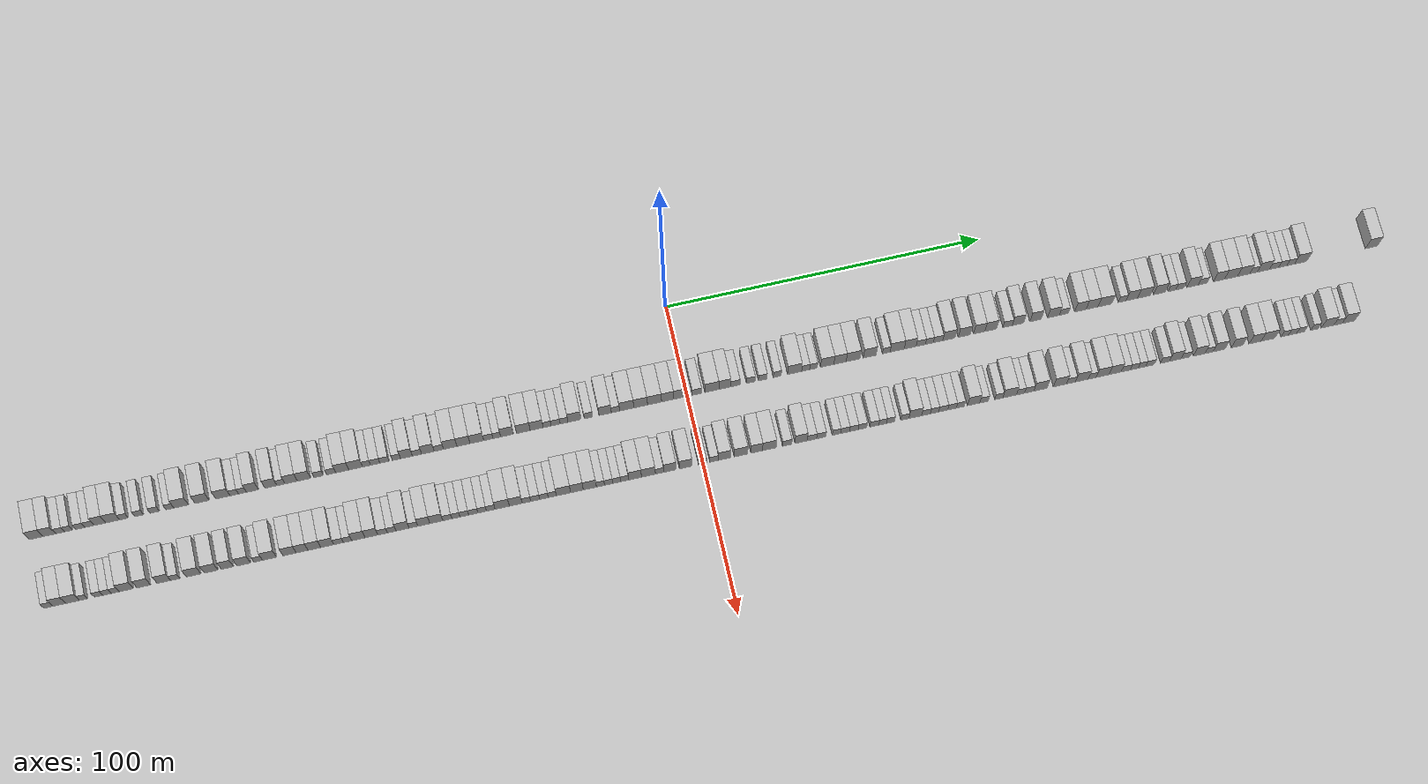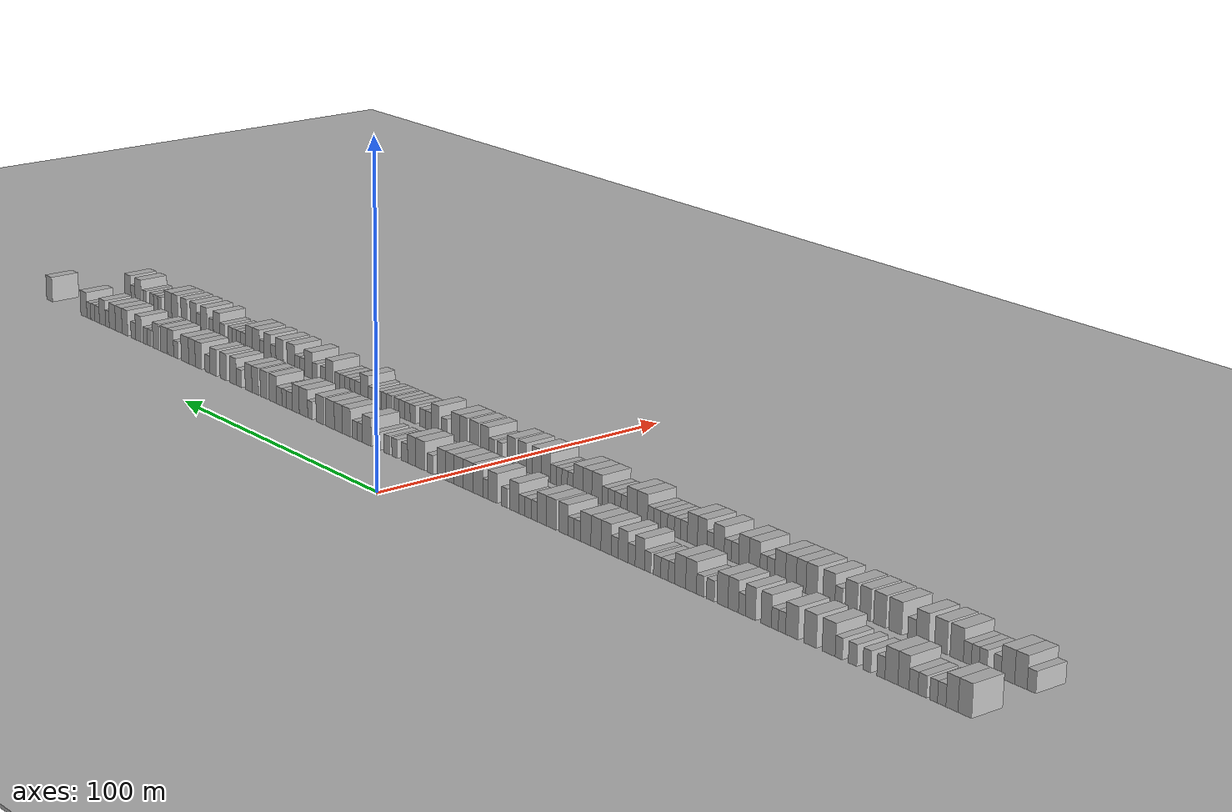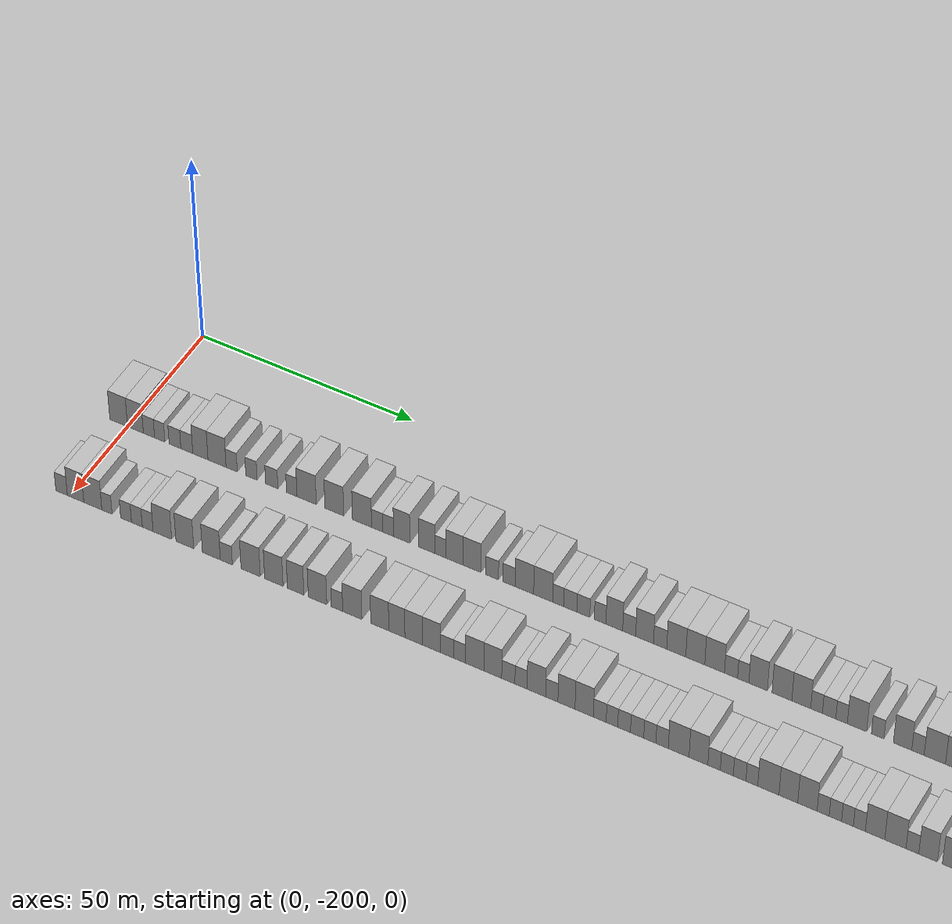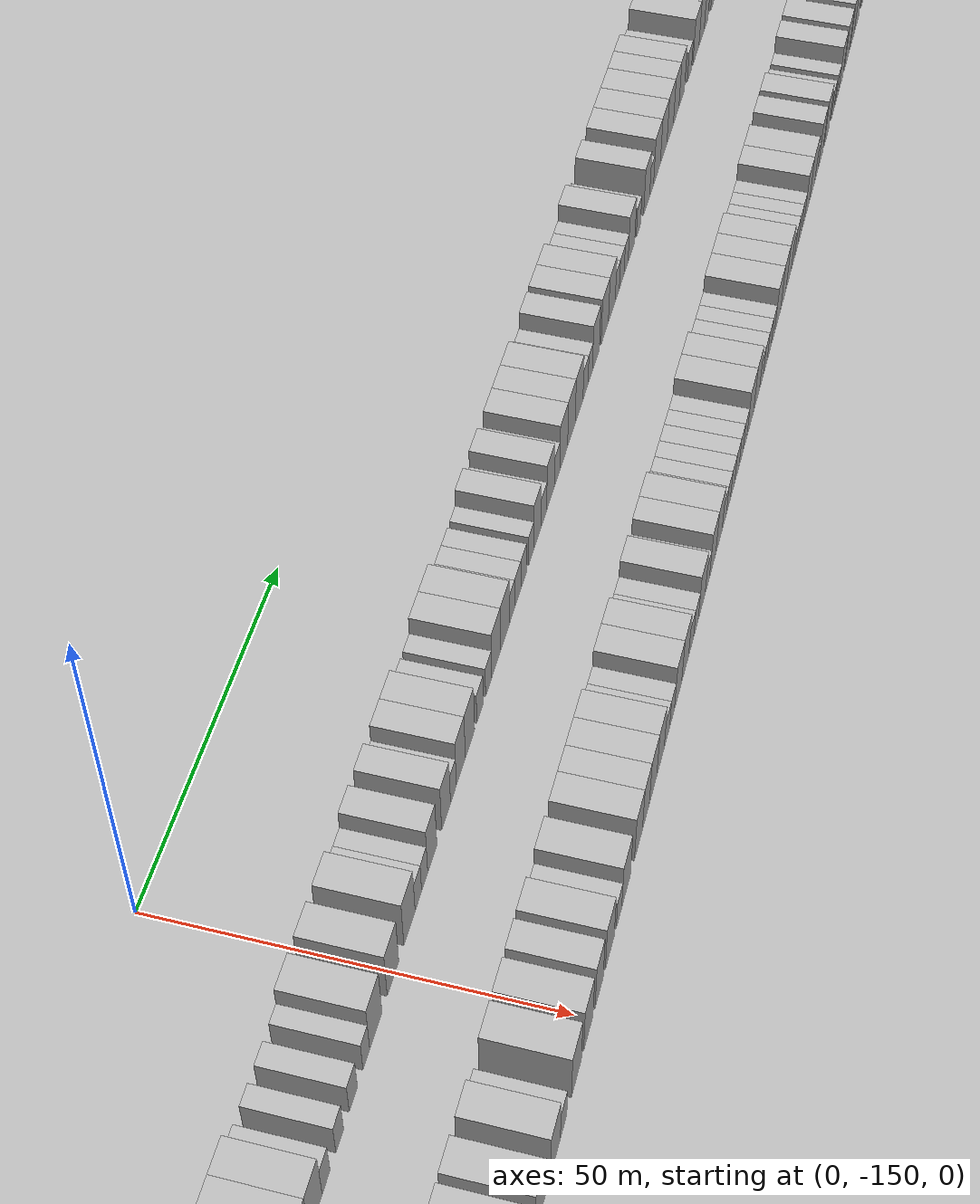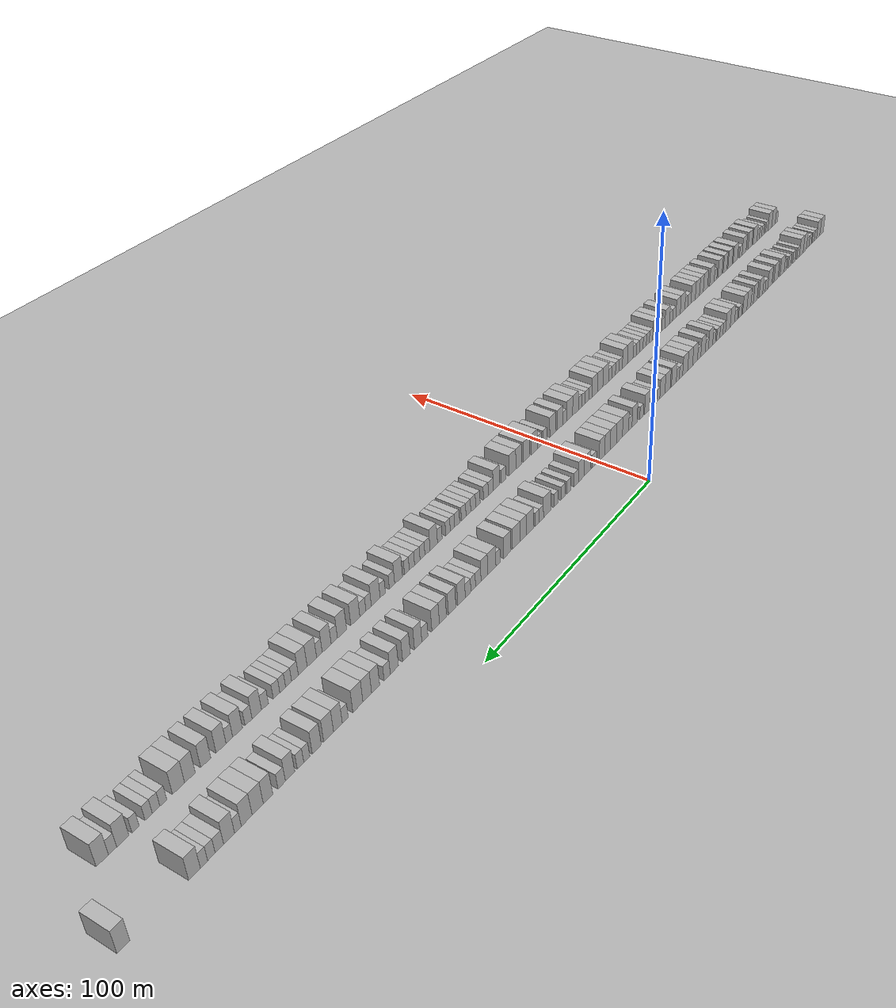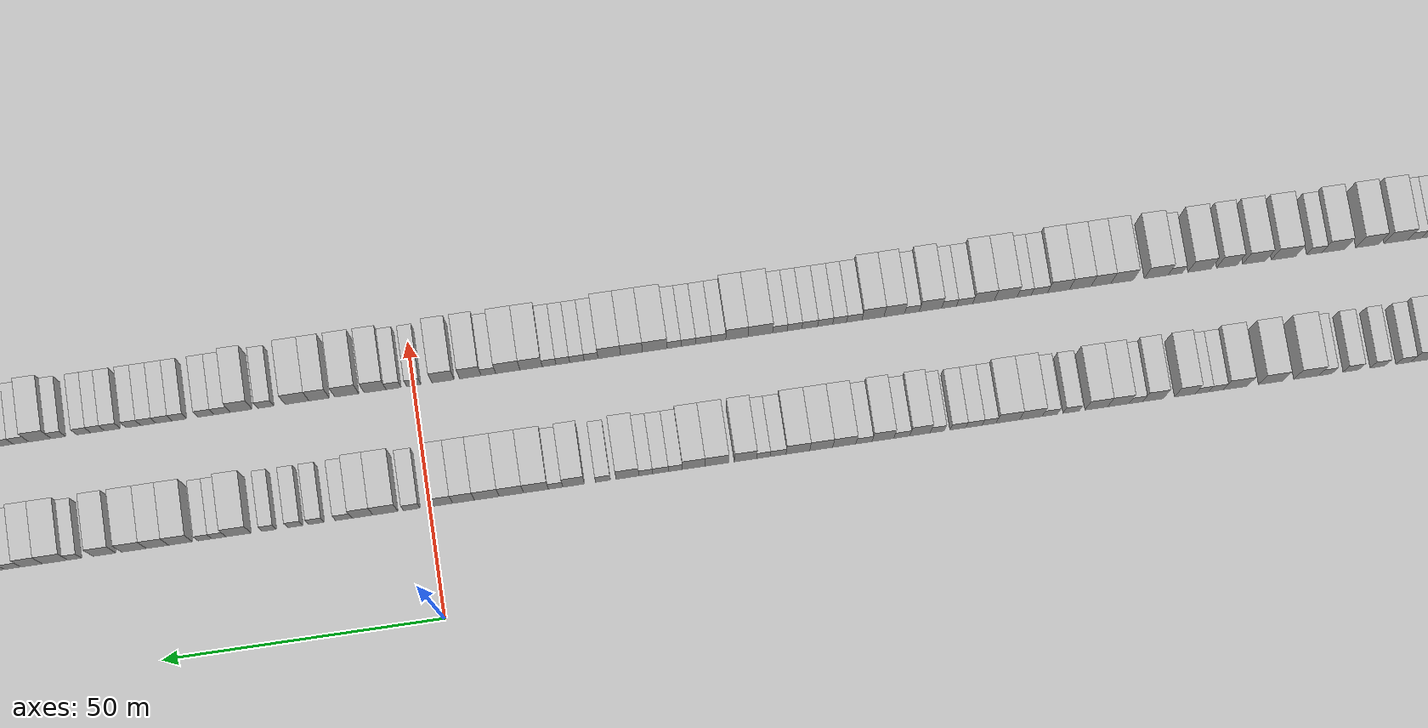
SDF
<?xml version="1.0" encoding="utf-8"?>

<sdf version="1.6">

   <world name="default">

      <gui fullscreen="0">

         <camera name="user_camera">

            <pose>-15 0 4.57585 0 0 0</pose>

            <view_controller>orbit</view_controller>

         </camera>

      </gui>

      <scene>

         <sky>

           <clouds>

             <speed>12</speed>

           </clouds>

         </sky>

         <ambient>0.4 0.4 0.4 1</ambient>

         <background>0.7 0.7 0.7 1</background>

         <shadows>1</shadows>

      </scene>

      <gravity>0 0 -9.8066</gravity>

      <magnetic_field>6e-06 2.3e-05 -4.2e-05</magnetic_field>

      <physics default="0" name="default_physics" type="ode">

         <ode>

            <solver>

               <type>quick</type>

               <iters>10</iters>

               <sor>1.0</sor>

               <use_dynamic_moi_rescaling>0</use_dynamic_moi_rescaling>

            </solver>

            <constraints>

               <cfm>0</cfm>

               <erp>0.2</erp>

               <contact_max_correcting_vel>100</contact_max_correcting_vel>

               <contact_surface_layer>0.001</contact_surface_layer>

            </constraints>

         </ode>

         <max_step_size>0.004</max_step_size>

         <real_time_factor>1</real_time_factor>

         <real_time_update_rate>250</real_time_update_rate>

      </physics>

      <light name="sun" type="directional">

         <cast_shadows>1</cast_shadows>

         <pose>0 0 10 0 0 0</pose>

         <diffuse>0.8 0.8 0.8 1</diffuse>

         <specular>0.2 0.2 0.2 1</specular>

         <attenuation>

            <range>1000</range>

            <constant>0.9</constant>

            <linear>0.01</linear>

            <quadratic>0.001</quadratic>

         </attenuation>

         <direction>-0.5 0.1 -0.9</direction>

      </light>

      <include>

         <name>ground_plane_1</name>

         <uri>model://HANNAS_ground_plane</uri>

         <pose>0 0 0  0 0 0</pose>

      </include>

      <include>

         <name>ground_plane_2</name>

         <uri>model://HANNAS_ground_plane</uri>

         <pose>100 0 0  0 0 0</pose>

      </include>

      <model name="building_1">

         <static>1</static>

         <pose frame="">25.0000 -201.8715 0 0.000000 0.000000 0.000000</pose>

         <link name="link">

            <pose frame="">0 0 4.50 0 0 0</pose>

            <collision name="collision">

               <geometry>

                  <box>

                     <size>10.0000 4.2571 9.0000</size>

                  </box>

               </geometry>

               <max_contacts>10</max_contacts>

               <surface>

                  <contact>

                     <ode/>

                  </contact>

                  <bounce/>

                  <friction>

                     <torsional>

                        <ode/>

                     </torsional>

                     <ode/>

                  </friction>

               </surface>

            </collision>

            <visual name="visual">

               <cast_shadows>0</cast_shadows>

               <geometry>

                  <box>

                     <size>10.0000 4.2571 9.0000</size>

                  </box>

               </geometry>

               <material>

                  <script>

                     <uri>model://HANNAS_wall/materials/scripts</uri>

                     <uri>model://HANNAS_wall/materials/textures</uri>

                     <name>vrc/HANNAS_wall</name>

                  </script>

               </material>

            </visual>

            <self_collide>0</self_collide>

            <enable_wind>0</enable_wind>

            <kinematic>0</kinematic>

         </link>

      </model>

      <model name="building_2">

         <static>1</static>

         <pose frame="">25.0000 -197.8458 0 0.000000 0.000000 0.000000</pose>

         <link name="link">

            <pose frame="">0 0 4.50 0 0 0</pose>

            <collision name="collision">

               <geometry>

                  <box>

                     <size>10.0000 3.7942 9.0000</size>

                  </box>

               </geometry>

               <max_contacts>10</max_contacts>

               <surface>

                  <contact>

                     <ode/>

                  </contact>

                  <bounce/>

                  <friction>

                     <torsional>

                        <ode/>

                     </torsional>

                     <ode/>

                  </friction>

               </surface>

            </collision>

            <visual name="visual">

               <cast_shadows>0</cast_shadows>

               <geometry>

                  <box>

                     <size>10.0000 3.7942 9.0000</size>

                  </box>

               </geometry>

               <material>

                  <script>

                     <uri>model://HANNAS_wall/materials/scripts</uri>

                     <uri>model://HANNAS_wall/materials/textures</uri>

                     <name>vrc/HANNAS_wall</name>

                  </script>

               </material>

            </visual>

            <self_collide>0</self_collide>

            <enable_wind>0</enable_wind>

            <kinematic>0</kinematic>

         </link>

      </model>

      <model name="building_3">

         <static>1</static>

         <pose frame="">25.0000 -194.6153 0 0.000000 0.000000 0.000000</pose>

         <link name="link">

            <pose frame="">0 0 3.00 0 0 0</pose>

            <collision name="collision">

               <geometry>

                  <box>

                     <size>10.0000 2.6668 6.0000</size>

                  </box>

               </geometry>

               <max_contacts>10</max_contacts>

               <surface>

                  <contact>

                     <ode/>

                  </contact>

                  <bounce/>

                  <friction>

                     <torsional>

                        <ode/>

                     </torsional>

                     <ode/>

                  </friction>

               </surface>

            </collision>

            <visual name="visual">

               <cast_shadows>0</cast_shadows>

               <geometry>

                  <box>

                     <size>10.0000 2.6668 6.0000</size>

                  </box>

               </geometry>

               <material>

                  <script>

                     <uri>model://HANNAS_wall/materials/scripts</uri>

                     <uri>model://HANNAS_wall/materials/textures</uri>

                     <name>vrc/HANNAS_wall</name>

                  </script>

               </material>

            </visual>

            <self_collide>0</self_collide>

            <enable_wind>0</enable_wind>

            <kinematic>0</kinematic>

         </link>

      </model>

      <model name="building_4">

         <static>1</static>

         <pose frame="">25.0000 -192.0383 0 0.000000 0.000000 0.000000</pose>

         <link name="link">

            <pose frame="">0 0 3.00 0 0 0</pose>

            <collision name="collision">

               <geometry>

                  <box>

                     <size>10.0000 2.4872 6.0000</size>

                  </box>

               </geometry>

               <max_contacts>10</max_contacts>

               <surface>

                  <contact>

                     <ode/>

                  </contact>

                  <bounce/>

                  <friction>

                     <torsional>

                        <ode/>

                     </torsional>

                     <ode/>

                  </friction>

               </surface>

            </collision>

            <visual name="visual">

               <cast_shadows>0</cast_shadows>

               <geometry>

                  <box>

                     <size>10.0000 2.4872 6.0000</size>

                  </box>

               </geometry>

               <material>

                  <script>

                     <uri>model://HANNAS_wall/materials/scripts</uri>

                     <uri>model://HANNAS_wall/materials/textures</uri>

                     <name>vrc/HANNAS_wall</name>

                  </script>

               </material>

            </visual>

            <self_collide>0</self_collide>

            <enable_wind>0</enable_wind>

            <kinematic>0</kinematic>

         </link>

      </model>

      <model name="building_5">

         <static>1</static>

         <pose frame="">25.0000 -188.4017 0 0.000000 0.000000 0.000000</pose>

         <link name="link">

            <pose frame="">0 0 3.00 0 0 0</pose>

            <collision name="collision">

               <geometry>

                  <box>

                     <size>10.0000 2.7860 6.0000</size>

                  </box>

               </geometry>

               <max_contacts>10</max_contacts>

               <surface>

                  <contact>

                     <ode/>

                  </contact>

                  <bounce/>

                  <friction>

                     <torsional>

                        <ode/>

                     </torsional>

                     <ode/>

                  </friction>

               </surface>

            </collision>

            <visual name="visual">

               <cast_shadows>0</cast_shadows>

               <geometry>

                  <box>

                     <size>10.0000 2.7860 6.0000</size>

                  </box>

               </geometry>

               <material>

                  <script>

                     <uri>model://HANNAS_wall/materials/scripts</uri>

                     <uri>model://HANNAS_wall/materials/textures</uri>

                     <name>vrc/HANNAS_wall</name>

                  </script>

               </material>

            </visual>

            <self_collide>0</self_collide>

            <enable_wind>0</enable_wind>

            <kinematic>0</kinematic>

         </link>

      </model>

      <model name="building_6">

         <static>1</static>

         <pose frame="">25.0000 -185.5879 0 0.000000 0.000000 0.000000</pose>

         <link name="link">

            <pose frame="">0 0 3.00 0 0 0</pose>

            <collision name="collision">

               <geometry>

                  <box>

                     <size>10.0000 2.8416 6.0000</size>

                  </box>

               </geometry>

               <max_contacts>10</max_contacts>

               <surface>

                  <contact>

                     <ode/>

                  </contact>

                  <bounce/>

                  <friction>

                     <torsional>

                        <ode/>

                     </torsional>

                     <ode/>

                  </friction>

               </surface>

            </collision>

            <visual name="visual">

               <cast_shadows>0</cast_shadows>

               <geometry>

                  <box>

                     <size>10.0000 2.8416 6.0000</size>

                  </box>

               </geometry>

               <material>

                  <script>

                     <uri>model://HANNAS_wall/materials/scripts</uri>

                     <uri>model://HANNAS_wall/materials/textures</uri>

                     <name>vrc/HANNAS_wall</name>

                  </script>

               </material>

            </visual>

            <self_collide>0</self_collide>

            <enable_wind>0</enable_wind>

            <kinematic>0</kinematic>

         </link>

      </model>

      <model name="building_7">

         <static>1</static>

         <pose frame="">25.0000 -182.3640 0 0.000000 0.000000 0.000000</pose>

         <link name="link">

            <pose frame="">0 0 4.50 0 0 0</pose>

            <collision name="collision">

               <geometry>

                  <box>

                     <size>10.0000 3.6061 9.0000</size>

                  </box>

               </geometry>

               <max_contacts>10</max_contacts>

               <surface>

                  <contact>

                     <ode/>

                  </contact>

                  <bounce/>

                  <friction>

                     <torsional>

                        <ode/>

                     </torsional>

                     <ode/>

                  </friction>

               </surface>

            </collision>

            <visual name="visual">

               <cast_shadows>0</cast_shadows>

               <geometry>

                  <box>

                     <size>10.0000 3.6061 9.0000</size>

                  </box>

               </geometry>

               <material>

                  <script>

                     <uri>model://HANNAS_wall/materials/scripts</uri>

                     <uri>model://HANNAS_wall/materials/textures</uri>

                     <name>vrc/HANNAS_wall</name>

                  </script>

               </material>

            </visual>

            <self_collide>0</self_collide>

            <enable_wind>0</enable_wind>

            <kinematic>0</kinematic>

         </link>

      </model>

      <model name="building_8">

         <static>1</static>

         <pose frame="">25.0000 -178.4295 0 0.000000 0.000000 0.000000</pose>

         <link name="link">

            <pose frame="">0 0 4.50 0 0 0</pose>

            <collision name="collision">

               <geometry>

                  <box>

                     <size>10.0000 4.2630 9.0000</size>

                  </box>

               </geometry>

               <max_contacts>10</max_contacts>

               <surface>

                  <contact>

                     <ode/>

                  </contact>

                  <bounce/>

                  <friction>

                     <torsional>

                        <ode/>

                     </torsional>

                     <ode/>

                  </friction>

               </surface>

            </collision>

            <visual name="visual">

               <cast_shadows>0</cast_shadows>

               <geometry>

                  <box>

                     <size>10.0000 4.2630 9.0000</size>

                  </box>

               </geometry>

               <material>

                  <script>

                     <uri>model://HANNAS_wall/materials/scripts</uri>

                     <uri>model://HANNAS_wall/materials/textures</uri>

                     <name>vrc/HANNAS_wall</name>

                  </script>

               </material>

            </visual>

            <self_collide>0</self_collide>

            <enable_wind>0</enable_wind>

            <kinematic>0</kinematic>

         </link>

      </model>

      <model name="building_9">

         <static>1</static>

         <pose frame="">25.0000 -174.9708 0 0.000000 0.000000 0.000000</pose>

         <link name="link">

            <pose frame="">0 0 3.00 0 0 0</pose>

            <collision name="collision">

               <geometry>

                  <box>

                     <size>10.0000 2.6544 6.0000</size>

                  </box>

               </geometry>

               <max_contacts>10</max_contacts>

               <surface>

                  <contact>

                     <ode/>

                  </contact>

                  <bounce/>

                  <friction>

                     <torsional>

                        <ode/>

                     </torsional>

                     <ode/>

                  </friction>

               </surface>

            </collision>

            <visual name="visual">

               <cast_shadows>0</cast_shadows>

               <geometry>

                  <box>

                     <size>10.0000 2.6544 6.0000</size>

                  </box>

               </geometry>

               <material>

                  <script>

                     <uri>model://HANNAS_wall/materials/scripts</uri>

                     <uri>model://HANNAS_wall/materials/textures</uri>

                     <name>vrc/HANNAS_wall</name>

                  </script>

               </material>

            </visual>

            <self_collide>0</self_collide>

            <enable_wind>0</enable_wind>

            <kinematic>0</kinematic>

         </link>

      </model>

      <model name="building_10">

         <static>1</static>

         <pose frame="">25.0000 -170.3099 0 0.000000 0.000000 0.000000</pose>

         <link name="link">

            <pose frame="">0 0 3.00 0 0 0</pose>

            <collision name="collision">

               <geometry>

                  <box>

                     <size>10.0000 2.6674 6.0000</size>

                  </box>

               </geometry>

               <max_contacts>10</max_contacts>

               <surface>

                  <contact>

                     <ode/>

                  </contact>

                  <bounce/>

                  <friction>

                     <torsional>

                        <ode/>

                     </torsional>

                     <ode/>

                  </friction>

               </surface>

            </collision>

            <visual name="visual">

               <cast_shadows>0</cast_shadows>

               <geometry>

                  <box>

                     <size>10.0000 2.6674 6.0000</size>

                  </box>

               </geometry>

               <material>

                  <script>

                     <uri>model://HANNAS_wall/materials/scripts</uri>

                     <uri>model://HANNAS_wall/materials/textures</uri>

                     <name>vrc/HANNAS_wall</name>

                  </script>

               </material>

            </visual>

            <self_collide>0</self_collide>

            <enable_wind>0</enable_wind>

            <kinematic>0</kinematic>

         </link>

      </model>

      <model name="building_11">

         <static>1</static>

         <pose frame="">25.0000 -165.5331 0 0.000000 0.000000 0.000000</pose>

         <link name="link">

            <pose frame="">0 0 3.00 0 0 0</pose>

            <collision name="collision">

               <geometry>

                  <box>

                     <size>10.0000 2.8862 6.0000</size>

                  </box>

               </geometry>

               <max_contacts>10</max_contacts>

               <surface>

                  <contact>

                     <ode/>

                  </contact>

                  <bounce/>

                  <friction>

                     <torsional>

                        <ode/>

                     </torsional>

                     <ode/>

                  </friction>

               </surface>

            </collision>

            <visual name="visual">

               <cast_shadows>0</cast_shadows>

               <geometry>

                  <box>

                     <size>10.0000 2.8862 6.0000</size>

                  </box>

               </geometry>

               <material>

                  <script>

                     <uri>model://HANNAS_wall/materials/scripts</uri>

                     <uri>model://HANNAS_wall/materials/textures</uri>

                     <name>vrc/HANNAS_wall</name>

                  </script>

               </material>

            </visual>

            <self_collide>0</self_collide>

            <enable_wind>0</enable_wind>

            <kinematic>0</kinematic>

         </link>

      </model>

      <model name="building_12">

         <static>1</static>

         <pose frame="">25.0000 -160.8686 0 0.000000 0.000000 0.000000</pose>

         <link name="link">

            <pose frame="">0 0 3.00 0 0 0</pose>

            <collision name="collision">

               <geometry>

                  <box>

                     <size>10.0000 2.4428 6.0000</size>

                  </box>

               </geometry>

               <max_contacts>10</max_contacts>

               <surface>

                  <contact>

                     <ode/>

                  </contact>

                  <bounce/>

                  <friction>

                     <torsional>

                        <ode/>

                     </torsional>

                     <ode/>

                  </friction>

               </surface>

            </collision>

            <visual name="visual">

               <cast_shadows>0</cast_shadows>

               <geometry>

                  <box>

                     <size>10.0000 2.4428 6.0000</size>

                  </box>

               </geometry>

               <material>

                  <script>

                     <uri>model://HANNAS_wall/materials/scripts</uri>

                     <uri>model://HANNAS_wall/materials/textures</uri>

                     <name>vrc/HANNAS_wall</name>

                  </script>

               </material>

            </visual>

            <self_collide>0</self_collide>

            <enable_wind>0</enable_wind>

            <kinematic>0</kinematic>

         </link>

      </model>

      <model name="building_13">

         <static>1</static>

         <pose frame="">25.0000 -157.4011 0 0.000000 0.000000 0.000000</pose>

         <link name="link">

            <pose frame="">0 0 4.50 0 0 0</pose>

            <collision name="collision">

               <geometry>

                  <box>

                     <size>10.0000 4.4920 9.0000</size>

                  </box>

               </geometry>

               <max_contacts>10</max_contacts>

               <surface>

                  <contact>

                     <ode/>

                  </contact>

                  <bounce/>

                  <friction>

                     <torsional>

                        <ode/>

                     </torsional>

                     <ode/>

                  </friction>

               </surface>

            </collision>

            <visual name="visual">

               <cast_shadows>0</cast_shadows>

               <geometry>

                  <box>

                     <size>10.0000 4.4920 9.0000</size>

                  </box>

               </geometry>

               <material>

                  <script>

                     <uri>model://HANNAS_wall/materials/scripts</uri>

                     <uri>model://HANNAS_wall/materials/textures</uri>

                     <name>vrc/HANNAS_wall</name>

                  </script>

               </material>

            </visual>

            <self_collide>0</self_collide>

            <enable_wind>0</enable_wind>

            <kinematic>0</kinematic>

         </link>

      </model>

      <model name="building_14">

         <static>1</static>

         <pose frame="">25.0000 -150.9676 0 0.000000 0.000000 0.000000</pose>

         <link name="link">

            <pose frame="">0 0 4.50 0 0 0</pose>

            <collision name="collision">

               <geometry>

                  <box>

                     <size>10.0000 4.3750 9.0000</size>

                  </box>

               </geometry>

               <max_contacts>10</max_contacts>

               <surface>

                  <contact>

                     <ode/>

                  </contact>

                  <bounce/>

                  <friction>

                     <torsional>

                        <ode/>

                     </torsional>

                     <ode/>

                  </friction>

               </surface>

            </collision>

            <visual name="visual">

               <cast_shadows>0</cast_shadows>

               <geometry>

                  <box>

                     <size>10.0000 4.3750 9.0000</size>

                  </box>

               </geometry>

               <material>

                  <script>

                     <uri>model://HANNAS_wall/materials/scripts</uri>

                     <uri>model://HANNAS_wall/materials/textures</uri>

                     <name>vrc/HANNAS_wall</name>

                  </script>

               </material>

            </visual>

            <self_collide>0</self_collide>

            <enable_wind>0</enable_wind>

            <kinematic>0</kinematic>

         </link>

      </model>

      <model name="building_15">

         <static>1</static>

         <pose frame="">25.0000 -144.5749 0 0.000000 0.000000 0.000000</pose>

         <link name="link">

            <pose frame="">0 0 4.50 0 0 0</pose>

            <collision name="collision">

               <geometry>

                  <box>

                     <size>10.0000 4.4104 9.0000</size>

                  </box>

               </geometry>

               <max_contacts>10</max_contacts>

               <surface>

                  <contact>

                     <ode/>

                  </contact>

                  <bounce/>

                  <friction>

                     <torsional>

                        <ode/>

                     </torsional>

                     <ode/>

                  </friction>

               </surface>

            </collision>

            <visual name="visual">

               <cast_shadows>0</cast_shadows>

               <geometry>

                  <box>

                     <size>10.0000 4.4104 9.0000</size>

                  </box>

               </geometry>

               <material>

                  <script>

                     <uri>model://HANNAS_wall/materials/scripts</uri>

                     <uri>model://HANNAS_wall/materials/textures</uri>

                     <name>vrc/HANNAS_wall</name>

                  </script>

               </material>

            </visual>

            <self_collide>0</self_collide>

            <enable_wind>0</enable_wind>

            <kinematic>0</kinematic>

         </link>

      </model>

      <model name="building_16">

         <static>1</static>

         <pose frame="">25.0000 -141.0750 0 0.000000 0.000000 0.000000</pose>

         <link name="link">

            <pose frame="">0 0 3.00 0 0 0</pose>

            <collision name="collision">

               <geometry>

                  <box>

                     <size>10.0000 2.5892 6.0000</size>

                  </box>

               </geometry>

               <max_contacts>10</max_contacts>

               <surface>

                  <contact>

                     <ode/>

                  </contact>

                  <bounce/>

                  <friction>

                     <torsional>

                        <ode/>

                     </torsional>

                     <ode/>

                  </friction>

               </surface>

            </collision>

            <visual name="visual">

               <cast_shadows>0</cast_shadows>

               <geometry>

                  <box>

                     <size>10.0000 2.5892 6.0000</size>

                  </box>

               </geometry>

               <material>

                  <script>

                     <uri>model://HANNAS_wall/materials/scripts</uri>

                     <uri>model://HANNAS_wall/materials/textures</uri>

                     <name>vrc/HANNAS_wall</name>

                  </script>

               </material>

            </visual>

            <self_collide>0</self_collide>

            <enable_wind>0</enable_wind>

            <kinematic>0</kinematic>

         </link>

      </model>

      <model name="building_17">

         <static>1</static>

         <pose frame="">25.0000 -138.5520 0 0.000000 0.000000 0.000000</pose>

         <link name="link">

            <pose frame="">0 0 3.00 0 0 0</pose>

            <collision name="collision">

               <geometry>

                  <box>

                     <size>10.0000 2.4569 6.0000</size>

                  </box>

               </geometry>

               <max_contacts>10</max_contacts>

               <surface>

                  <contact>

                     <ode/>

                  </contact>

                  <bounce/>

                  <friction>

                     <torsional>

                        <ode/>

                     </torsional>

                     <ode/>

                  </friction>

               </surface>

            </collision>

            <visual name="visual">

               <cast_shadows>0</cast_shadows>

               <geometry>

                  <box>

                     <size>10.0000 2.4569 6.0000</size>

                  </box>

               </geometry>

               <material>

                  <script>

                     <uri>model://HANNAS_wall/materials/scripts</uri>

                     <uri>model://HANNAS_wall/materials/textures</uri>

                     <name>vrc/HANNAS_wall</name>

                  </script>

               </material>

            </visual>

            <self_collide>0</self_collide>

            <enable_wind>0</enable_wind>

            <kinematic>0</kinematic>

         </link>

      </model>

      <model name="building_18">

         <static>1</static>

         <pose frame="">25.0000 -135.4540 0 0.000000 0.000000 0.000000</pose>

         <link name="link">

            <pose frame="">0 0 4.50 0 0 0</pose>

            <collision name="collision">

               <geometry>

                  <box>

                     <size>10.0000 3.7391 9.0000</size>

                  </box>

               </geometry>

               <max_contacts>10</max_contacts>

               <surface>

                  <contact>

                     <ode/>

                  </contact>

                  <bounce/>

                  <friction>

                     <torsional>

                        <ode/>

                     </torsional>

                     <ode/>

                  </friction>

               </surface>

            </collision>

            <visual name="visual">

               <cast_shadows>0</cast_shadows>

               <geometry>

                  <box>

                     <size>10.0000 3.7391 9.0000</size>

                  </box>

               </geometry>

               <material>

                  <script>

                     <uri>model://HANNAS_wall/materials/scripts</uri>

                     <uri>model://HANNAS_wall/materials/textures</uri>

                     <name>vrc/HANNAS_wall</name>

                  </script>

               </material>

            </visual>

            <self_collide>0</self_collide>

            <enable_wind>0</enable_wind>

            <kinematic>0</kinematic>

         </link>

      </model>

      <model name="building_19">

         <static>1</static>

         <pose frame="">25.0000 -129.7280 0 0.000000 0.000000 0.000000</pose>

         <link name="link">

            <pose frame="">0 0 4.50 0 0 0</pose>

            <collision name="collision">

               <geometry>

                  <box>

                     <size>10.0000 3.7128 9.0000</size>

                  </box>

               </geometry>

               <max_contacts>10</max_contacts>

               <surface>

                  <contact>

                     <ode/>

                  </contact>

                  <bounce/>

                  <friction>

                     <torsional>

                        <ode/>

                     </torsional>

                     <ode/>

                  </friction>

               </surface>

            </collision>

            <visual name="visual">

               <cast_shadows>0</cast_shadows>

               <geometry>

                  <box>

                     <size>10.0000 3.7128 9.0000</size>

                  </box>

               </geometry>

               <material>

                  <script>

                     <uri>model://HANNAS_wall/materials/scripts</uri>

                     <uri>model://HANNAS_wall/materials/textures</uri>

                     <name>vrc/HANNAS_wall</name>

                  </script>

               </material>

            </visual>

            <self_collide>0</self_collide>

            <enable_wind>0</enable_wind>

            <kinematic>0</kinematic>

         </link>

      </model>

      <model name="building_20">

         <static>1</static>

         <pose frame="">25.0000 -126.6309 0 0.000000 0.000000 0.000000</pose>

         <link name="link">

            <pose frame="">0 0 3.00 0 0 0</pose>

            <collision name="collision">

               <geometry>

                  <box>

                     <size>10.0000 2.4814 6.0000</size>

                  </box>

               </geometry>

               <max_contacts>10</max_contacts>

               <surface>

                  <contact>

                     <ode/>

                  </contact>

                  <bounce/>

                  <friction>

                     <torsional>

                        <ode/>

                     </torsional>

                     <ode/>

                  </friction>

               </surface>

            </collision>

            <visual name="visual">

               <cast_shadows>0</cast_shadows>

               <geometry>

                  <box>

                     <size>10.0000 2.4814 6.0000</size>

                  </box>

               </geometry>

               <material>

                  <script>

                     <uri>model://HANNAS_wall/materials/scripts</uri>

                     <uri>model://HANNAS_wall/materials/textures</uri>

                     <name>vrc/HANNAS_wall</name>

                  </script>

               </material>

            </visual>

            <self_collide>0</self_collide>

            <enable_wind>0</enable_wind>

            <kinematic>0</kinematic>

         </link>

      </model>

      <model name="building_21">

         <static>1</static>

         <pose frame="">25.0000 -123.4586 0 0.000000 0.000000 0.000000</pose>

         <link name="link">

            <pose frame="">0 0 4.50 0 0 0</pose>

            <collision name="collision">

               <geometry>

                  <box>

                     <size>10.0000 3.8633 9.0000</size>

                  </box>

               </geometry>

               <max_contacts>10</max_contacts>

               <surface>

                  <contact>

                     <ode/>

                  </contact>

                  <bounce/>

                  <friction>

                     <torsional>

                        <ode/>

                     </torsional>

                     <ode/>

                  </friction>

               </surface>

            </collision>

            <visual name="visual">

               <cast_shadows>0</cast_shadows>

               <geometry>

                  <box>

                     <size>10.0000 3.8633 9.0000</size>

                  </box>

               </geometry>

               <material>

                  <script>

                     <uri>model://HANNAS_wall/materials/scripts</uri>

                     <uri>model://HANNAS_wall/materials/textures</uri>

                     <name>vrc/HANNAS_wall</name>

                  </script>

               </material>

            </visual>

            <self_collide>0</self_collide>

            <enable_wind>0</enable_wind>

            <kinematic>0</kinematic>

         </link>

      </model>

      <model name="building_22">

         <static>1</static>

         <pose frame="">25.0000 -119.4799 0 0.000000 0.000000 0.000000</pose>

         <link name="link">

            <pose frame="">0 0 4.50 0 0 0</pose>

            <collision name="collision">

               <geometry>

                  <box>

                     <size>10.0000 4.0941 9.0000</size>

                  </box>

               </geometry>

               <max_contacts>10</max_contacts>

               <surface>

                  <contact>

                     <ode/>

                  </contact>

                  <bounce/>

                  <friction>

                     <torsional>

                        <ode/>

                     </torsional>

                     <ode/>

                  </friction>

               </surface>

            </collision>

            <visual name="visual">

               <cast_shadows>0</cast_shadows>

               <geometry>

                  <box>

                     <size>10.0000 4.0941 9.0000</size>

                  </box>

               </geometry>

               <material>

                  <script>

                     <uri>model://HANNAS_wall/materials/scripts</uri>

                     <uri>model://HANNAS_wall/materials/textures</uri>

                     <name>vrc/HANNAS_wall</name>

                  </script>

               </material>

            </visual>

            <self_collide>0</self_collide>

            <enable_wind>0</enable_wind>

            <kinematic>0</kinematic>

         </link>

      </model>

      <model name="building_23">

         <static>1</static>

         <pose frame="">25.0000 -114.9615 0 0.000000 0.000000 0.000000</pose>

         <link name="link">

            <pose frame="">0 0 3.00 0 0 0</pose>

            <collision name="collision">

               <geometry>

                  <box>

                     <size>10.0000 2.9427 6.0000</size>

                  </box>

               </geometry>

               <max_contacts>10</max_contacts>

               <surface>

                  <contact>

                     <ode/>

                  </contact>

                  <bounce/>

                  <friction>

                     <torsional>

                        <ode/>

                     </torsional>

                     <ode/>

                  </friction>

               </surface>

            </collision>

            <visual name="visual">

               <cast_shadows>0</cast_shadows>

               <geometry>

                  <box>

                     <size>10.0000 2.9427 6.0000</size>

                  </box>

               </geometry>

               <material>

                  <script>

                     <uri>model://HANNAS_wall/materials/scripts</uri>

                     <uri>model://HANNAS_wall/materials/textures</uri>

                     <name>vrc/HANNAS_wall</name>

                  </script>

               </material>

            </visual>

            <self_collide>0</self_collide>

            <enable_wind>0</enable_wind>

            <kinematic>0</kinematic>

         </link>

      </model>

      <model name="building_24">

         <static>1</static>

         <pose frame="">25.0000 -111.1020 0 0.000000 0.000000 0.000000</pose>

         <link name="link">

            <pose frame="">0 0 3.00 0 0 0</pose>

            <collision name="collision">

               <geometry>

                  <box>

                     <size>10.0000 2.7763 6.0000</size>

                  </box>

               </geometry>

               <max_contacts>10</max_contacts>

               <surface>

                  <contact>

                     <ode/>

                  </contact>

                  <bounce/>

                  <friction>

                     <torsional>

                        <ode/>

                     </torsional>

                     <ode/>

                  </friction>

               </surface>

            </collision>

            <visual name="visual">

               <cast_shadows>0</cast_shadows>

               <geometry>

                  <box>

                     <size>10.0000 2.7763 6.0000</size>

                  </box>

               </geometry>

               <material>

                  <script>

                     <uri>model://HANNAS_wall/materials/scripts</uri>

                     <uri>model://HANNAS_wall/materials/textures</uri>

                     <name>vrc/HANNAS_wall</name>

                  </script>

               </material>

            </visual>

            <self_collide>0</self_collide>

            <enable_wind>0</enable_wind>

            <kinematic>0</kinematic>

         </link>

      </model>

      <model name="building_25">

         <static>1</static>

         <pose frame="">25.0000 -107.6616 0 0.000000 0.000000 0.000000</pose>

         <link name="link">

            <pose frame="">0 0 4.50 0 0 0</pose>

            <collision name="collision">

               <geometry>

                  <box>

                     <size>10.0000 4.1044 9.0000</size>

                  </box>

               </geometry>

               <max_contacts>10</max_contacts>

               <surface>

                  <contact>

                     <ode/>

                  </contact>

                  <bounce/>

                  <friction>

                     <torsional>

                        <ode/>

                     </torsional>

                     <ode/>

                  </friction>

               </surface>

            </collision>

            <visual name="visual">

               <cast_shadows>0</cast_shadows>

               <geometry>

                  <box>

                     <size>10.0000 4.1044 9.0000</size>

                  </box>

               </geometry>

               <material>

                  <script>

                     <uri>model://HANNAS_wall/materials/scripts</uri>

                     <uri>model://HANNAS_wall/materials/textures</uri>

                     <name>vrc/HANNAS_wall</name>

                  </script>

               </material>

            </visual>

            <self_collide>0</self_collide>

            <enable_wind>0</enable_wind>

            <kinematic>0</kinematic>

         </link>

      </model>

      <model name="building_26">

         <static>1</static>

         <pose frame="">25.0000 -103.4904 0 0.000000 0.000000 0.000000</pose>

         <link name="link">

            <pose frame="">0 0 4.50 0 0 0</pose>

            <collision name="collision">

               <geometry>

                  <box>

                     <size>10.0000 4.2381 9.0000</size>

                  </box>

               </geometry>

               <max_contacts>10</max_contacts>

               <surface>

                  <contact>

                     <ode/>

                  </contact>

                  <bounce/>

                  <friction>

                     <torsional>

                        <ode/>

                     </torsional>

                     <ode/>

                  </friction>

               </surface>

            </collision>

            <visual name="visual">

               <cast_shadows>0</cast_shadows>

               <geometry>

                  <box>

                     <size>10.0000 4.2381 9.0000</size>

                  </box>

               </geometry>

               <material>

                  <script>

                     <uri>model://HANNAS_wall/materials/scripts</uri>

                     <uri>model://HANNAS_wall/materials/textures</uri>

                     <name>vrc/HANNAS_wall</name>

                  </script>

               </material>

            </visual>

            <self_collide>0</self_collide>

            <enable_wind>0</enable_wind>

            <kinematic>0</kinematic>

         </link>

      </model>

      <model name="building_27">

         <static>1</static>

         <pose frame="">25.0000 -100.1394 0 0.000000 0.000000 0.000000</pose>

         <link name="link">

            <pose frame="">0 0 3.00 0 0 0</pose>

            <collision name="collision">

               <geometry>

                  <box>

                     <size>10.0000 2.4638 6.0000</size>

                  </box>

               </geometry>

               <max_contacts>10</max_contacts>

               <surface>

                  <contact>

                     <ode/>

                  </contact>

                  <bounce/>

                  <friction>

                     <torsional>

                        <ode/>

                     </torsional>

                     <ode/>

                  </friction>

               </surface>

            </collision>

            <visual name="visual">

               <cast_shadows>0</cast_shadows>

               <geometry>

                  <box>

                     <size>10.0000 2.4638 6.0000</size>

                  </box>

               </geometry>

               <material>

                  <script>

                     <uri>model://HANNAS_wall/materials/scripts</uri>

                     <uri>model://HANNAS_wall/materials/textures</uri>

                     <name>vrc/HANNAS_wall</name>

                  </script>

               </material>

            </visual>

            <self_collide>0</self_collide>

            <enable_wind>0</enable_wind>

            <kinematic>0</kinematic>

         </link>

      </model>

      <model name="building_28">

         <static>1</static>

         <pose frame="">25.0000 -97.4309 0 0.000000 0.000000 0.000000</pose>

         <link name="link">

            <pose frame="">0 0 3.00 0 0 0</pose>

            <collision name="collision">

               <geometry>

                  <box>

                     <size>10.0000 2.9532 6.0000</size>

                  </box>

               </geometry>

               <max_contacts>10</max_contacts>

               <surface>

                  <contact>

                     <ode/>

                  </contact>

                  <bounce/>

                  <friction>

                     <torsional>

                        <ode/>

                     </torsional>

                     <ode/>

                  </friction>

               </surface>

            </collision>

            <visual name="visual">

               <cast_shadows>0</cast_shadows>

               <geometry>

                  <box>

                     <size>10.0000 2.9532 6.0000</size>

                  </box>

               </geometry>

               <material>

                  <script>

                     <uri>model://HANNAS_wall/materials/scripts</uri>

                     <uri>model://HANNAS_wall/materials/textures</uri>

                     <name>vrc/HANNAS_wall</name>

                  </script>

               </material>

            </visual>

            <self_collide>0</self_collide>

            <enable_wind>0</enable_wind>

            <kinematic>0</kinematic>

         </link>

      </model>

      <model name="building_29">

         <static>1</static>

         <pose frame="">25.0000 -94.5324 0 0.000000 0.000000 0.000000</pose>

         <link name="link">

            <pose frame="">0 0 3.00 0 0 0</pose>

            <collision name="collision">

               <geometry>

                  <box>

                     <size>10.0000 2.8439 6.0000</size>

                  </box>

               </geometry>

               <max_contacts>10</max_contacts>

               <surface>

                  <contact>

                     <ode/>

                  </contact>

                  <bounce/>

                  <friction>

                     <torsional>

                        <ode/>

                     </torsional>

                     <ode/>

                  </friction>

               </surface>

            </collision>

            <visual name="visual">

               <cast_shadows>0</cast_shadows>

               <geometry>

                  <box>

                     <size>10.0000 2.8439 6.0000</size>

                  </box>

               </geometry>

               <material>

                  <script>

                     <uri>model://HANNAS_wall/materials/scripts</uri>

                     <uri>model://HANNAS_wall/materials/textures</uri>

                     <name>vrc/HANNAS_wall</name>

                  </script>

               </material>

            </visual>

            <self_collide>0</self_collide>

            <enable_wind>0</enable_wind>

            <kinematic>0</kinematic>

         </link>

      </model>

      <model name="building_30">

         <static>1</static>

         <pose frame="">25.0000 -90.8245 0 0.000000 0.000000 0.000000</pose>

         <link name="link">

            <pose frame="">0 0 3.00 0 0 0</pose>

            <collision name="collision">

               <geometry>

                  <box>

                     <size>10.0000 2.5719 6.0000</size>

                  </box>

               </geometry>

               <max_contacts>10</max_contacts>

               <surface>

                  <contact>

                     <ode/>

                  </contact>

                  <bounce/>

                  <friction>

                     <torsional>

                        <ode/>

                     </torsional>

                     <ode/>

                  </friction>

               </surface>

            </collision>

            <visual name="visual">

               <cast_shadows>0</cast_shadows>

               <geometry>

                  <box>

                     <size>10.0000 2.5719 6.0000</size>

                  </box>

               </geometry>

               <material>

                  <script>

                     <uri>model://HANNAS_wall/materials/scripts</uri>

                     <uri>model://HANNAS_wall/materials/textures</uri>

                     <name>vrc/HANNAS_wall</name>

                  </script>

               </material>

            </visual>

            <self_collide>0</self_collide>

            <enable_wind>0</enable_wind>

            <kinematic>0</kinematic>

         </link>

      </model>

      <model name="building_31">

         <static>1</static>

         <pose frame="">25.0000 -87.6976 0 0.000000 0.000000 0.000000</pose>

         <link name="link">

            <pose frame="">0 0 4.50 0 0 0</pose>

            <collision name="collision">

               <geometry>

                  <box>

                     <size>10.0000 3.6820 9.0000</size>

                  </box>

               </geometry>

               <max_contacts>10</max_contacts>

               <surface>

                  <contact>

                     <ode/>

                  </contact>

                  <bounce/>

                  <friction>

                     <torsional>

                        <ode/>

                     </torsional>

                     <ode/>

                  </friction>

               </surface>

            </collision>

            <visual name="visual">

               <cast_shadows>0</cast_shadows>

               <geometry>

                  <box>

                     <size>10.0000 3.6820 9.0000</size>

                  </box>

               </geometry>

               <material>

                  <script>

                     <uri>model://HANNAS_wall/materials/scripts</uri>

                     <uri>model://HANNAS_wall/materials/textures</uri>

                     <name>vrc/HANNAS_wall</name>

                  </script>

               </material>

            </visual>

            <self_collide>0</self_collide>

            <enable_wind>0</enable_wind>

            <kinematic>0</kinematic>

         </link>

      </model>

      <model name="building_32">

         <static>1</static>

         <pose frame="">25.0000 -84.4292 0 0.000000 0.000000 0.000000</pose>

         <link name="link">

            <pose frame="">0 0 3.00 0 0 0</pose>

            <collision name="collision">

               <geometry>

                  <box>

                     <size>10.0000 2.8549 6.0000</size>

                  </box>

               </geometry>

               <max_contacts>10</max_contacts>

               <surface>

                  <contact>

                     <ode/>

                  </contact>

                  <bounce/>

                  <friction>

                     <torsional>

                        <ode/>

                     </torsional>

                     <ode/>

                  </friction>

               </surface>

            </collision>

            <visual name="visual">

               <cast_shadows>0</cast_shadows>

               <geometry>

                  <box>

                     <size>10.0000 2.8549 6.0000</size>

                  </box>

               </geometry>

               <material>

                  <script>

                     <uri>model://HANNAS_wall/materials/scripts</uri>

                     <uri>model://HANNAS_wall/materials/textures</uri>

                     <name>vrc/HANNAS_wall</name>

                  </script>

               </material>

            </visual>

            <self_collide>0</self_collide>

            <enable_wind>0</enable_wind>

            <kinematic>0</kinematic>

         </link>

      </model>

      <model name="building_33">

         <static>1</static>

         <pose frame="">25.0000 -81.0458 0 0.000000 0.000000 0.000000</pose>

         <link name="link">

            <pose frame="">0 0 4.50 0 0 0</pose>

            <collision name="collision">

               <geometry>

                  <box>

                     <size>10.0000 3.9118 9.0000</size>

                  </box>

               </geometry>

               <max_contacts>10</max_contacts>

               <surface>

                  <contact>

                     <ode/>

                  </contact>

                  <bounce/>

                  <friction>

                     <torsional>

                        <ode/>

                     </torsional>

                     <ode/>

                  </friction>

               </surface>

            </collision>

            <visual name="visual">

               <cast_shadows>0</cast_shadows>

               <geometry>

                  <box>

                     <size>10.0000 3.9118 9.0000</size>

                  </box>

               </geometry>

               <material>

                  <script>

                     <uri>model://HANNAS_wall/materials/scripts</uri>

                     <uri>model://HANNAS_wall/materials/textures</uri>

                     <name>vrc/HANNAS_wall</name>

                  </script>

               </material>

            </visual>

            <self_collide>0</self_collide>

            <enable_wind>0</enable_wind>

            <kinematic>0</kinematic>

         </link>

      </model>

      <model name="building_34">

         <static>1</static>

         <pose frame="">25.0000 -77.6416 0 0.000000 0.000000 0.000000</pose>

         <link name="link">

            <pose frame="">0 0 3.00 0 0 0</pose>

            <collision name="collision">

               <geometry>

                  <box>

                     <size>10.0000 2.8966 6.0000</size>

                  </box>

               </geometry>

               <max_contacts>10</max_contacts>

               <surface>

                  <contact>

                     <ode/>

                  </contact>

                  <bounce/>

                  <friction>

                     <torsional>

                        <ode/>

                     </torsional>

                     <ode/>

                  </friction>

               </surface>

            </collision>

            <visual name="visual">

               <cast_shadows>0</cast_shadows>

               <geometry>

                  <box>

                     <size>10.0000 2.8966 6.0000</size>

                  </box>

               </geometry>

               <material>

                  <script>

                     <uri>model://HANNAS_wall/materials/scripts</uri>

                     <uri>model://HANNAS_wall/materials/textures</uri>

                     <name>vrc/HANNAS_wall</name>

                  </script>

               </material>

            </visual>

            <self_collide>0</self_collide>

            <enable_wind>0</enable_wind>

            <kinematic>0</kinematic>

         </link>

      </model>

      <model name="building_35">

         <static>1</static>

         <pose frame="">25.0000 -74.1126 0 0.000000 0.000000 0.000000</pose>

         <link name="link">

            <pose frame="">0 0 4.50 0 0 0</pose>

            <collision name="collision">

               <geometry>

                  <box>

                     <size>10.0000 4.1612 9.0000</size>

                  </box>

               </geometry>

               <max_contacts>10</max_contacts>

               <surface>

                  <contact>

                     <ode/>

                  </contact>

                  <bounce/>

                  <friction>

                     <torsional>

                        <ode/>

                     </torsional>

                     <ode/>

                  </friction>

               </surface>

            </collision>

            <visual name="visual">

               <cast_shadows>0</cast_shadows>

               <geometry>

                  <box>

                     <size>10.0000 4.1612 9.0000</size>

                  </box>

               </geometry>

               <material>

                  <script>

                     <uri>model://HANNAS_wall/materials/scripts</uri>

                     <uri>model://HANNAS_wall/materials/textures</uri>

                     <name>vrc/HANNAS_wall</name>

                  </script>

               </material>

            </visual>

            <self_collide>0</self_collide>

            <enable_wind>0</enable_wind>

            <kinematic>0</kinematic>

         </link>

      </model>

      <model name="building_36">

         <static>1</static>

         <pose frame="">25.0000 -69.9689 0 0.000000 0.000000 0.000000</pose>

         <link name="link">

            <pose frame="">0 0 4.50 0 0 0</pose>

            <collision name="collision">

               <geometry>

                  <box>

                     <size>10.0000 4.1262 9.0000</size>

                  </box>

               </geometry>

               <max_contacts>10</max_contacts>

               <surface>

                  <contact>

                     <ode/>

                  </contact>

                  <bounce/>

                  <friction>

                     <torsional>

                        <ode/>

                     </torsional>

                     <ode/>

                  </friction>

               </surface>

            </collision>

            <visual name="visual">

               <cast_shadows>0</cast_shadows>

               <geometry>

                  <box>

                     <size>10.0000 4.1262 9.0000</size>

                  </box>

               </geometry>

               <material>

                  <script>

                     <uri>model://HANNAS_wall/materials/scripts</uri>

                     <uri>model://HANNAS_wall/materials/textures</uri>

                     <name>vrc/HANNAS_wall</name>

                  </script>

               </material>

            </visual>

            <self_collide>0</self_collide>

            <enable_wind>0</enable_wind>

            <kinematic>0</kinematic>

         </link>

      </model>

      <model name="building_37">

         <static>1</static>

         <pose frame="">25.0000 -65.7747 0 0.000000 0.000000 0.000000</pose>

         <link name="link">

            <pose frame="">0 0 4.50 0 0 0</pose>

            <collision name="collision">

               <geometry>

                  <box>

                     <size>10.0000 4.2623 9.0000</size>

                  </box>

               </geometry>

               <max_contacts>10</max_contacts>

               <surface>

                  <contact>

                     <ode/>

                  </contact>

                  <bounce/>

                  <friction>

                     <torsional>

                        <ode/>

                     </torsional>

                     <ode/>

                  </friction>

               </surface>

            </collision>

            <visual name="visual">

               <cast_shadows>0</cast_shadows>

               <geometry>

                  <box>

                     <size>10.0000 4.2623 9.0000</size>

                  </box>

               </geometry>

               <material>

                  <script>

                     <uri>model://HANNAS_wall/materials/scripts</uri>

                     <uri>model://HANNAS_wall/materials/textures</uri>

                     <name>vrc/HANNAS_wall</name>

                  </script>

               </material>

            </visual>

            <self_collide>0</self_collide>

            <enable_wind>0</enable_wind>

            <kinematic>0</kinematic>

         </link>

      </model>

      <model name="building_38">

         <static>1</static>

         <pose frame="">25.0000 -62.2208 0 0.000000 0.000000 0.000000</pose>

         <link name="link">

            <pose frame="">0 0 3.00 0 0 0</pose>

            <collision name="collision">

               <geometry>

                  <box>

                     <size>10.0000 2.8455 6.0000</size>

                  </box>

               </geometry>

               <max_contacts>10</max_contacts>

               <surface>

                  <contact>

                     <ode/>

                  </contact>

                  <bounce/>

                  <friction>

                     <torsional>

                        <ode/>

                     </torsional>

                     <ode/>

                  </friction>

               </surface>

            </collision>

            <visual name="visual">

               <cast_shadows>0</cast_shadows>

               <geometry>

                  <box>

                     <size>10.0000 2.8455 6.0000</size>

                  </box>

               </geometry>

               <material>

                  <script>

                     <uri>model://HANNAS_wall/materials/scripts</uri>

                     <uri>model://HANNAS_wall/materials/textures</uri>

                     <name>vrc/HANNAS_wall</name>

                  </script>

               </material>

            </visual>

            <self_collide>0</self_collide>

            <enable_wind>0</enable_wind>

            <kinematic>0</kinematic>

         </link>

      </model>

      <model name="building_39">

         <static>1</static>

         <pose frame="">25.0000 -59.5873 0 0.000000 0.000000 0.000000</pose>

         <link name="link">

            <pose frame="">0 0 3.00 0 0 0</pose>

            <collision name="collision">

               <geometry>

                  <box>

                     <size>10.0000 2.4215 6.0000</size>

                  </box>

               </geometry>

               <max_contacts>10</max_contacts>

               <surface>

                  <contact>

                     <ode/>

                  </contact>

                  <bounce/>

                  <friction>

                     <torsional>

                        <ode/>

                     </torsional>

                     <ode/>

                  </friction>

               </surface>

            </collision>

            <visual name="visual">

               <cast_shadows>0</cast_shadows>

               <geometry>

                  <box>

                     <size>10.0000 2.4215 6.0000</size>

                  </box>

               </geometry>

               <material>

                  <script>

                     <uri>model://HANNAS_wall/materials/scripts</uri>

                     <uri>model://HANNAS_wall/materials/textures</uri>

                     <name>vrc/HANNAS_wall</name>

                  </script>

               </material>

            </visual>

            <self_collide>0</self_collide>

            <enable_wind>0</enable_wind>

            <kinematic>0</kinematic>

         </link>

      </model>

      <model name="building_40">

         <static>1</static>

         <pose frame="">25.0000 -56.3808 0 0.000000 0.000000 0.000000</pose>

         <link name="link">

            <pose frame="">0 0 4.50 0 0 0</pose>

            <collision name="collision">

               <geometry>

                  <box>

                     <size>10.0000 3.9916 9.0000</size>

                  </box>

               </geometry>

               <max_contacts>10</max_contacts>

               <surface>

                  <contact>

                     <ode/>

                  </contact>

                  <bounce/>

                  <friction>

                     <torsional>

                        <ode/>

                     </torsional>

                     <ode/>

                  </friction>

               </surface>

            </collision>

            <visual name="visual">

               <cast_shadows>0</cast_shadows>

               <geometry>

                  <box>

                     <size>10.0000 3.9916 9.0000</size>

                  </box>

               </geometry>

               <material>

                  <script>

                     <uri>model://HANNAS_wall/materials/scripts</uri>

                     <uri>model://HANNAS_wall/materials/textures</uri>

                     <name>vrc/HANNAS_wall</name>

                  </script>

               </material>

            </visual>

            <self_collide>0</self_collide>

            <enable_wind>0</enable_wind>

            <kinematic>0</kinematic>

         </link>

      </model>

      <model name="building_41">

         <static>1</static>

         <pose frame="">25.0000 -51.2658 0 0.000000 0.000000 0.000000</pose>

         <link name="link">

            <pose frame="">0 0 4.50 0 0 0</pose>

            <collision name="collision">

               <geometry>

                  <box>

                     <size>10.0000 4.2384 9.0000</size>

                  </box>

               </geometry>

               <max_contacts>10</max_contacts>

               <surface>

                  <contact>

                     <ode/>

                  </contact>

                  <bounce/>

                  <friction>

                     <torsional>

                        <ode/>

                     </torsional>

                     <ode/>

                  </friction>

               </surface>

            </collision>

            <visual name="visual">

               <cast_shadows>0</cast_shadows>

               <geometry>

                  <box>

                     <size>10.0000 4.2384 9.0000</size>

                  </box>

               </geometry>

               <material>

                  <script>

                     <uri>model://HANNAS_wall/materials/scripts</uri>

                     <uri>model://HANNAS_wall/materials/textures</uri>

                     <name>vrc/HANNAS_wall</name>

                  </script>

               </material>

            </visual>

            <self_collide>0</self_collide>

            <enable_wind>0</enable_wind>

            <kinematic>0</kinematic>

         </link>

      </model>

      <model name="building_42">

         <static>1</static>

         <pose frame="">25.0000 -47.1261 0 0.000000 0.000000 0.000000</pose>

         <link name="link">

            <pose frame="">0 0 4.50 0 0 0</pose>

            <collision name="collision">

               <geometry>

                  <box>

                     <size>10.0000 4.0411 9.0000</size>

                  </box>

               </geometry>

               <max_contacts>10</max_contacts>

               <surface>

                  <contact>

                     <ode/>

                  </contact>

                  <bounce/>

                  <friction>

                     <torsional>

                        <ode/>

                     </torsional>

                     <ode/>

                  </friction>

               </surface>

            </collision>

            <visual name="visual">

               <cast_shadows>0</cast_shadows>

               <geometry>

                  <box>

                     <size>10.0000 4.0411 9.0000</size>

                  </box>

               </geometry>

               <material>

                  <script>

                     <uri>model://HANNAS_wall/materials/scripts</uri>

                     <uri>model://HANNAS_wall/materials/textures</uri>

                     <name>vrc/HANNAS_wall</name>

                  </script>

               </material>

            </visual>

            <self_collide>0</self_collide>

            <enable_wind>0</enable_wind>

            <kinematic>0</kinematic>

         </link>

      </model>

      <model name="building_43">

         <static>1</static>

         <pose frame="">25.0000 -43.8593 0 0.000000 0.000000 0.000000</pose>

         <link name="link">

            <pose frame="">0 0 3.00 0 0 0</pose>

            <collision name="collision">

               <geometry>

                  <box>

                     <size>10.0000 2.4925 6.0000</size>

                  </box>

               </geometry>

               <max_contacts>10</max_contacts>

               <surface>

                  <contact>

                     <ode/>

                  </contact>

                  <bounce/>

                  <friction>

                     <torsional>

                        <ode/>

                     </torsional>

                     <ode/>

                  </friction>

               </surface>

            </collision>

            <visual name="visual">

               <cast_shadows>0</cast_shadows>

               <geometry>

                  <box>

                     <size>10.0000 2.4925 6.0000</size>

                  </box>

               </geometry>

               <material>

                  <script>

                     <uri>model://HANNAS_wall/materials/scripts</uri>

                     <uri>model://HANNAS_wall/materials/textures</uri>

                     <name>vrc/HANNAS_wall</name>

                  </script>

               </material>

            </visual>

            <self_collide>0</self_collide>

            <enable_wind>0</enable_wind>

            <kinematic>0</kinematic>

         </link>

      </model>

      <model name="building_44">

         <static>1</static>

         <pose frame="">25.0000 -41.1967 0 0.000000 0.000000 0.000000</pose>

         <link name="link">

            <pose frame="">0 0 3.00 0 0 0</pose>

            <collision name="collision">

               <geometry>

                  <box>

                     <size>10.0000 2.8325 6.0000</size>

                  </box>

               </geometry>

               <max_contacts>10</max_contacts>

               <surface>

                  <contact>

                     <ode/>

                  </contact>

                  <bounce/>

                  <friction>

                     <torsional>

                        <ode/>

                     </torsional>

                     <ode/>

                  </friction>

               </surface>

            </collision>

            <visual name="visual">

               <cast_shadows>0</cast_shadows>

               <geometry>

                  <box>

                     <size>10.0000 2.8325 6.0000</size>

                  </box>

               </geometry>

               <material>

                  <script>

                     <uri>model://HANNAS_wall/materials/scripts</uri>

                     <uri>model://HANNAS_wall/materials/textures</uri>

                     <name>vrc/HANNAS_wall</name>

                  </script>

               </material>

            </visual>

            <self_collide>0</self_collide>

            <enable_wind>0</enable_wind>

            <kinematic>0</kinematic>

         </link>

      </model>

      <model name="building_45">

         <static>1</static>

         <pose frame="">25.0000 -38.5544 0 0.000000 0.000000 0.000000</pose>

         <link name="link">

            <pose frame="">0 0 3.00 0 0 0</pose>

            <collision name="collision">

               <geometry>

                  <box>

                     <size>10.0000 2.4520 6.0000</size>

                  </box>

               </geometry>

               <max_contacts>10</max_contacts>

               <surface>

                  <contact>

                     <ode/>

                  </contact>

                  <bounce/>

                  <friction>

                     <torsional>

                        <ode/>

                     </torsional>

                     <ode/>

                  </friction>

               </surface>

            </collision>

            <visual name="visual">

               <cast_shadows>0</cast_shadows>

               <geometry>

                  <box>

                     <size>10.0000 2.4520 6.0000</size>

                  </box>

               </geometry>

               <material>

                  <script>

                     <uri>model://HANNAS_wall/materials/scripts</uri>

                     <uri>model://HANNAS_wall/materials/textures</uri>

                     <name>vrc/HANNAS_wall</name>

                  </script>

               </material>

            </visual>

            <self_collide>0</self_collide>

            <enable_wind>0</enable_wind>

            <kinematic>0</kinematic>

         </link>

      </model>

      <model name="building_46">

         <static>1</static>

         <pose frame="">25.0000 -35.2823 0 0.000000 0.000000 0.000000</pose>

         <link name="link">

            <pose frame="">0 0 4.50 0 0 0</pose>

            <collision name="collision">

               <geometry>

                  <box>

                     <size>10.0000 4.0922 9.0000</size>

                  </box>

               </geometry>

               <max_contacts>10</max_contacts>

               <surface>

                  <contact>

                     <ode/>

                  </contact>

                  <bounce/>

                  <friction>

                     <torsional>

                        <ode/>

                     </torsional>

                     <ode/>

                  </friction>

               </surface>

            </collision>

            <visual name="visual">

               <cast_shadows>0</cast_shadows>

               <geometry>

                  <box>

                     <size>10.0000 4.0922 9.0000</size>

                  </box>

               </geometry>

               <material>

                  <script>

                     <uri>model://HANNAS_wall/materials/scripts</uri>

                     <uri>model://HANNAS_wall/materials/textures</uri>

                     <name>vrc/HANNAS_wall</name>

                  </script>

               </material>

            </visual>

            <self_collide>0</self_collide>

            <enable_wind>0</enable_wind>

            <kinematic>0</kinematic>

         </link>

      </model>

      <model name="building_47">

         <static>1</static>

         <pose frame="">25.0000 -30.9159 0 0.000000 0.000000 0.000000</pose>

         <link name="link">

            <pose frame="">0 0 3.00 0 0 0</pose>

            <collision name="collision">

               <geometry>

                  <box>

                     <size>10.0000 2.6406 6.0000</size>

                  </box>

               </geometry>

               <max_contacts>10</max_contacts>

               <surface>

                  <contact>

                     <ode/>

                  </contact>

                  <bounce/>

                  <friction>

                     <torsional>

                        <ode/>

                     </torsional>

                     <ode/>

                  </friction>

               </surface>

            </collision>

            <visual name="visual">

               <cast_shadows>0</cast_shadows>

               <geometry>

                  <box>

                     <size>10.0000 2.6406 6.0000</size>

                  </box>

               </geometry>

               <material>

                  <script>

                     <uri>model://HANNAS_wall/materials/scripts</uri>

                     <uri>model://HANNAS_wall/materials/textures</uri>

                     <name>vrc/HANNAS_wall</name>

                  </script>

               </material>

            </visual>

            <self_collide>0</self_collide>

            <enable_wind>0</enable_wind>

            <kinematic>0</kinematic>

         </link>

      </model>

      <model name="building_48">

         <static>1</static>

         <pose frame="">25.0000 -25.6703 0 0.000000 0.000000 0.000000</pose>

         <link name="link">

            <pose frame="">0 0 4.50 0 0 0</pose>

            <collision name="collision">

               <geometry>

                  <box>

                     <size>10.0000 3.8506 9.0000</size>

                  </box>

               </geometry>

               <max_contacts>10</max_contacts>

               <surface>

                  <contact>

                     <ode/>

                  </contact>

                  <bounce/>

                  <friction>

                     <torsional>

                        <ode/>

                     </torsional>

                     <ode/>

                  </friction>

               </surface>

            </collision>

            <visual name="visual">

               <cast_shadows>0</cast_shadows>

               <geometry>

                  <box>

                     <size>10.0000 3.8506 9.0000</size>

                  </box>

               </geometry>

               <material>

                  <script>

                     <uri>model://HANNAS_wall/materials/scripts</uri>

                     <uri>model://HANNAS_wall/materials/textures</uri>

                     <name>vrc/HANNAS_wall</name>

                  </script>

               </material>

            </visual>

            <self_collide>0</self_collide>

            <enable_wind>0</enable_wind>

            <kinematic>0</kinematic>

         </link>

      </model>

      <model name="building_49">

         <static>1</static>

         <pose frame="">25.0000 -22.4539 0 0.000000 0.000000 0.000000</pose>

         <link name="link">

            <pose frame="">0 0 3.00 0 0 0</pose>

            <collision name="collision">

               <geometry>

                  <box>

                     <size>10.0000 2.5822 6.0000</size>

                  </box>

               </geometry>

               <max_contacts>10</max_contacts>

               <surface>

                  <contact>

                     <ode/>

                  </contact>

                  <bounce/>

                  <friction>

                     <torsional>

                        <ode/>

                     </torsional>

                     <ode/>

                  </friction>

               </surface>

            </collision>

            <visual name="visual">

               <cast_shadows>0</cast_shadows>

               <geometry>

                  <box>

                     <size>10.0000 2.5822 6.0000</size>

                  </box>

               </geometry>

               <material>

                  <script>

                     <uri>model://HANNAS_wall/materials/scripts</uri>

                     <uri>model://HANNAS_wall/materials/textures</uri>

                     <name>vrc/HANNAS_wall</name>

                  </script>

               </material>

            </visual>

            <self_collide>0</self_collide>

            <enable_wind>0</enable_wind>

            <kinematic>0</kinematic>

         </link>

      </model>

      <model name="building_50">

         <static>1</static>

         <pose frame="">25.0000 -18.9364 0 0.000000 0.000000 0.000000</pose>

         <link name="link">

            <pose frame="">0 0 4.50 0 0 0</pose>

            <collision name="collision">

               <geometry>

                  <box>

                     <size>10.0000 4.4528 9.0000</size>

                  </box>

               </geometry>

               <max_contacts>10</max_contacts>

               <surface>

                  <contact>

                     <ode/>

                  </contact>

                  <bounce/>

                  <friction>

                     <torsional>

                        <ode/>

                     </torsional>

                     <ode/>

                  </friction>

               </surface>

            </collision>

            <visual name="visual">

               <cast_shadows>0</cast_shadows>

               <geometry>

                  <box>

                     <size>10.0000 4.4528 9.0000</size>

                  </box>

               </geometry>

               <material>

                  <script>

                     <uri>model://HANNAS_wall/materials/scripts</uri>

                     <uri>model://HANNAS_wall/materials/textures</uri>

                     <name>vrc/HANNAS_wall</name>

                  </script>

               </material>

            </visual>

            <self_collide>0</self_collide>

            <enable_wind>0</enable_wind>

            <kinematic>0</kinematic>

         </link>

      </model>

      <model name="building_51">

         <static>1</static>

         <pose frame="">25.0000 -14.5381 0 0.000000 0.000000 0.000000</pose>

         <link name="link">

            <pose frame="">0 0 4.50 0 0 0</pose>

            <collision name="collision">

               <geometry>

                  <box>

                     <size>10.0000 4.3439 9.0000</size>

                  </box>

               </geometry>

               <max_contacts>10</max_contacts>

               <surface>

                  <contact>

                     <ode/>

                  </contact>

                  <bounce/>

                  <friction>

                     <torsional>

                        <ode/>

                     </torsional>

                     <ode/>

                  </friction>

               </surface>

            </collision>

            <visual name="visual">

               <cast_shadows>0</cast_shadows>

               <geometry>

                  <box>

                     <size>10.0000 4.3439 9.0000</size>

                  </box>

               </geometry>

               <material>

                  <script>

                     <uri>model://HANNAS_wall/materials/scripts</uri>

                     <uri>model://HANNAS_wall/materials/textures</uri>

                     <name>vrc/HANNAS_wall</name>

                  </script>

               </material>

            </visual>

            <self_collide>0</self_collide>

            <enable_wind>0</enable_wind>

            <kinematic>0</kinematic>

         </link>

      </model>

      <model name="building_52">

         <static>1</static>

         <pose frame="">25.0000 -10.1590 0 0.000000 0.000000 0.000000</pose>

         <link name="link">

            <pose frame="">0 0 4.50 0 0 0</pose>

            <collision name="collision">

               <geometry>

                  <box>

                     <size>10.0000 4.4143 9.0000</size>

                  </box>

               </geometry>

               <max_contacts>10</max_contacts>

               <surface>

                  <contact>

                     <ode/>

                  </contact>

                  <bounce/>

                  <friction>

                     <torsional>

                        <ode/>

                     </torsional>

                     <ode/>

                  </friction>

               </surface>

            </collision>

            <visual name="visual">

               <cast_shadows>0</cast_shadows>

               <geometry>

                  <box>

                     <size>10.0000 4.4143 9.0000</size>

                  </box>

               </geometry>

               <material>

                  <script>

                     <uri>model://HANNAS_wall/materials/scripts</uri>

                     <uri>model://HANNAS_wall/materials/textures</uri>

                     <name>vrc/HANNAS_wall</name>

                  </script>

               </material>

            </visual>

            <self_collide>0</self_collide>

            <enable_wind>0</enable_wind>

            <kinematic>0</kinematic>

         </link>

      </model>

      <model name="building_53">

         <static>1</static>

         <pose frame="">25.0000 -6.0237 0 0.000000 0.000000 0.000000</pose>

         <link name="link">

            <pose frame="">0 0 4.50 0 0 0</pose>

            <collision name="collision">

               <geometry>

                  <box>

                     <size>10.0000 3.8564 9.0000</size>

                  </box>

               </geometry>

               <max_contacts>10</max_contacts>

               <surface>

                  <contact>

                     <ode/>

                  </contact>

                  <bounce/>

                  <friction>

                     <torsional>

                        <ode/>

                     </torsional>

                     <ode/>

                  </friction>

               </surface>

            </collision>

            <visual name="visual">

               <cast_shadows>0</cast_shadows>

               <geometry>

                  <box>

                     <size>10.0000 3.8564 9.0000</size>

                  </box>

               </geometry>

               <material>

                  <script>

                     <uri>model://HANNAS_wall/materials/scripts</uri>

                     <uri>model://HANNAS_wall/materials/textures</uri>

                     <name>vrc/HANNAS_wall</name>

                  </script>

               </material>

            </visual>

            <self_collide>0</self_collide>

            <enable_wind>0</enable_wind>

            <kinematic>0</kinematic>

         </link>

      </model>

      <model name="building_54">

         <static>1</static>

         <pose frame="">25.0000 -2.1861 0 0.000000 0.000000 0.000000</pose>

         <link name="link">

            <pose frame="">0 0 4.50 0 0 0</pose>

            <collision name="collision">

               <geometry>

                  <box>

                     <size>10.0000 3.8187 9.0000</size>

                  </box>

               </geometry>

               <max_contacts>10</max_contacts>

               <surface>

                  <contact>

                     <ode/>

                  </contact>

                  <bounce/>

                  <friction>

                     <torsional>

                        <ode/>

                     </torsional>

                     <ode/>

                  </friction>

               </surface>

            </collision>

            <visual name="visual">

               <cast_shadows>0</cast_shadows>

               <geometry>

                  <box>

                     <size>10.0000 3.8187 9.0000</size>

                  </box>

               </geometry>

               <material>

                  <script>

                     <uri>model://HANNAS_wall/materials/scripts</uri>

                     <uri>model://HANNAS_wall/materials/textures</uri>

                     <name>vrc/HANNAS_wall</name>

                  </script>

               </material>

            </visual>

            <self_collide>0</self_collide>

            <enable_wind>0</enable_wind>

            <kinematic>0</kinematic>

         </link>

      </model>

      <model name="building_55">

         <static>1</static>

         <pose frame="">25.0000 3.2048 0 0.000000 0.000000 0.000000</pose>

         <link name="link">

            <pose frame="">0 0 3.00 0 0 0</pose>

            <collision name="collision">

               <geometry>

                  <box>

                     <size>10.0000 2.9631 6.0000</size>

                  </box>

               </geometry>

               <max_contacts>10</max_contacts>

               <surface>

                  <contact>

                     <ode/>

                  </contact>

                  <bounce/>

                  <friction>

                     <torsional>

                        <ode/>

                     </torsional>

                     <ode/>

                  </friction>

               </surface>

            </collision>

            <visual name="visual">

               <cast_shadows>0</cast_shadows>

               <geometry>

                  <box>

                     <size>10.0000 2.9631 6.0000</size>

                  </box>

               </geometry>

               <material>

                  <script>

                     <uri>model://HANNAS_wall/materials/scripts</uri>

                     <uri>model://HANNAS_wall/materials/textures</uri>

                     <name>vrc/HANNAS_wall</name>

                  </script>

               </material>

            </visual>

            <self_collide>0</self_collide>

            <enable_wind>0</enable_wind>

            <kinematic>0</kinematic>

         </link>

      </model>

      <model name="building_56">

         <static>1</static>

         <pose frame="">25.0000 7.9016 0 0.000000 0.000000 0.000000</pose>

         <link name="link">

            <pose frame="">0 0 4.50 0 0 0</pose>

            <collision name="collision">

               <geometry>

                  <box>

                     <size>10.0000 4.4305 9.0000</size>

                  </box>

               </geometry>

               <max_contacts>10</max_contacts>

               <surface>

                  <contact>

                     <ode/>

                  </contact>

                  <bounce/>

                  <friction>

                     <torsional>

                        <ode/>

                     </torsional>

                     <ode/>

                  </friction>

               </surface>

            </collision>

            <visual name="visual">

               <cast_shadows>0</cast_shadows>

               <geometry>

                  <box>

                     <size>10.0000 4.4305 9.0000</size>

                  </box>

               </geometry>

               <material>

                  <script>

                     <uri>model://HANNAS_wall/materials/scripts</uri>

                     <uri>model://HANNAS_wall/materials/textures</uri>

                     <name>vrc/HANNAS_wall</name>

                  </script>

               </material>

            </visual>

            <self_collide>0</self_collide>

            <enable_wind>0</enable_wind>

            <kinematic>0</kinematic>

         </link>

      </model>

      <model name="building_57">

         <static>1</static>

         <pose frame="">25.0000 11.9886 0 0.000000 0.000000 0.000000</pose>

         <link name="link">

            <pose frame="">0 0 4.50 0 0 0</pose>

            <collision name="collision">

               <geometry>

                  <box>

                     <size>10.0000 3.7435 9.0000</size>

                  </box>

               </geometry>

               <max_contacts>10</max_contacts>

               <surface>

                  <contact>

                     <ode/>

                  </contact>

                  <bounce/>

                  <friction>

                     <torsional>

                        <ode/>

                     </torsional>

                     <ode/>

                  </friction>

               </surface>

            </collision>

            <visual name="visual">

               <cast_shadows>0</cast_shadows>

               <geometry>

                  <box>

                     <size>10.0000 3.7435 9.0000</size>

                  </box>

               </geometry>

               <material>

                  <script>

                     <uri>model://HANNAS_wall/materials/scripts</uri>

                     <uri>model://HANNAS_wall/materials/textures</uri>

                     <name>vrc/HANNAS_wall</name>

                  </script>

               </material>

            </visual>

            <self_collide>0</self_collide>

            <enable_wind>0</enable_wind>

            <kinematic>0</kinematic>

         </link>

      </model>

      <model name="building_58">

         <static>1</static>

         <pose frame="">25.0000 15.3218 0 0.000000 0.000000 0.000000</pose>

         <link name="link">

            <pose frame="">0 0 3.00 0 0 0</pose>

            <collision name="collision">

               <geometry>

                  <box>

                     <size>10.0000 2.9228 6.0000</size>

                  </box>

               </geometry>

               <max_contacts>10</max_contacts>

               <surface>

                  <contact>

                     <ode/>

                  </contact>

                  <bounce/>

                  <friction>

                     <torsional>

                        <ode/>

                     </torsional>

                     <ode/>

                  </friction>

               </surface>

            </collision>

            <visual name="visual">

               <cast_shadows>0</cast_shadows>

               <geometry>

                  <box>

                     <size>10.0000 2.9228 6.0000</size>

                  </box>

               </geometry>

               <material>

                  <script>

                     <uri>model://HANNAS_wall/materials/scripts</uri>

                     <uri>model://HANNAS_wall/materials/textures</uri>

                     <name>vrc/HANNAS_wall</name>

                  </script>

               </material>

            </visual>

            <self_collide>0</self_collide>

            <enable_wind>0</enable_wind>

            <kinematic>0</kinematic>

         </link>

      </model>

      <model name="building_59">

         <static>1</static>

         <pose frame="">25.0000 20.1744 0 0.000000 0.000000 0.000000</pose>

         <link name="link">

            <pose frame="">0 0 3.00 0 0 0</pose>

            <collision name="collision">

               <geometry>

                  <box>

                     <size>10.0000 2.7824 6.0000</size>

                  </box>

               </geometry>

               <max_contacts>10</max_contacts>

               <surface>

                  <contact>

                     <ode/>

                  </contact>

                  <bounce/>

                  <friction>

                     <torsional>

                        <ode/>

                     </torsional>

                     <ode/>

                  </friction>

               </surface>

            </collision>

            <visual name="visual">

               <cast_shadows>0</cast_shadows>

               <geometry>

                  <box>

                     <size>10.0000 2.7824 6.0000</size>

                  </box>

               </geometry>

               <material>

                  <script>

                     <uri>model://HANNAS_wall/materials/scripts</uri>

                     <uri>model://HANNAS_wall/materials/textures</uri>

                     <name>vrc/HANNAS_wall</name>

                  </script>

               </material>

            </visual>

            <self_collide>0</self_collide>

            <enable_wind>0</enable_wind>

            <kinematic>0</kinematic>

         </link>

      </model>

      <model name="building_60">

         <static>1</static>

         <pose frame="">25.0000 23.9321 0 0.000000 0.000000 0.000000</pose>

         <link name="link">

            <pose frame="">0 0 3.00 0 0 0</pose>

            <collision name="collision">

               <geometry>

                  <box>

                     <size>10.0000 2.7331 6.0000</size>

                  </box>

               </geometry>

               <max_contacts>10</max_contacts>

               <surface>

                  <contact>

                     <ode/>

                  </contact>

                  <bounce/>

                  <friction>

                     <torsional>

                        <ode/>

                     </torsional>

                     <ode/>

                  </friction>

               </surface>

            </collision>

            <visual name="visual">

               <cast_shadows>0</cast_shadows>

               <geometry>

                  <box>

                     <size>10.0000 2.7331 6.0000</size>

                  </box>

               </geometry>

               <material>

                  <script>

                     <uri>model://HANNAS_wall/materials/scripts</uri>

                     <uri>model://HANNAS_wall/materials/textures</uri>

                     <name>vrc/HANNAS_wall</name>

                  </script>

               </material>

            </visual>

            <self_collide>0</self_collide>

            <enable_wind>0</enable_wind>

            <kinematic>0</kinematic>

         </link>

      </model>

      <model name="building_61">

         <static>1</static>

         <pose frame="">25.0000 28.5490 0 0.000000 0.000000 0.000000</pose>

         <link name="link">

            <pose frame="">0 0 3.00 0 0 0</pose>

            <collision name="collision">

               <geometry>

                  <box>

                     <size>10.0000 2.5007 6.0000</size>

                  </box>

               </geometry>

               <max_contacts>10</max_contacts>

               <surface>

                  <contact>

                     <ode/>

                  </contact>

                  <bounce/>

                  <friction>

                     <torsional>

                        <ode/>

                     </torsional>

                     <ode/>

                  </friction>

               </surface>

            </collision>

            <visual name="visual">

               <cast_shadows>0</cast_shadows>

               <geometry>

                  <box>

                     <size>10.0000 2.5007 6.0000</size>

                  </box>

               </geometry>

               <material>

                  <script>

                     <uri>model://HANNAS_wall/materials/scripts</uri>

                     <uri>model://HANNAS_wall/materials/textures</uri>

                     <name>vrc/HANNAS_wall</name>

                  </script>

               </material>

            </visual>

            <self_collide>0</self_collide>

            <enable_wind>0</enable_wind>

            <kinematic>0</kinematic>

         </link>

      </model>

      <model name="building_62">

         <static>1</static>

         <pose frame="">25.0000 34.0377 0 0.000000 0.000000 0.000000</pose>

         <link name="link">

            <pose frame="">0 0 4.50 0 0 0</pose>

            <collision name="collision">

               <geometry>

                  <box>

                     <size>10.0000 4.4766 9.0000</size>

                  </box>

               </geometry>

               <max_contacts>10</max_contacts>

               <surface>

                  <contact>

                     <ode/>

                  </contact>

                  <bounce/>

                  <friction>

                     <torsional>

                        <ode/>

                     </torsional>

                     <ode/>

                  </friction>

               </surface>

            </collision>

            <visual name="visual">

               <cast_shadows>0</cast_shadows>

               <geometry>

                  <box>

                     <size>10.0000 4.4766 9.0000</size>

                  </box>

               </geometry>

               <material>

                  <script>

                     <uri>model://HANNAS_wall/materials/scripts</uri>

                     <uri>model://HANNAS_wall/materials/textures</uri>

                     <name>vrc/HANNAS_wall</name>

                  </script>

               </material>

            </visual>

            <self_collide>0</self_collide>

            <enable_wind>0</enable_wind>

            <kinematic>0</kinematic>

         </link>

      </model>

      <model name="building_63">

         <static>1</static>

         <pose frame="">25.0000 37.5233 0 0.000000 0.000000 0.000000</pose>

         <link name="link">

            <pose frame="">0 0 3.00 0 0 0</pose>

            <collision name="collision">

               <geometry>

                  <box>

                     <size>10.0000 2.4945 6.0000</size>

                  </box>

               </geometry>

               <max_contacts>10</max_contacts>

               <surface>

                  <contact>

                     <ode/>

                  </contact>

                  <bounce/>

                  <friction>

                     <torsional>

                        <ode/>

                     </torsional>

                     <ode/>

                  </friction>

               </surface>

            </collision>

            <visual name="visual">

               <cast_shadows>0</cast_shadows>

               <geometry>

                  <box>

                     <size>10.0000 2.4945 6.0000</size>

                  </box>

               </geometry>

               <material>

                  <script>

                     <uri>model://HANNAS_wall/materials/scripts</uri>

                     <uri>model://HANNAS_wall/materials/textures</uri>

                     <name>vrc/HANNAS_wall</name>

                  </script>

               </material>

            </visual>

            <self_collide>0</self_collide>

            <enable_wind>0</enable_wind>

            <kinematic>0</kinematic>

         </link>

      </model>

      <model name="building_64">

         <static>1</static>

         <pose frame="">25.0000 39.9988 0 0.000000 0.000000 0.000000</pose>

         <link name="link">

            <pose frame="">0 0 3.00 0 0 0</pose>

            <collision name="collision">

               <geometry>

                  <box>

                     <size>10.0000 2.4566 6.0000</size>

                  </box>

               </geometry>

               <max_contacts>10</max_contacts>

               <surface>

                  <contact>

                     <ode/>

                  </contact>

                  <bounce/>

                  <friction>

                     <torsional>

                        <ode/>

                     </torsional>

                     <ode/>

                  </friction>

               </surface>

            </collision>

            <visual name="visual">

               <cast_shadows>0</cast_shadows>

               <geometry>

                  <box>

                     <size>10.0000 2.4566 6.0000</size>

                  </box>

               </geometry>

               <material>

                  <script>

                     <uri>model://HANNAS_wall/materials/scripts</uri>

                     <uri>model://HANNAS_wall/materials/textures</uri>

                     <name>vrc/HANNAS_wall</name>

                  </script>

               </material>

            </visual>

            <self_collide>0</self_collide>

            <enable_wind>0</enable_wind>

            <kinematic>0</kinematic>

         </link>

      </model>

      <model name="building_65">

         <static>1</static>

         <pose frame="">25.0000 44.3434 0 0.000000 0.000000 0.000000</pose>

         <link name="link">

            <pose frame="">0 0 4.50 0 0 0</pose>

            <collision name="collision">

               <geometry>

                  <box>

                     <size>10.0000 4.2325 9.0000</size>

                  </box>

               </geometry>

               <max_contacts>10</max_contacts>

               <surface>

                  <contact>

                     <ode/>

                  </contact>

                  <bounce/>

                  <friction>

                     <torsional>

                        <ode/>

                     </torsional>

                     <ode/>

                  </friction>

               </surface>

            </collision>

            <visual name="visual">

               <cast_shadows>0</cast_shadows>

               <geometry>

                  <box>

                     <size>10.0000 4.2325 9.0000</size>

                  </box>

               </geometry>

               <material>

                  <script>

                     <uri>model://HANNAS_wall/materials/scripts</uri>

                     <uri>model://HANNAS_wall/materials/textures</uri>

                     <name>vrc/HANNAS_wall</name>

                  </script>

               </material>

            </visual>

            <self_collide>0</self_collide>

            <enable_wind>0</enable_wind>

            <kinematic>0</kinematic>

         </link>

      </model>

      <model name="building_66">

         <static>1</static>

         <pose frame="">25.0000 48.4290 0 0.000000 0.000000 0.000000</pose>

         <link name="link">

            <pose frame="">0 0 4.50 0 0 0</pose>

            <collision name="collision">

               <geometry>

                  <box>

                     <size>10.0000 3.9387 9.0000</size>

                  </box>

               </geometry>

               <max_contacts>10</max_contacts>

               <surface>

                  <contact>

                     <ode/>

                  </contact>

                  <bounce/>

                  <friction>

                     <torsional>

                        <ode/>

                     </torsional>

                     <ode/>

                  </friction>

               </surface>

            </collision>

            <visual name="visual">

               <cast_shadows>0</cast_shadows>

               <geometry>

                  <box>

                     <size>10.0000 3.9387 9.0000</size>

                  </box>

               </geometry>

               <material>

                  <script>

                     <uri>model://HANNAS_wall/materials/scripts</uri>

                     <uri>model://HANNAS_wall/materials/textures</uri>

                     <name>vrc/HANNAS_wall</name>

                  </script>

               </material>

            </visual>

            <self_collide>0</self_collide>

            <enable_wind>0</enable_wind>

            <kinematic>0</kinematic>

         </link>

      </model>

      <model name="building_67">

         <static>1</static>

         <pose frame="">25.0000 52.6064 0 0.000000 0.000000 0.000000</pose>

         <link name="link">

            <pose frame="">0 0 4.50 0 0 0</pose>

            <collision name="collision">

               <geometry>

                  <box>

                     <size>10.0000 4.4161 9.0000</size>

                  </box>

               </geometry>

               <max_contacts>10</max_contacts>

               <surface>

                  <contact>

                     <ode/>

                  </contact>

                  <bounce/>

                  <friction>

                     <torsional>

                        <ode/>

                     </torsional>

                     <ode/>

                  </friction>

               </surface>

            </collision>

            <visual name="visual">

               <cast_shadows>0</cast_shadows>

               <geometry>

                  <box>

                     <size>10.0000 4.4161 9.0000</size>

                  </box>

               </geometry>

               <material>

                  <script>

                     <uri>model://HANNAS_wall/materials/scripts</uri>

                     <uri>model://HANNAS_wall/materials/textures</uri>

                     <name>vrc/HANNAS_wall</name>

                  </script>

               </material>

            </visual>

            <self_collide>0</self_collide>

            <enable_wind>0</enable_wind>

            <kinematic>0</kinematic>

         </link>

      </model>

      <model name="building_68">

         <static>1</static>

         <pose frame="">25.0000 57.8478 0 0.000000 0.000000 0.000000</pose>

         <link name="link">

            <pose frame="">0 0 4.50 0 0 0</pose>

            <collision name="collision">

               <geometry>

                  <box>

                     <size>10.0000 4.0667 9.0000</size>

                  </box>

               </geometry>

               <max_contacts>10</max_contacts>

               <surface>

                  <contact>

                     <ode/>

                  </contact>

                  <bounce/>

                  <friction>

                     <torsional>

                        <ode/>

                     </torsional>

                     <ode/>

                  </friction>

               </surface>

            </collision>

            <visual name="visual">

               <cast_shadows>0</cast_shadows>

               <geometry>

                  <box>

                     <size>10.0000 4.0667 9.0000</size>

                  </box>

               </geometry>

               <material>

                  <script>

                     <uri>model://HANNAS_wall/materials/scripts</uri>

                     <uri>model://HANNAS_wall/materials/textures</uri>

                     <name>vrc/HANNAS_wall</name>

                  </script>

               </material>

            </visual>

            <self_collide>0</self_collide>

            <enable_wind>0</enable_wind>

            <kinematic>0</kinematic>

         </link>

      </model>

      <model name="building_69">

         <static>1</static>

         <pose frame="">25.0000 63.1068 0 0.000000 0.000000 0.000000</pose>

         <link name="link">

            <pose frame="">0 0 3.00 0 0 0</pose>

            <collision name="collision">

               <geometry>

                  <box>

                     <size>10.0000 2.4513 6.0000</size>

                  </box>

               </geometry>

               <max_contacts>10</max_contacts>

               <surface>

                  <contact>

                     <ode/>

                  </contact>

                  <bounce/>

                  <friction>

                     <torsional>

                        <ode/>

                     </torsional>

                     <ode/>

                  </friction>

               </surface>

            </collision>

            <visual name="visual">

               <cast_shadows>0</cast_shadows>

               <geometry>

                  <box>

                     <size>10.0000 2.4513 6.0000</size>

                  </box>

               </geometry>

               <material>

                  <script>

                     <uri>model://HANNAS_wall/materials/scripts</uri>

                     <uri>model://HANNAS_wall/materials/textures</uri>

                     <name>vrc/HANNAS_wall</name>

                  </script>

               </material>

            </visual>

            <self_collide>0</self_collide>

            <enable_wind>0</enable_wind>

            <kinematic>0</kinematic>

         </link>

      </model>

      <model name="building_70">

         <static>1</static>

         <pose frame="">25.0000 66.5663 0 0.000000 0.000000 0.000000</pose>

         <link name="link">

            <pose frame="">0 0 4.50 0 0 0</pose>

            <collision name="collision">

               <geometry>

                  <box>

                     <size>10.0000 4.4678 9.0000</size>

                  </box>

               </geometry>

               <max_contacts>10</max_contacts>

               <surface>

                  <contact>

                     <ode/>

                  </contact>

                  <bounce/>

                  <friction>

                     <torsional>

                        <ode/>

                     </torsional>

                     <ode/>

                  </friction>

               </surface>

            </collision>

            <visual name="visual">

               <cast_shadows>0</cast_shadows>

               <geometry>

                  <box>

                     <size>10.0000 4.4678 9.0000</size>

                  </box>

               </geometry>

               <material>

                  <script>

                     <uri>model://HANNAS_wall/materials/scripts</uri>

                     <uri>model://HANNAS_wall/materials/textures</uri>

                     <name>vrc/HANNAS_wall</name>

                  </script>

               </material>

            </visual>

            <self_collide>0</self_collide>

            <enable_wind>0</enable_wind>

            <kinematic>0</kinematic>

         </link>

      </model>

      <model name="building_71">

         <static>1</static>

         <pose frame="">25.0000 70.6925 0 0.000000 0.000000 0.000000</pose>

         <link name="link">

            <pose frame="">0 0 4.50 0 0 0</pose>

            <collision name="collision">

               <geometry>

                  <box>

                     <size>10.0000 3.7847 9.0000</size>

                  </box>

               </geometry>

               <max_contacts>10</max_contacts>

               <surface>

                  <contact>

                     <ode/>

                  </contact>

                  <bounce/>

                  <friction>

                     <torsional>

                        <ode/>

                     </torsional>

                     <ode/>

                  </friction>

               </surface>

            </collision>

            <visual name="visual">

               <cast_shadows>0</cast_shadows>

               <geometry>

                  <box>

                     <size>10.0000 3.7847 9.0000</size>

                  </box>

               </geometry>

               <material>

                  <script>

                     <uri>model://HANNAS_wall/materials/scripts</uri>

                     <uri>model://HANNAS_wall/materials/textures</uri>

                     <name>vrc/HANNAS_wall</name>

                  </script>

               </material>

            </visual>

            <self_collide>0</self_collide>

            <enable_wind>0</enable_wind>

            <kinematic>0</kinematic>

         </link>

      </model>

      <model name="building_72">

         <static>1</static>

         <pose frame="">25.0000 74.0738 0 0.000000 0.000000 0.000000</pose>

         <link name="link">

            <pose frame="">0 0 3.00 0 0 0</pose>

            <collision name="collision">

               <geometry>

                  <box>

                     <size>10.0000 2.9777 6.0000</size>

                  </box>

               </geometry>

               <max_contacts>10</max_contacts>

               <surface>

                  <contact>

                     <ode/>

                  </contact>

                  <bounce/>

                  <friction>

                     <torsional>

                        <ode/>

                     </torsional>

                     <ode/>

                  </friction>

               </surface>

            </collision>

            <visual name="visual">

               <cast_shadows>0</cast_shadows>

               <geometry>

                  <box>

                     <size>10.0000 2.9777 6.0000</size>

                  </box>

               </geometry>

               <material>

                  <script>

                     <uri>model://HANNAS_wall/materials/scripts</uri>

                     <uri>model://HANNAS_wall/materials/textures</uri>

                     <name>vrc/HANNAS_wall</name>

                  </script>

               </material>

            </visual>

            <self_collide>0</self_collide>

            <enable_wind>0</enable_wind>

            <kinematic>0</kinematic>

         </link>

      </model>

      <model name="building_73">

         <static>1</static>

         <pose frame="">25.0000 76.8311 0 0.000000 0.000000 0.000000</pose>

         <link name="link">

            <pose frame="">0 0 3.00 0 0 0</pose>

            <collision name="collision">

               <geometry>

                  <box>

                     <size>10.0000 2.5370 6.0000</size>

                  </box>

               </geometry>

               <max_contacts>10</max_contacts>

               <surface>

                  <contact>

                     <ode/>

                  </contact>

                  <bounce/>

                  <friction>

                     <torsional>

                        <ode/>

                     </torsional>

                     <ode/>

                  </friction>

               </surface>

            </collision>

            <visual name="visual">

               <cast_shadows>0</cast_shadows>

               <geometry>

                  <box>

                     <size>10.0000 2.5370 6.0000</size>

                  </box>

               </geometry>

               <material>

                  <script>

                     <uri>model://HANNAS_wall/materials/scripts</uri>

                     <uri>model://HANNAS_wall/materials/textures</uri>

                     <name>vrc/HANNAS_wall</name>

                  </script>

               </material>

            </visual>

            <self_collide>0</self_collide>

            <enable_wind>0</enable_wind>

            <kinematic>0</kinematic>

         </link>

      </model>

      <model name="building_74">

         <static>1</static>

         <pose frame="">25.0000 79.5878 0 0.000000 0.000000 0.000000</pose>

         <link name="link">

            <pose frame="">0 0 3.00 0 0 0</pose>

            <collision name="collision">

               <geometry>

                  <box>

                     <size>10.0000 2.9764 6.0000</size>

                  </box>

               </geometry>

               <max_contacts>10</max_contacts>

               <surface>

                  <contact>

                     <ode/>

                  </contact>

                  <bounce/>

                  <friction>

                     <torsional>

                        <ode/>

                     </torsional>

                     <ode/>

                  </friction>

               </surface>

            </collision>

            <visual name="visual">

               <cast_shadows>0</cast_shadows>

               <geometry>

                  <box>

                     <size>10.0000 2.9764 6.0000</size>

                  </box>

               </geometry>

               <material>

                  <script>

                     <uri>model://HANNAS_wall/materials/scripts</uri>

                     <uri>model://HANNAS_wall/materials/textures</uri>

                     <name>vrc/HANNAS_wall</name>

                  </script>

               </material>

            </visual>

            <self_collide>0</self_collide>

            <enable_wind>0</enable_wind>

            <kinematic>0</kinematic>

         </link>

      </model>

      <model name="building_75">

         <static>1</static>

         <pose frame="">25.0000 83.0574 0 0.000000 0.000000 0.000000</pose>

         <link name="link">

            <pose frame="">0 0 4.50 0 0 0</pose>

            <collision name="collision">

               <geometry>

                  <box>

                     <size>10.0000 3.9626 9.0000</size>

                  </box>

               </geometry>

               <max_contacts>10</max_contacts>

               <surface>

                  <contact>

                     <ode/>

                  </contact>

                  <bounce/>

                  <friction>

                     <torsional>

                        <ode/>

                     </torsional>

                     <ode/>

                  </friction>

               </surface>

            </collision>

            <visual name="visual">

               <cast_shadows>0</cast_shadows>

               <geometry>

                  <box>

                     <size>10.0000 3.9626 9.0000</size>

                  </box>

               </geometry>

               <material>

                  <script>

                     <uri>model://HANNAS_wall/materials/scripts</uri>

                     <uri>model://HANNAS_wall/materials/textures</uri>

                     <name>vrc/HANNAS_wall</name>

                  </script>

               </material>

            </visual>

            <self_collide>0</self_collide>

            <enable_wind>0</enable_wind>

            <kinematic>0</kinematic>

         </link>

      </model>

      <model name="building_76">

         <static>1</static>

         <pose frame="">25.0000 87.9692 0 0.000000 0.000000 0.000000</pose>

         <link name="link">

            <pose frame="">0 0 4.50 0 0 0</pose>

            <collision name="collision">

               <geometry>

                  <box>

                     <size>10.0000 3.8612 9.0000</size>

                  </box>

               </geometry>

               <max_contacts>10</max_contacts>

               <surface>

                  <contact>

                     <ode/>

                  </contact>

                  <bounce/>

                  <friction>

                     <torsional>

                        <ode/>

                     </torsional>

                     <ode/>

                  </friction>

               </surface>

            </collision>

            <visual name="visual">

               <cast_shadows>0</cast_shadows>

               <geometry>

                  <box>

                     <size>10.0000 3.8612 9.0000</size>

                  </box>

               </geometry>

               <material>

                  <script>

                     <uri>model://HANNAS_wall/materials/scripts</uri>

                     <uri>model://HANNAS_wall/materials/textures</uri>

                     <name>vrc/HANNAS_wall</name>

                  </script>

               </material>

            </visual>

            <self_collide>0</self_collide>

            <enable_wind>0</enable_wind>

            <kinematic>0</kinematic>

         </link>

      </model>

      <model name="building_77">

         <static>1</static>

         <pose frame="">25.0000 92.7121 0 0.000000 0.000000 0.000000</pose>

         <link name="link">

            <pose frame="">0 0 4.50 0 0 0</pose>

            <collision name="collision">

               <geometry>

                  <box>

                     <size>10.0000 3.6245 9.0000</size>

                  </box>

               </geometry>

               <max_contacts>10</max_contacts>

               <surface>

                  <contact>

                     <ode/>

                  </contact>

                  <bounce/>

                  <friction>

                     <torsional>

                        <ode/>

                     </torsional>

                     <ode/>

                  </friction>

               </surface>

            </collision>

            <visual name="visual">

               <cast_shadows>0</cast_shadows>

               <geometry>

                  <box>

                     <size>10.0000 3.6245 9.0000</size>

                  </box>

               </geometry>

               <material>

                  <script>

                     <uri>model://HANNAS_wall/materials/scripts</uri>

                     <uri>model://HANNAS_wall/materials/textures</uri>

                     <name>vrc/HANNAS_wall</name>

                  </script>

               </material>

            </visual>

            <self_collide>0</self_collide>

            <enable_wind>0</enable_wind>

            <kinematic>0</kinematic>

         </link>

      </model>

      <model name="building_78">

         <static>1</static>

         <pose frame="">25.0000 96.4121 0 0.000000 0.000000 0.000000</pose>

         <link name="link">

            <pose frame="">0 0 4.50 0 0 0</pose>

            <collision name="collision">

               <geometry>

                  <box>

                     <size>10.0000 3.7755 9.0000</size>

                  </box>

               </geometry>

               <max_contacts>10</max_contacts>

               <surface>

                  <contact>

                     <ode/>

                  </contact>

                  <bounce/>

                  <friction>

                     <torsional>

                        <ode/>

                     </torsional>

                     <ode/>

                  </friction>

               </surface>

            </collision>

            <visual name="visual">

               <cast_shadows>0</cast_shadows>

               <geometry>

                  <box>

                     <size>10.0000 3.7755 9.0000</size>

                  </box>

               </geometry>

               <material>

                  <script>

                     <uri>model://HANNAS_wall/materials/scripts</uri>

                     <uri>model://HANNAS_wall/materials/textures</uri>

                     <name>vrc/HANNAS_wall</name>

                  </script>

               </material>

            </visual>

            <self_collide>0</self_collide>

            <enable_wind>0</enable_wind>

            <kinematic>0</kinematic>

         </link>

      </model>

      <model name="building_79">

         <static>1</static>

         <pose frame="">25.0000 101.7986 0 0.000000 0.000000 0.000000</pose>

         <link name="link">

            <pose frame="">0 0 3.00 0 0 0</pose>

            <collision name="collision">

               <geometry>

                  <box>

                     <size>10.0000 2.9976 6.0000</size>

                  </box>

               </geometry>

               <max_contacts>10</max_contacts>

               <surface>

                  <contact>

                     <ode/>

                  </contact>

                  <bounce/>

                  <friction>

                     <torsional>

                        <ode/>

                     </torsional>

                     <ode/>

                  </friction>

               </surface>

            </collision>

            <visual name="visual">

               <cast_shadows>0</cast_shadows>

               <geometry>

                  <box>

                     <size>10.0000 2.9976 6.0000</size>

                  </box>

               </geometry>

               <material>

                  <script>

                     <uri>model://HANNAS_wall/materials/scripts</uri>

                     <uri>model://HANNAS_wall/materials/textures</uri>

                     <name>vrc/HANNAS_wall</name>

                  </script>

               </material>

            </visual>

            <self_collide>0</self_collide>

            <enable_wind>0</enable_wind>

            <kinematic>0</kinematic>

         </link>

      </model>

      <model name="building_80">

         <static>1</static>

         <pose frame="">25.0000 105.1049 0 0.000000 0.000000 0.000000</pose>

         <link name="link">

            <pose frame="">0 0 4.50 0 0 0</pose>

            <collision name="collision">

               <geometry>

                  <box>

                     <size>10.0000 3.6151 9.0000</size>

                  </box>

               </geometry>

               <max_contacts>10</max_contacts>

               <surface>

                  <contact>

                     <ode/>

                  </contact>

                  <bounce/>

                  <friction>

                     <torsional>

                        <ode/>

                     </torsional>

                     <ode/>

                  </friction>

               </surface>

            </collision>

            <visual name="visual">

               <cast_shadows>0</cast_shadows>

               <geometry>

                  <box>

                     <size>10.0000 3.6151 9.0000</size>

                  </box>

               </geometry>

               <material>

                  <script>

                     <uri>model://HANNAS_wall/materials/scripts</uri>

                     <uri>model://HANNAS_wall/materials/textures</uri>

                     <name>vrc/HANNAS_wall</name>

                  </script>

               </material>

            </visual>

            <self_collide>0</self_collide>

            <enable_wind>0</enable_wind>

            <kinematic>0</kinematic>

         </link>

      </model>

      <model name="building_81">

         <static>1</static>

         <pose frame="">25.0000 110.7392 0 0.000000 0.000000 0.000000</pose>

         <link name="link">

            <pose frame="">0 0 4.50 0 0 0</pose>

            <collision name="collision">

               <geometry>

                  <box>

                     <size>10.0000 3.6534 9.0000</size>

                  </box>

               </geometry>

               <max_contacts>10</max_contacts>

               <surface>

                  <contact>

                     <ode/>

                  </contact>

                  <bounce/>

                  <friction>

                     <torsional>

                        <ode/>

                     </torsional>

                     <ode/>

                  </friction>

               </surface>

            </collision>

            <visual name="visual">

               <cast_shadows>0</cast_shadows>

               <geometry>

                  <box>

                     <size>10.0000 3.6534 9.0000</size>

                  </box>

               </geometry>

               <material>

                  <script>

                     <uri>model://HANNAS_wall/materials/scripts</uri>

                     <uri>model://HANNAS_wall/materials/textures</uri>

                     <name>vrc/HANNAS_wall</name>

                  </script>

               </material>

            </visual>

            <self_collide>0</self_collide>

            <enable_wind>0</enable_wind>

            <kinematic>0</kinematic>

         </link>

      </model>

      <model name="building_82">

         <static>1</static>

         <pose frame="">25.0000 116.4728 0 0.000000 0.000000 0.000000</pose>

         <link name="link">

            <pose frame="">0 0 4.50 0 0 0</pose>

            <collision name="collision">

               <geometry>

                  <box>

                     <size>10.0000 3.8138 9.0000</size>

                  </box>

               </geometry>

               <max_contacts>10</max_contacts>

               <surface>

                  <contact>

                     <ode/>

                  </contact>

                  <bounce/>

                  <friction>

                     <torsional>

                        <ode/>

                     </torsional>

                     <ode/>

                  </friction>

               </surface>

            </collision>

            <visual name="visual">

               <cast_shadows>0</cast_shadows>

               <geometry>

                  <box>

                     <size>10.0000 3.8138 9.0000</size>

                  </box>

               </geometry>

               <material>

                  <script>

                     <uri>model://HANNAS_wall/materials/scripts</uri>

                     <uri>model://HANNAS_wall/materials/textures</uri>

                     <name>vrc/HANNAS_wall</name>

                  </script>

               </material>

            </visual>

            <self_collide>0</self_collide>

            <enable_wind>0</enable_wind>

            <kinematic>0</kinematic>

         </link>

      </model>

      <model name="building_83">

         <static>1</static>

         <pose frame="">25.0000 119.8220 0 0.000000 0.000000 0.000000</pose>

         <link name="link">

            <pose frame="">0 0 3.00 0 0 0</pose>

            <collision name="collision">

               <geometry>

                  <box>

                     <size>10.0000 2.8844 6.0000</size>

                  </box>

               </geometry>

               <max_contacts>10</max_contacts>

               <surface>

                  <contact>

                     <ode/>

                  </contact>

                  <bounce/>

                  <friction>

                     <torsional>

                        <ode/>

                     </torsional>

                     <ode/>

                  </friction>

               </surface>

            </collision>

            <visual name="visual">

               <cast_shadows>0</cast_shadows>

               <geometry>

                  <box>

                     <size>10.0000 2.8844 6.0000</size>

                  </box>

               </geometry>

               <material>

                  <script>

                     <uri>model://HANNAS_wall/materials/scripts</uri>

                     <uri>model://HANNAS_wall/materials/textures</uri>

                     <name>vrc/HANNAS_wall</name>

                  </script>

               </material>

            </visual>

            <self_collide>0</self_collide>

            <enable_wind>0</enable_wind>

            <kinematic>0</kinematic>

         </link>

      </model>

      <model name="building_84">

         <static>1</static>

         <pose frame="">25.0000 125.0940 0 0.000000 0.000000 0.000000</pose>

         <link name="link">

            <pose frame="">0 0 4.50 0 0 0</pose>

            <collision name="collision">

               <geometry>

                  <box>

                     <size>10.0000 3.6598 9.0000</size>

                  </box>

               </geometry>

               <max_contacts>10</max_contacts>

               <surface>

                  <contact>

                     <ode/>

                  </contact>

                  <bounce/>

                  <friction>

                     <torsional>

                        <ode/>

                     </torsional>

                     <ode/>

                  </friction>

               </surface>

            </collision>

            <visual name="visual">

               <cast_shadows>0</cast_shadows>

               <geometry>

                  <box>

                     <size>10.0000 3.6598 9.0000</size>

                  </box>

               </geometry>

               <material>

                  <script>

                     <uri>model://HANNAS_wall/materials/scripts</uri>

                     <uri>model://HANNAS_wall/materials/textures</uri>

                     <name>vrc/HANNAS_wall</name>

                  </script>

               </material>

            </visual>

            <self_collide>0</self_collide>

            <enable_wind>0</enable_wind>

            <kinematic>0</kinematic>

         </link>

      </model>

      <model name="building_85">

         <static>1</static>

         <pose frame="">25.0000 128.8646 0 0.000000 0.000000 0.000000</pose>

         <link name="link">

            <pose frame="">0 0 4.50 0 0 0</pose>

            <collision name="collision">

               <geometry>

                  <box>

                     <size>10.0000 3.8814 9.0000</size>

                  </box>

               </geometry>

               <max_contacts>10</max_contacts>

               <surface>

                  <contact>

                     <ode/>

                  </contact>

                  <bounce/>

                  <friction>

                     <torsional>

                        <ode/>

                     </torsional>

                     <ode/>

                  </friction>

               </surface>

            </collision>

            <visual name="visual">

               <cast_shadows>0</cast_shadows>

               <geometry>

                  <box>

                     <size>10.0000 3.8814 9.0000</size>

                  </box>

               </geometry>

               <material>

                  <script>

                     <uri>model://HANNAS_wall/materials/scripts</uri>

                     <uri>model://HANNAS_wall/materials/textures</uri>

                     <name>vrc/HANNAS_wall</name>

                  </script>

               </material>

            </visual>

            <self_collide>0</self_collide>

            <enable_wind>0</enable_wind>

            <kinematic>0</kinematic>

         </link>

      </model>

      <model name="building_86">

         <static>1</static>

         <pose frame="">25.0000 133.0244 0 0.000000 0.000000 0.000000</pose>

         <link name="link">

            <pose frame="">0 0 4.50 0 0 0</pose>

            <collision name="collision">

               <geometry>

                  <box>

                     <size>10.0000 4.4382 9.0000</size>

                  </box>

               </geometry>

               <max_contacts>10</max_contacts>

               <surface>

                  <contact>

                     <ode/>

                  </contact>

                  <bounce/>

                  <friction>

                     <torsional>

                        <ode/>

                     </torsional>

                     <ode/>

                  </friction>

               </surface>

            </collision>

            <visual name="visual">

               <cast_shadows>0</cast_shadows>

               <geometry>

                  <box>

                     <size>10.0000 4.4382 9.0000</size>

                  </box>

               </geometry>

               <material>

                  <script>

                     <uri>model://HANNAS_wall/materials/scripts</uri>

                     <uri>model://HANNAS_wall/materials/textures</uri>

                     <name>vrc/HANNAS_wall</name>

                  </script>

               </material>

            </visual>

            <self_collide>0</self_collide>

            <enable_wind>0</enable_wind>

            <kinematic>0</kinematic>

         </link>

      </model>

      <model name="building_87">

         <static>1</static>

         <pose frame="">25.0000 138.5246 0 0.000000 0.000000 0.000000</pose>

         <link name="link">

            <pose frame="">0 0 3.00 0 0 0</pose>

            <collision name="collision">

               <geometry>

                  <box>

                     <size>10.0000 2.5621 6.0000</size>

                  </box>

               </geometry>

               <max_contacts>10</max_contacts>

               <surface>

                  <contact>

                     <ode/>

                  </contact>

                  <bounce/>

                  <friction>

                     <torsional>

                        <ode/>

                     </torsional>

                     <ode/>

                  </friction>

               </surface>

            </collision>

            <visual name="visual">

               <cast_shadows>0</cast_shadows>

               <geometry>

                  <box>

                     <size>10.0000 2.5621 6.0000</size>

                  </box>

               </geometry>

               <material>

                  <script>

                     <uri>model://HANNAS_wall/materials/scripts</uri>

                     <uri>model://HANNAS_wall/materials/textures</uri>

                     <name>vrc/HANNAS_wall</name>

                  </script>

               </material>

            </visual>

            <self_collide>0</self_collide>

            <enable_wind>0</enable_wind>

            <kinematic>0</kinematic>

         </link>

      </model>

      <model name="building_88">

         <static>1</static>

         <pose frame="">25.0000 141.6546 0 0.000000 0.000000 0.000000</pose>

         <link name="link">

            <pose frame="">0 0 4.50 0 0 0</pose>

            <collision name="collision">

               <geometry>

                  <box>

                     <size>10.0000 3.6978 9.0000</size>

                  </box>

               </geometry>

               <max_contacts>10</max_contacts>

               <surface>

                  <contact>

                     <ode/>

                  </contact>

                  <bounce/>

                  <friction>

                     <torsional>

                        <ode/>

                     </torsional>

                     <ode/>

                  </friction>

               </surface>

            </collision>

            <visual name="visual">

               <cast_shadows>0</cast_shadows>

               <geometry>

                  <box>

                     <size>10.0000 3.6978 9.0000</size>

                  </box>

               </geometry>

               <material>

                  <script>

                     <uri>model://HANNAS_wall/materials/scripts</uri>

                     <uri>model://HANNAS_wall/materials/textures</uri>

                     <name>vrc/HANNAS_wall</name>

                  </script>

               </material>

            </visual>

            <self_collide>0</self_collide>

            <enable_wind>0</enable_wind>

            <kinematic>0</kinematic>

         </link>

      </model>

      <model name="building_89">

         <static>1</static>

         <pose frame="">25.0000 145.5647 0 0.000000 0.000000 0.000000</pose>

         <link name="link">

            <pose frame="">0 0 4.50 0 0 0</pose>

            <collision name="collision">

               <geometry>

                  <box>

                     <size>10.0000 4.1223 9.0000</size>

                  </box>

               </geometry>

               <max_contacts>10</max_contacts>

               <surface>

                  <contact>

                     <ode/>

                  </contact>

                  <bounce/>

                  <friction>

                     <torsional>

                        <ode/>

                     </torsional>

                     <ode/>

                  </friction>

               </surface>

            </collision>

            <visual name="visual">

               <cast_shadows>0</cast_shadows>

               <geometry>

                  <box>

                     <size>10.0000 4.1223 9.0000</size>

                  </box>

               </geometry>

               <material>

                  <script>

                     <uri>model://HANNAS_wall/materials/scripts</uri>

                     <uri>model://HANNAS_wall/materials/textures</uri>

                     <name>vrc/HANNAS_wall</name>

                  </script>

               </material>

            </visual>

            <self_collide>0</self_collide>

            <enable_wind>0</enable_wind>

            <kinematic>0</kinematic>

         </link>

      </model>

      <model name="building_90">

         <static>1</static>

         <pose frame="">25.0000 150.4881 0 0.000000 0.000000 0.000000</pose>

         <link name="link">

            <pose frame="">0 0 4.50 0 0 0</pose>

            <collision name="collision">

               <geometry>

                  <box>

                     <size>10.0000 3.7246 9.0000</size>

                  </box>

               </geometry>

               <max_contacts>10</max_contacts>

               <surface>

                  <contact>

                     <ode/>

                  </contact>

                  <bounce/>

                  <friction>

                     <torsional>

                        <ode/>

                     </torsional>

                     <ode/>

                  </friction>

               </surface>

            </collision>

            <visual name="visual">

               <cast_shadows>0</cast_shadows>

               <geometry>

                  <box>

                     <size>10.0000 3.7246 9.0000</size>

                  </box>

               </geometry>

               <material>

                  <script>

                     <uri>model://HANNAS_wall/materials/scripts</uri>

                     <uri>model://HANNAS_wall/materials/textures</uri>

                     <name>vrc/HANNAS_wall</name>

                  </script>

               </material>

            </visual>

            <self_collide>0</self_collide>

            <enable_wind>0</enable_wind>

            <kinematic>0</kinematic>

         </link>

      </model>

      <model name="building_91">

         <static>1</static>

         <pose frame="">25.0000 154.5665 0 0.000000 0.000000 0.000000</pose>

         <link name="link">

            <pose frame="">0 0 3.00 0 0 0</pose>

            <collision name="collision">

               <geometry>

                  <box>

                     <size>10.0000 2.4322 6.0000</size>

                  </box>

               </geometry>

               <max_contacts>10</max_contacts>

               <surface>

                  <contact>

                     <ode/>

                  </contact>

                  <bounce/>

                  <friction>

                     <torsional>

                        <ode/>

                     </torsional>

                     <ode/>

                  </friction>

               </surface>

            </collision>

            <visual name="visual">

               <cast_shadows>0</cast_shadows>

               <geometry>

                  <box>

                     <size>10.0000 2.4322 6.0000</size>

                  </box>

               </geometry>

               <material>

                  <script>

                     <uri>model://HANNAS_wall/materials/scripts</uri>

                     <uri>model://HANNAS_wall/materials/textures</uri>

                     <name>vrc/HANNAS_wall</name>

                  </script>

               </material>

            </visual>

            <self_collide>0</self_collide>

            <enable_wind>0</enable_wind>

            <kinematic>0</kinematic>

         </link>

      </model>

      <model name="building_92">

         <static>1</static>

         <pose frame="">25.0000 157.0869 0 0.000000 0.000000 0.000000</pose>

         <link name="link">

            <pose frame="">0 0 3.00 0 0 0</pose>

            <collision name="collision">

               <geometry>

                  <box>

                     <size>10.0000 2.6086 6.0000</size>

                  </box>

               </geometry>

               <max_contacts>10</max_contacts>

               <surface>

                  <contact>

                     <ode/>

                  </contact>

                  <bounce/>

                  <friction>

                     <torsional>

                        <ode/>

                     </torsional>

                     <ode/>

                  </friction>

               </surface>

            </collision>

            <visual name="visual">

               <cast_shadows>0</cast_shadows>

               <geometry>

                  <box>

                     <size>10.0000 2.6086 6.0000</size>

                  </box>

               </geometry>

               <material>

                  <script>

                     <uri>model://HANNAS_wall/materials/scripts</uri>

                     <uri>model://HANNAS_wall/materials/textures</uri>

                     <name>vrc/HANNAS_wall</name>

                  </script>

               </material>

            </visual>

            <self_collide>0</self_collide>

            <enable_wind>0</enable_wind>

            <kinematic>0</kinematic>

         </link>

      </model>

      <model name="building_93">

         <static>1</static>

         <pose frame="">25.0000 161.2301 0 0.000000 0.000000 0.000000</pose>

         <link name="link">

            <pose frame="">0 0 4.50 0 0 0</pose>

            <collision name="collision">

               <geometry>

                  <box>

                     <size>10.0000 3.6778 9.0000</size>

                  </box>

               </geometry>

               <max_contacts>10</max_contacts>

               <surface>

                  <contact>

                     <ode/>

                  </contact>

                  <bounce/>

                  <friction>

                     <torsional>

                        <ode/>

                     </torsional>

                     <ode/>

                  </friction>

               </surface>

            </collision>

            <visual name="visual">

               <cast_shadows>0</cast_shadows>

               <geometry>

                  <box>

                     <size>10.0000 3.6778 9.0000</size>

                  </box>

               </geometry>

               <material>

                  <script>

                     <uri>model://HANNAS_wall/materials/scripts</uri>

                     <uri>model://HANNAS_wall/materials/textures</uri>

                     <name>vrc/HANNAS_wall</name>

                  </script>

               </material>

            </visual>

            <self_collide>0</self_collide>

            <enable_wind>0</enable_wind>

            <kinematic>0</kinematic>

         </link>

      </model>

      <model name="building_94">

         <static>1</static>

         <pose frame="">25.0000 164.5067 0 0.000000 0.000000 0.000000</pose>

         <link name="link">

            <pose frame="">0 0 3.00 0 0 0</pose>

            <collision name="collision">

               <geometry>

                  <box>

                     <size>10.0000 2.8755 6.0000</size>

                  </box>

               </geometry>

               <max_contacts>10</max_contacts>

               <surface>

                  <contact>

                     <ode/>

                  </contact>

                  <bounce/>

                  <friction>

                     <torsional>

                        <ode/>

                     </torsional>

                     <ode/>

                  </friction>

               </surface>

            </collision>

            <visual name="visual">

               <cast_shadows>0</cast_shadows>

               <geometry>

                  <box>

                     <size>10.0000 2.8755 6.0000</size>

                  </box>

               </geometry>

               <material>

                  <script>

                     <uri>model://HANNAS_wall/materials/scripts</uri>

                     <uri>model://HANNAS_wall/materials/textures</uri>

                     <name>vrc/HANNAS_wall</name>

                  </script>

               </material>

            </visual>

            <self_collide>0</self_collide>

            <enable_wind>0</enable_wind>

            <kinematic>0</kinematic>

         </link>

      </model>

      <model name="building_95">

         <static>1</static>

         <pose frame="">25.0000 169.7453 0 0.000000 0.000000 0.000000</pose>

         <link name="link">

            <pose frame="">0 0 4.50 0 0 0</pose>

            <collision name="collision">

               <geometry>

                  <box>

                     <size>10.0000 3.6017 9.0000</size>

                  </box>

               </geometry>

               <max_contacts>10</max_contacts>

               <surface>

                  <contact>

                     <ode/>

                  </contact>

                  <bounce/>

                  <friction>

                     <torsional>

                        <ode/>

                     </torsional>

                     <ode/>

                  </friction>

               </surface>

            </collision>

            <visual name="visual">

               <cast_shadows>0</cast_shadows>

               <geometry>

                  <box>

                     <size>10.0000 3.6017 9.0000</size>

                  </box>

               </geometry>

               <material>

                  <script>

                     <uri>model://HANNAS_wall/materials/scripts</uri>

                     <uri>model://HANNAS_wall/materials/textures</uri>

                     <name>vrc/HANNAS_wall</name>

                  </script>

               </material>

            </visual>

            <self_collide>0</self_collide>

            <enable_wind>0</enable_wind>

            <kinematic>0</kinematic>

         </link>

      </model>

      <model name="building_96">

         <static>1</static>

         <pose frame="">25.0000 173.6255 0 0.000000 0.000000 0.000000</pose>

         <link name="link">

            <pose frame="">0 0 4.50 0 0 0</pose>

            <collision name="collision">

               <geometry>

                  <box>

                     <size>10.0000 4.1586 9.0000</size>

                  </box>

               </geometry>

               <max_contacts>10</max_contacts>

               <surface>

                  <contact>

                     <ode/>

                  </contact>

                  <bounce/>

                  <friction>

                     <torsional>

                        <ode/>

                     </torsional>

                     <ode/>

                  </friction>

               </surface>

            </collision>

            <visual name="visual">

               <cast_shadows>0</cast_shadows>

               <geometry>

                  <box>

                     <size>10.0000 4.1586 9.0000</size>

                  </box>

               </geometry>

               <material>

                  <script>

                     <uri>model://HANNAS_wall/materials/scripts</uri>

                     <uri>model://HANNAS_wall/materials/textures</uri>

                     <name>vrc/HANNAS_wall</name>

                  </script>

               </material>

            </visual>

            <self_collide>0</self_collide>

            <enable_wind>0</enable_wind>

            <kinematic>0</kinematic>

         </link>

      </model>

      <model name="building_97">

         <static>1</static>

         <pose frame="">25.0000 177.7033 0 0.000000 0.000000 0.000000</pose>

         <link name="link">

            <pose frame="">0 0 4.50 0 0 0</pose>

            <collision name="collision">

               <geometry>

                  <box>

                     <size>10.0000 3.9970 9.0000</size>

                  </box>

               </geometry>

               <max_contacts>10</max_contacts>

               <surface>

                  <contact>

                     <ode/>

                  </contact>

                  <bounce/>

                  <friction>

                     <torsional>

                        <ode/>

                     </torsional>

                     <ode/>

                  </friction>

               </surface>

            </collision>

            <visual name="visual">

               <cast_shadows>0</cast_shadows>

               <geometry>

                  <box>

                     <size>10.0000 3.9970 9.0000</size>

                  </box>

               </geometry>

               <material>

                  <script>

                     <uri>model://HANNAS_wall/materials/scripts</uri>

                     <uri>model://HANNAS_wall/materials/textures</uri>

                     <name>vrc/HANNAS_wall</name>

                  </script>

               </material>

            </visual>

            <self_collide>0</self_collide>

            <enable_wind>0</enable_wind>

            <kinematic>0</kinematic>

         </link>

      </model>

      <model name="building_98">

         <static>1</static>

         <pose frame="">25.0000 180.9214 0 0.000000 0.000000 0.000000</pose>

         <link name="link">

            <pose frame="">0 0 3.00 0 0 0</pose>

            <collision name="collision">

               <geometry>

                  <box>

                     <size>10.0000 2.4392 6.0000</size>

                  </box>

               </geometry>

               <max_contacts>10</max_contacts>

               <surface>

                  <contact>

                     <ode/>

                  </contact>

                  <bounce/>

                  <friction>

                     <torsional>

                        <ode/>

                     </torsional>

                     <ode/>

                  </friction>

               </surface>

            </collision>

            <visual name="visual">

               <cast_shadows>0</cast_shadows>

               <geometry>

                  <box>

                     <size>10.0000 2.4392 6.0000</size>

                  </box>

               </geometry>

               <material>

                  <script>

                     <uri>model://HANNAS_wall/materials/scripts</uri>

                     <uri>model://HANNAS_wall/materials/textures</uri>

                     <name>vrc/HANNAS_wall</name>

                  </script>

               </material>

            </visual>

            <self_collide>0</self_collide>

            <enable_wind>0</enable_wind>

            <kinematic>0</kinematic>

         </link>

      </model>

      <model name="building_99">

         <static>1</static>

         <pose frame="">25.0000 184.0937 0 0.000000 0.000000 0.000000</pose>

         <link name="link">

            <pose frame="">0 0 4.50 0 0 0</pose>

            <collision name="collision">

               <geometry>

                  <box>

                     <size>10.0000 3.9053 9.0000</size>

                  </box>

               </geometry>

               <max_contacts>10</max_contacts>

               <surface>

                  <contact>

                     <ode/>

                  </contact>

                  <bounce/>

                  <friction>

                     <torsional>

                        <ode/>

                     </torsional>

                     <ode/>

                  </friction>

               </surface>

            </collision>

            <visual name="visual">

               <cast_shadows>0</cast_shadows>

               <geometry>

                  <box>

                     <size>10.0000 3.9053 9.0000</size>

                  </box>

               </geometry>

               <material>

                  <script>

                     <uri>model://HANNAS_wall/materials/scripts</uri>

                     <uri>model://HANNAS_wall/materials/textures</uri>

                     <name>vrc/HANNAS_wall</name>

                  </script>

               </material>

            </visual>

            <self_collide>0</self_collide>

            <enable_wind>0</enable_wind>

            <kinematic>0</kinematic>

         </link>

      </model>

      <model name="building_100">

         <static>1</static>

         <pose frame="">25.0000 187.5462 0 0.000000 0.000000 0.000000</pose>

         <link name="link">

            <pose frame="">0 0 3.00 0 0 0</pose>

            <collision name="collision">

               <geometry>

                  <box>

                     <size>10.0000 2.9998 6.0000</size>

                  </box>

               </geometry>

               <max_contacts>10</max_contacts>

               <surface>

                  <contact>

                     <ode/>

                  </contact>

                  <bounce/>

                  <friction>

                     <torsional>

                        <ode/>

                     </torsional>

                     <ode/>

                  </friction>

               </surface>

            </collision>

            <visual name="visual">

               <cast_shadows>0</cast_shadows>

               <geometry>

                  <box>

                     <size>10.0000 2.9998 6.0000</size>

                  </box>

               </geometry>

               <material>

                  <script>

                     <uri>model://HANNAS_wall/materials/scripts</uri>

                     <uri>model://HANNAS_wall/materials/textures</uri>

                     <name>vrc/HANNAS_wall</name>

                  </script>

               </material>

            </visual>

            <self_collide>0</self_collide>

            <enable_wind>0</enable_wind>

            <kinematic>0</kinematic>

         </link>

      </model>

      <model name="building_101">

         <static>1</static>

         <pose frame="">25.0000 190.3577 0 0.000000 0.000000 0.000000</pose>

         <link name="link">

            <pose frame="">0 0 3.00 0 0 0</pose>

            <collision name="collision">

               <geometry>

                  <box>

                     <size>10.0000 2.6231 6.0000</size>

                  </box>

               </geometry>

               <max_contacts>10</max_contacts>

               <surface>

                  <contact>

                     <ode/>

                  </contact>

                  <bounce/>

                  <friction>

                     <torsional>

                        <ode/>

                     </torsional>

                     <ode/>

                  </friction>

               </surface>

            </collision>

            <visual name="visual">

               <cast_shadows>0</cast_shadows>

               <geometry>

                  <box>

                     <size>10.0000 2.6231 6.0000</size>

                  </box>

               </geometry>

               <material>

                  <script>

                     <uri>model://HANNAS_wall/materials/scripts</uri>

                     <uri>model://HANNAS_wall/materials/textures</uri>

                     <name>vrc/HANNAS_wall</name>

                  </script>

               </material>

            </visual>

            <self_collide>0</self_collide>

            <enable_wind>0</enable_wind>

            <kinematic>0</kinematic>

         </link>

      </model>

      <model name="building_102">

         <static>1</static>

         <pose frame="">25.0000 192.9261 0 0.000000 0.000000 0.000000</pose>

         <link name="link">

            <pose frame="">0 0 3.00 0 0 0</pose>

            <collision name="collision">

               <geometry>

                  <box>

                     <size>10.0000 2.5137 6.0000</size>

                  </box>

               </geometry>

               <max_contacts>10</max_contacts>

               <surface>

                  <contact>

                     <ode/>

                  </contact>

                  <bounce/>

                  <friction>

                     <torsional>

                        <ode/>

                     </torsional>

                     <ode/>

                  </friction>

               </surface>

            </collision>

            <visual name="visual">

               <cast_shadows>0</cast_shadows>

               <geometry>

                  <box>

                     <size>10.0000 2.5137 6.0000</size>

                  </box>

               </geometry>

               <material>

                  <script>

                     <uri>model://HANNAS_wall/materials/scripts</uri>

                     <uri>model://HANNAS_wall/materials/textures</uri>

                     <name>vrc/HANNAS_wall</name>

                  </script>

               </material>

            </visual>

            <self_collide>0</self_collide>

            <enable_wind>0</enable_wind>

            <kinematic>0</kinematic>

         </link>

      </model>

      <model name="building_103">

         <static>1</static>

         <pose frame="">25.0000 196.1796 0 0.000000 0.000000 0.000000</pose>

         <link name="link">

            <pose frame="">0 0 4.50 0 0 0</pose>

            <collision name="collision">

               <geometry>

                  <box>

                     <size>10.0000 3.9934 9.0000</size>

                  </box>

               </geometry>

               <max_contacts>10</max_contacts>

               <surface>

                  <contact>

                     <ode/>

                  </contact>

                  <bounce/>

                  <friction>

                     <torsional>

                        <ode/>

                     </torsional>

                     <ode/>

                  </friction>

               </surface>

            </collision>

            <visual name="visual">

               <cast_shadows>0</cast_shadows>

               <geometry>

                  <box>

                     <size>10.0000 3.9934 9.0000</size>

                  </box>

               </geometry>

               <material>

                  <script>

                     <uri>model://HANNAS_wall/materials/scripts</uri>

                     <uri>model://HANNAS_wall/materials/textures</uri>

                     <name>vrc/HANNAS_wall</name>

                  </script>

               </material>

            </visual>

            <self_collide>0</self_collide>

            <enable_wind>0</enable_wind>

            <kinematic>0</kinematic>

         </link>

      </model>

      <model name="building_104">

         <static>1</static>

         <pose frame="">25.0000 219.1206 0 0.000000 0.000000 0.000000</pose>

         <link name="link">

            <pose frame="">0 0 4.50 0 0 0</pose>

            <collision name="collision">

               <geometry>

                  <box>

                     <size>10.0000 3.9628 9.0000</size>

                  </box>

               </geometry>

               <max_contacts>10</max_contacts>

               <surface>

                  <contact>

                     <ode/>

                  </contact>

                  <bounce/>

                  <friction>

                     <torsional>

                        <ode/>

                     </torsional>

                     <ode/>

                  </friction>

               </surface>

            </collision>

            <visual name="visual">

               <cast_shadows>0</cast_shadows>

               <geometry>

                  <box>

                     <size>10.0000 3.9628 9.0000</size>

                  </box>

               </geometry>

               <material>

                  <script>

                     <uri>model://HANNAS_wall/materials/scripts</uri>

                     <uri>model://HANNAS_wall/materials/textures</uri>

                     <name>vrc/HANNAS_wall</name>

                  </script>

               </material>

            </visual>

            <self_collide>0</self_collide>

            <enable_wind>0</enable_wind>

            <kinematic>0</kinematic>

         </link>

      </model>

      <model name="building_105">

         <static>1</static>

         <pose frame="">47.0000 -201.6299 0 0.000000 0.000000 0.000000</pose>

         <link name="link">

            <pose frame="">0 0 3.00 0 0 0</pose>

            <collision name="collision">

               <geometry>

                  <box>

                     <size>10.0000 2.7403 6.0000</size>

                  </box>

               </geometry>

               <max_contacts>10</max_contacts>

               <surface>

                  <contact>

                     <ode/>

                  </contact>

                  <bounce/>

                  <friction>

                     <torsional>

                        <ode/>

                     </torsional>

                     <ode/>

                  </friction>

               </surface>

            </collision>

            <visual name="visual">

               <cast_shadows>0</cast_shadows>

               <geometry>

                  <box>

                     <size>10.0000 2.7403 6.0000</size>

                  </box>

               </geometry>

               <material>

                  <script>

                     <uri>model://HANNAS_wall/materials/scripts</uri>

                     <uri>model://HANNAS_wall/materials/textures</uri>

                     <name>vrc/HANNAS_wall</name>

                  </script>

               </material>

            </visual>

            <self_collide>0</self_collide>

            <enable_wind>0</enable_wind>

            <kinematic>0</kinematic>

         </link>

      </model>

      <model name="building_106">

         <static>1</static>

         <pose frame="">47.0000 -198.3048 0 0.000000 0.000000 0.000000</pose>

         <link name="link">

            <pose frame="">0 0 4.50 0 0 0</pose>

            <collision name="collision">

               <geometry>

                  <box>

                     <size>10.0000 3.9098 9.0000</size>

                  </box>

               </geometry>

               <max_contacts>10</max_contacts>

               <surface>

                  <contact>

                     <ode/>

                  </contact>

                  <bounce/>

                  <friction>

                     <torsional>

                        <ode/>

                     </torsional>

                     <ode/>

                  </friction>

               </surface>

            </collision>

            <visual name="visual">

               <cast_shadows>0</cast_shadows>

               <geometry>

                  <box>

                     <size>10.0000 3.9098 9.0000</size>

                  </box>

               </geometry>

               <material>

                  <script>

                     <uri>model://HANNAS_wall/materials/scripts</uri>

                     <uri>model://HANNAS_wall/materials/textures</uri>

                     <name>vrc/HANNAS_wall</name>

                  </script>

               </material>

            </visual>

            <self_collide>0</self_collide>

            <enable_wind>0</enable_wind>

            <kinematic>0</kinematic>

         </link>

      </model>

      <model name="building_107">

         <static>1</static>

         <pose frame="">47.0000 -194.2144 0 0.000000 0.000000 0.000000</pose>

         <link name="link">

            <pose frame="">0 0 4.50 0 0 0</pose>

            <collision name="collision">

               <geometry>

                  <box>

                     <size>10.0000 4.2709 9.0000</size>

                  </box>

               </geometry>

               <max_contacts>10</max_contacts>

               <surface>

                  <contact>

                     <ode/>

                  </contact>

                  <bounce/>

                  <friction>

                     <torsional>

                        <ode/>

                     </torsional>

                     <ode/>

                  </friction>

               </surface>

            </collision>

            <visual name="visual">

               <cast_shadows>0</cast_shadows>

               <geometry>

                  <box>

                     <size>10.0000 4.2709 9.0000</size>

                  </box>

               </geometry>

               <material>

                  <script>

                     <uri>model://HANNAS_wall/materials/scripts</uri>

                     <uri>model://HANNAS_wall/materials/textures</uri>

                     <name>vrc/HANNAS_wall</name>

                  </script>

               </material>

            </visual>

            <self_collide>0</self_collide>

            <enable_wind>0</enable_wind>

            <kinematic>0</kinematic>

         </link>

      </model>

      <model name="building_108">

         <static>1</static>

         <pose frame="">47.0000 -190.8659 0 0.000000 0.000000 0.000000</pose>

         <link name="link">

            <pose frame="">0 0 3.00 0 0 0</pose>

            <collision name="collision">

               <geometry>

                  <box>

                     <size>10.0000 2.4263 6.0000</size>

                  </box>

               </geometry>

               <max_contacts>10</max_contacts>

               <surface>

                  <contact>

                     <ode/>

                  </contact>

                  <bounce/>

                  <friction>

                     <torsional>

                        <ode/>

                     </torsional>

                     <ode/>

                  </friction>

               </surface>

            </collision>

            <visual name="visual">

               <cast_shadows>0</cast_shadows>

               <geometry>

                  <box>

                     <size>10.0000 2.4263 6.0000</size>

                  </box>

               </geometry>

               <material>

                  <script>

                     <uri>model://HANNAS_wall/materials/scripts</uri>

                     <uri>model://HANNAS_wall/materials/textures</uri>

                     <name>vrc/HANNAS_wall</name>

                  </script>

               </material>

            </visual>

            <self_collide>0</self_collide>

            <enable_wind>0</enable_wind>

            <kinematic>0</kinematic>

         </link>

      </model>

      <model name="building_109">

         <static>1</static>

         <pose frame="">47.0000 -186.3735 0 0.000000 0.000000 0.000000</pose>

         <link name="link">

            <pose frame="">0 0 3.00 0 0 0</pose>

            <collision name="collision">

               <geometry>

                  <box>

                     <size>10.0000 2.5584 6.0000</size>

                  </box>

               </geometry>

               <max_contacts>10</max_contacts>

               <surface>

                  <contact>

                     <ode/>

                  </contact>

                  <bounce/>

                  <friction>

                     <torsional>

                        <ode/>

                     </torsional>

                     <ode/>

                  </friction>

               </surface>

            </collision>

            <visual name="visual">

               <cast_shadows>0</cast_shadows>

               <geometry>

                  <box>

                     <size>10.0000 2.5584 6.0000</size>

                  </box>

               </geometry>

               <material>

                  <script>

                     <uri>model://HANNAS_wall/materials/scripts</uri>

                     <uri>model://HANNAS_wall/materials/textures</uri>

                     <name>vrc/HANNAS_wall</name>

                  </script>

               </material>

            </visual>

            <self_collide>0</self_collide>

            <enable_wind>0</enable_wind>

            <kinematic>0</kinematic>

         </link>

      </model>

      <model name="building_110">

         <static>1</static>

         <pose frame="">47.0000 -183.8255 0 0.000000 0.000000 0.000000</pose>

         <link name="link">

            <pose frame="">0 0 3.00 0 0 0</pose>

            <collision name="collision">

               <geometry>

                  <box>

                     <size>10.0000 2.5377 6.0000</size>

                  </box>

               </geometry>

               <max_contacts>10</max_contacts>

               <surface>

                  <contact>

                     <ode/>

                  </contact>

                  <bounce/>

                  <friction>

                     <torsional>

                        <ode/>

                     </torsional>

                     <ode/>

                  </friction>

               </surface>

            </collision>

            <visual name="visual">

               <cast_shadows>0</cast_shadows>

               <geometry>

                  <box>

                     <size>10.0000 2.5377 6.0000</size>

                  </box>

               </geometry>

               <material>

                  <script>

                     <uri>model://HANNAS_wall/materials/scripts</uri>

                     <uri>model://HANNAS_wall/materials/textures</uri>

                     <name>vrc/HANNAS_wall</name>

                  </script>

               </material>

            </visual>

            <self_collide>0</self_collide>

            <enable_wind>0</enable_wind>

            <kinematic>0</kinematic>

         </link>

      </model>

      <model name="building_111">

         <static>1</static>

         <pose frame="">47.0000 -181.2904 0 0.000000 0.000000 0.000000</pose>

         <link name="link">

            <pose frame="">0 0 3.00 0 0 0</pose>

            <collision name="collision">

               <geometry>

                  <box>

                     <size>10.0000 2.5325 6.0000</size>

                  </box>

               </geometry>

               <max_contacts>10</max_contacts>

               <surface>

                  <contact>

                     <ode/>

                  </contact>

                  <bounce/>

                  <friction>

                     <torsional>

                        <ode/>

                     </torsional>

                     <ode/>

                  </friction>

               </surface>

            </collision>

            <visual name="visual">

               <cast_shadows>0</cast_shadows>

               <geometry>

                  <box>

                     <size>10.0000 2.5325 6.0000</size>

                  </box>

               </geometry>

               <material>

                  <script>

                     <uri>model://HANNAS_wall/materials/scripts</uri>

                     <uri>model://HANNAS_wall/materials/textures</uri>

                     <name>vrc/HANNAS_wall</name>

                  </script>

               </material>

            </visual>

            <self_collide>0</self_collide>

            <enable_wind>0</enable_wind>

            <kinematic>0</kinematic>

         </link>

      </model>

      <model name="building_112">

         <static>1</static>

         <pose frame="">47.0000 -177.8555 0 0.000000 0.000000 0.000000</pose>

         <link name="link">

            <pose frame="">0 0 4.50 0 0 0</pose>

            <collision name="collision">

               <geometry>

                  <box>

                     <size>10.0000 4.3372 9.0000</size>

                  </box>

               </geometry>

               <max_contacts>10</max_contacts>

               <surface>

                  <contact>

                     <ode/>

                  </contact>

                  <bounce/>

                  <friction>

                     <torsional>

                        <ode/>

                     </torsional>

                     <ode/>

                  </friction>

               </surface>

            </collision>

            <visual name="visual">

               <cast_shadows>0</cast_shadows>

               <geometry>

                  <box>

                     <size>10.0000 4.3372 9.0000</size>

                  </box>

               </geometry>

               <material>

                  <script>

                     <uri>model://HANNAS_wall/materials/scripts</uri>

                     <uri>model://HANNAS_wall/materials/textures</uri>

                     <name>vrc/HANNAS_wall</name>

                  </script>

               </material>

            </visual>

            <self_collide>0</self_collide>

            <enable_wind>0</enable_wind>

            <kinematic>0</kinematic>

         </link>

      </model>

      <model name="building_113">

         <static>1</static>

         <pose frame="">47.0000 -172.6046 0 0.000000 0.000000 0.000000</pose>

         <link name="link">

            <pose frame="">0 0 4.50 0 0 0</pose>

            <collision name="collision">

               <geometry>

                  <box>

                     <size>10.0000 4.1647 9.0000</size>

                  </box>

               </geometry>

               <max_contacts>10</max_contacts>

               <surface>

                  <contact>

                     <ode/>

                  </contact>

                  <bounce/>

                  <friction>

                     <torsional>

                        <ode/>

                     </torsional>

                     <ode/>

                  </friction>

               </surface>

            </collision>

            <visual name="visual">

               <cast_shadows>0</cast_shadows>

               <geometry>

                  <box>

                     <size>10.0000 4.1647 9.0000</size>

                  </box>

               </geometry>

               <material>

                  <script>

                     <uri>model://HANNAS_wall/materials/scripts</uri>

                     <uri>model://HANNAS_wall/materials/textures</uri>

                     <name>vrc/HANNAS_wall</name>

                  </script>

               </material>

            </visual>

            <self_collide>0</self_collide>

            <enable_wind>0</enable_wind>

            <kinematic>0</kinematic>

         </link>

      </model>

      <model name="building_114">

         <static>1</static>

         <pose frame="">47.0000 -166.4464 0 0.000000 0.000000 0.000000</pose>

         <link name="link">

            <pose frame="">0 0 4.50 0 0 0</pose>

            <collision name="collision">

               <geometry>

                  <box>

                     <size>10.0000 4.1516 9.0000</size>

                  </box>

               </geometry>

               <max_contacts>10</max_contacts>

               <surface>

                  <contact>

                     <ode/>

                  </contact>

                  <bounce/>

                  <friction>

                     <torsional>

                        <ode/>

                     </torsional>

                     <ode/>

                  </friction>

               </surface>

            </collision>

            <visual name="visual">

               <cast_shadows>0</cast_shadows>

               <geometry>

                  <box>

                     <size>10.0000 4.1516 9.0000</size>

                  </box>

               </geometry>

               <material>

                  <script>

                     <uri>model://HANNAS_wall/materials/scripts</uri>

                     <uri>model://HANNAS_wall/materials/textures</uri>

                     <name>vrc/HANNAS_wall</name>

                  </script>

               </material>

            </visual>

            <self_collide>0</self_collide>

            <enable_wind>0</enable_wind>

            <kinematic>0</kinematic>

         </link>

      </model>

      <model name="building_115">

         <static>1</static>

         <pose frame="">47.0000 -162.9767 0 0.000000 0.000000 0.000000</pose>

         <link name="link">

            <pose frame="">0 0 3.00 0 0 0</pose>

            <collision name="collision">

               <geometry>

                  <box>

                     <size>10.0000 2.7878 6.0000</size>

                  </box>

               </geometry>

               <max_contacts>10</max_contacts>

               <surface>

                  <contact>

                     <ode/>

                  </contact>

                  <bounce/>

                  <friction>

                     <torsional>

                        <ode/>

                     </torsional>

                     <ode/>

                  </friction>

               </surface>

            </collision>

            <visual name="visual">

               <cast_shadows>0</cast_shadows>

               <geometry>

                  <box>

                     <size>10.0000 2.7878 6.0000</size>

                  </box>

               </geometry>

               <material>

                  <script>

                     <uri>model://HANNAS_wall/materials/scripts</uri>

                     <uri>model://HANNAS_wall/materials/textures</uri>

                     <name>vrc/HANNAS_wall</name>

                  </script>

               </material>

            </visual>

            <self_collide>0</self_collide>

            <enable_wind>0</enable_wind>

            <kinematic>0</kinematic>

         </link>

      </model>

      <model name="building_116">

         <static>1</static>

         <pose frame="">47.0000 -157.3597 0 0.000000 0.000000 0.000000</pose>

         <link name="link">

            <pose frame="">0 0 4.50 0 0 0</pose>

            <collision name="collision">

               <geometry>

                  <box>

                     <size>10.0000 4.4462 9.0000</size>

                  </box>

               </geometry>

               <max_contacts>10</max_contacts>

               <surface>

                  <contact>

                     <ode/>

                  </contact>

                  <bounce/>

                  <friction>

                     <torsional>

                        <ode/>

                     </torsional>

                     <ode/>

                  </friction>

               </surface>

            </collision>

            <visual name="visual">

               <cast_shadows>0</cast_shadows>

               <geometry>

                  <box>

                     <size>10.0000 4.4462 9.0000</size>

                  </box>

               </geometry>

               <material>

                  <script>

                     <uri>model://HANNAS_wall/materials/scripts</uri>

                     <uri>model://HANNAS_wall/materials/textures</uri>

                     <name>vrc/HANNAS_wall</name>

                  </script>

               </material>

            </visual>

            <self_collide>0</self_collide>

            <enable_wind>0</enable_wind>

            <kinematic>0</kinematic>

         </link>

      </model>

      <model name="building_117">

         <static>1</static>

         <pose frame="">47.0000 -152.0263 0 0.000000 0.000000 0.000000</pose>

         <link name="link">

            <pose frame="">0 0 4.50 0 0 0</pose>

            <collision name="collision">

               <geometry>

                  <box>

                     <size>10.0000 4.2205 9.0000</size>

                  </box>

               </geometry>

               <max_contacts>10</max_contacts>

               <surface>

                  <contact>

                     <ode/>

                  </contact>

                  <bounce/>

                  <friction>

                     <torsional>

                        <ode/>

                     </torsional>

                     <ode/>

                  </friction>

               </surface>

            </collision>

            <visual name="visual">

               <cast_shadows>0</cast_shadows>

               <geometry>

                  <box>

                     <size>10.0000 4.2205 9.0000</size>

                  </box>

               </geometry>

               <material>

                  <script>

                     <uri>model://HANNAS_wall/materials/scripts</uri>

                     <uri>model://HANNAS_wall/materials/textures</uri>

                     <name>vrc/HANNAS_wall</name>

                  </script>

               </material>

            </visual>

            <self_collide>0</self_collide>

            <enable_wind>0</enable_wind>

            <kinematic>0</kinematic>

         </link>

      </model>

      <model name="building_118">

         <static>1</static>

         <pose frame="">47.0000 -147.0375 0 0.000000 0.000000 0.000000</pose>

         <link name="link">

            <pose frame="">0 0 4.50 0 0 0</pose>

            <collision name="collision">

               <geometry>

                  <box>

                     <size>10.0000 3.7571 9.0000</size>

                  </box>

               </geometry>

               <max_contacts>10</max_contacts>

               <surface>

                  <contact>

                     <ode/>

                  </contact>

                  <bounce/>

                  <friction>

                     <torsional>

                        <ode/>

                     </torsional>

                     <ode/>

                  </friction>

               </surface>

            </collision>

            <visual name="visual">

               <cast_shadows>0</cast_shadows>

               <geometry>

                  <box>

                     <size>10.0000 3.7571 9.0000</size>

                  </box>

               </geometry>

               <material>

                  <script>

                     <uri>model://HANNAS_wall/materials/scripts</uri>

                     <uri>model://HANNAS_wall/materials/textures</uri>

                     <name>vrc/HANNAS_wall</name>

                  </script>

               </material>

            </visual>

            <self_collide>0</self_collide>

            <enable_wind>0</enable_wind>

            <kinematic>0</kinematic>

         </link>

      </model>

      <model name="building_119">

         <static>1</static>

         <pose frame="">47.0000 -142.0481 0 0.000000 0.000000 0.000000</pose>

         <link name="link">

            <pose frame="">0 0 4.50 0 0 0</pose>

            <collision name="collision">

               <geometry>

                  <box>

                     <size>10.0000 4.2217 9.0000</size>

                  </box>

               </geometry>

               <max_contacts>10</max_contacts>

               <surface>

                  <contact>

                     <ode/>

                  </contact>

                  <bounce/>

                  <friction>

                     <torsional>

                        <ode/>

                     </torsional>

                     <ode/>

                  </friction>

               </surface>

            </collision>

            <visual name="visual">

               <cast_shadows>0</cast_shadows>

               <geometry>

                  <box>

                     <size>10.0000 4.2217 9.0000</size>

                  </box>

               </geometry>

               <material>

                  <script>

                     <uri>model://HANNAS_wall/materials/scripts</uri>

                     <uri>model://HANNAS_wall/materials/textures</uri>

                     <name>vrc/HANNAS_wall</name>

                  </script>

               </material>

            </visual>

            <self_collide>0</self_collide>

            <enable_wind>0</enable_wind>

            <kinematic>0</kinematic>

         </link>

      </model>

      <model name="building_120">

         <static>1</static>

         <pose frame="">47.0000 -137.6356 0 0.000000 0.000000 0.000000</pose>

         <link name="link">

            <pose frame="">0 0 3.00 0 0 0</pose>

            <collision name="collision">

               <geometry>

                  <box>

                     <size>10.0000 2.6033 6.0000</size>

                  </box>

               </geometry>

               <max_contacts>10</max_contacts>

               <surface>

                  <contact>

                     <ode/>

                  </contact>

                  <bounce/>

                  <friction>

                     <torsional>

                        <ode/>

                     </torsional>

                     <ode/>

                  </friction>

               </surface>

            </collision>

            <visual name="visual">

               <cast_shadows>0</cast_shadows>

               <geometry>

                  <box>

                     <size>10.0000 2.6033 6.0000</size>

                  </box>

               </geometry>

               <material>

                  <script>

                     <uri>model://HANNAS_wall/materials/scripts</uri>

                     <uri>model://HANNAS_wall/materials/textures</uri>

                     <name>vrc/HANNAS_wall</name>

                  </script>

               </material>

            </visual>

            <self_collide>0</self_collide>

            <enable_wind>0</enable_wind>

            <kinematic>0</kinematic>

         </link>

      </model>

      <model name="building_121">

         <static>1</static>

         <pose frame="">47.0000 -134.1650 0 0.000000 0.000000 0.000000</pose>

         <link name="link">

            <pose frame="">0 0 4.50 0 0 0</pose>

            <collision name="collision">

               <geometry>

                  <box>

                     <size>10.0000 4.3380 9.0000</size>

                  </box>

               </geometry>

               <max_contacts>10</max_contacts>

               <surface>

                  <contact>

                     <ode/>

                  </contact>

                  <bounce/>

                  <friction>

                     <torsional>

                        <ode/>

                     </torsional>

                     <ode/>

                  </friction>

               </surface>

            </collision>

            <visual name="visual">

               <cast_shadows>0</cast_shadows>

               <geometry>

                  <box>

                     <size>10.0000 4.3380 9.0000</size>

                  </box>

               </geometry>

               <material>

                  <script>

                     <uri>model://HANNAS_wall/materials/scripts</uri>

                     <uri>model://HANNAS_wall/materials/textures</uri>

                     <name>vrc/HANNAS_wall</name>

                  </script>

               </material>

            </visual>

            <self_collide>0</self_collide>

            <enable_wind>0</enable_wind>

            <kinematic>0</kinematic>

         </link>

      </model>

      <model name="building_122">

         <static>1</static>

         <pose frame="">47.0000 -127.9601 0 0.000000 0.000000 0.000000</pose>

         <link name="link">

            <pose frame="">0 0 4.50 0 0 0</pose>

            <collision name="collision">

               <geometry>

                  <box>

                     <size>10.0000 4.0719 9.0000</size>

                  </box>

               </geometry>

               <max_contacts>10</max_contacts>

               <surface>

                  <contact>

                     <ode/>

                  </contact>

                  <bounce/>

                  <friction>

                     <torsional>

                        <ode/>

                     </torsional>

                     <ode/>

                  </friction>

               </surface>

            </collision>

            <visual name="visual">

               <cast_shadows>0</cast_shadows>

               <geometry>

                  <box>

                     <size>10.0000 4.0719 9.0000</size>

                  </box>

               </geometry>

               <material>

                  <script>

                     <uri>model://HANNAS_wall/materials/scripts</uri>

                     <uri>model://HANNAS_wall/materials/textures</uri>

                     <name>vrc/HANNAS_wall</name>

                  </script>

               </material>

            </visual>

            <self_collide>0</self_collide>

            <enable_wind>0</enable_wind>

            <kinematic>0</kinematic>

         </link>

      </model>

      <model name="building_123">

         <static>1</static>

         <pose frame="">47.0000 -124.1219 0 0.000000 0.000000 0.000000</pose>

         <link name="link">

            <pose frame="">0 0 4.50 0 0 0</pose>

            <collision name="collision">

               <geometry>

                  <box>

                     <size>10.0000 3.6044 9.0000</size>

                  </box>

               </geometry>

               <max_contacts>10</max_contacts>

               <surface>

                  <contact>

                     <ode/>

                  </contact>

                  <bounce/>

                  <friction>

                     <torsional>

                        <ode/>

                     </torsional>

                     <ode/>

                  </friction>

               </surface>

            </collision>

            <visual name="visual">

               <cast_shadows>0</cast_shadows>

               <geometry>

                  <box>

                     <size>10.0000 3.6044 9.0000</size>

                  </box>

               </geometry>

               <material>

                  <script>

                     <uri>model://HANNAS_wall/materials/scripts</uri>

                     <uri>model://HANNAS_wall/materials/textures</uri>

                     <name>vrc/HANNAS_wall</name>

                  </script>

               </material>

            </visual>

            <self_collide>0</self_collide>

            <enable_wind>0</enable_wind>

            <kinematic>0</kinematic>

         </link>

      </model>

      <model name="building_124">

         <static>1</static>

         <pose frame="">47.0000 -120.3532 0 0.000000 0.000000 0.000000</pose>

         <link name="link">

            <pose frame="">0 0 4.50 0 0 0</pose>

            <collision name="collision">

               <geometry>

                  <box>

                     <size>10.0000 3.9330 9.0000</size>

                  </box>

               </geometry>

               <max_contacts>10</max_contacts>

               <surface>

                  <contact>

                     <ode/>

                  </contact>

                  <bounce/>

                  <friction>

                     <torsional>

                        <ode/>

                     </torsional>

                     <ode/>

                  </friction>

               </surface>

            </collision>

            <visual name="visual">

               <cast_shadows>0</cast_shadows>

               <geometry>

                  <box>

                     <size>10.0000 3.9330 9.0000</size>

                  </box>

               </geometry>

               <material>

                  <script>

                     <uri>model://HANNAS_wall/materials/scripts</uri>

                     <uri>model://HANNAS_wall/materials/textures</uri>

                     <name>vrc/HANNAS_wall</name>

                  </script>

               </material>

            </visual>

            <self_collide>0</self_collide>

            <enable_wind>0</enable_wind>

            <kinematic>0</kinematic>

         </link>

      </model>

      <model name="building_125">

         <static>1</static>

         <pose frame="">47.0000 -116.3970 0 0.000000 0.000000 0.000000</pose>

         <link name="link">

            <pose frame="">0 0 4.50 0 0 0</pose>

            <collision name="collision">

               <geometry>

                  <box>

                     <size>10.0000 3.9794 9.0000</size>

                  </box>

               </geometry>

               <max_contacts>10</max_contacts>

               <surface>

                  <contact>

                     <ode/>

                  </contact>

                  <bounce/>

                  <friction>

                     <torsional>

                        <ode/>

                     </torsional>

                     <ode/>

                  </friction>

               </surface>

            </collision>

            <visual name="visual">

               <cast_shadows>0</cast_shadows>

               <geometry>

                  <box>

                     <size>10.0000 3.9794 9.0000</size>

                  </box>

               </geometry>

               <material>

                  <script>

                     <uri>model://HANNAS_wall/materials/scripts</uri>

                     <uri>model://HANNAS_wall/materials/textures</uri>

                     <name>vrc/HANNAS_wall</name>

                  </script>

               </material>

            </visual>

            <self_collide>0</self_collide>

            <enable_wind>0</enable_wind>

            <kinematic>0</kinematic>

         </link>

      </model>

      <model name="building_126">

         <static>1</static>

         <pose frame="">47.0000 -112.9272 0 0.000000 0.000000 0.000000</pose>

         <link name="link">

            <pose frame="">0 0 3.00 0 0 0</pose>

            <collision name="collision">

               <geometry>

                  <box>

                     <size>10.0000 2.9603 6.0000</size>

                  </box>

               </geometry>

               <max_contacts>10</max_contacts>

               <surface>

                  <contact>

                     <ode/>

                  </contact>

                  <bounce/>

                  <friction>

                     <torsional>

                        <ode/>

                     </torsional>

                     <ode/>

                  </friction>

               </surface>

            </collision>

            <visual name="visual">

               <cast_shadows>0</cast_shadows>

               <geometry>

                  <box>

                     <size>10.0000 2.9603 6.0000</size>

                  </box>

               </geometry>

               <material>

                  <script>

                     <uri>model://HANNAS_wall/materials/scripts</uri>

                     <uri>model://HANNAS_wall/materials/textures</uri>

                     <name>vrc/HANNAS_wall</name>

                  </script>

               </material>

            </visual>

            <self_collide>0</self_collide>

            <enable_wind>0</enable_wind>

            <kinematic>0</kinematic>

         </link>

      </model>

      <model name="building_127">

         <static>1</static>

         <pose frame="">47.0000 -110.1485 0 0.000000 0.000000 0.000000</pose>

         <link name="link">

            <pose frame="">0 0 3.00 0 0 0</pose>

            <collision name="collision">

               <geometry>

                  <box>

                     <size>10.0000 2.5971 6.0000</size>

                  </box>

               </geometry>

               <max_contacts>10</max_contacts>

               <surface>

                  <contact>

                     <ode/>

                  </contact>

                  <bounce/>

                  <friction>

                     <torsional>

                        <ode/>

                     </torsional>

                     <ode/>

                  </friction>

               </surface>

            </collision>

            <visual name="visual">

               <cast_shadows>0</cast_shadows>

               <geometry>

                  <box>

                     <size>10.0000 2.5971 6.0000</size>

                  </box>

               </geometry>

               <material>

                  <script>

                     <uri>model://HANNAS_wall/materials/scripts</uri>

                     <uri>model://HANNAS_wall/materials/textures</uri>

                     <name>vrc/HANNAS_wall</name>

                  </script>

               </material>

            </visual>

            <self_collide>0</self_collide>

            <enable_wind>0</enable_wind>

            <kinematic>0</kinematic>

         </link>

      </model>

      <model name="building_128">

         <static>1</static>

         <pose frame="">47.0000 -106.8024 0 0.000000 0.000000 0.000000</pose>

         <link name="link">

            <pose frame="">0 0 4.50 0 0 0</pose>

            <collision name="collision">

               <geometry>

                  <box>

                     <size>10.0000 4.0951 9.0000</size>

                  </box>

               </geometry>

               <max_contacts>10</max_contacts>

               <surface>

                  <contact>

                     <ode/>

                  </contact>

                  <bounce/>

                  <friction>

                     <torsional>

                        <ode/>

                     </torsional>

                     <ode/>

                  </friction>

               </surface>

            </collision>

            <visual name="visual">

               <cast_shadows>0</cast_shadows>

               <geometry>

                  <box>

                     <size>10.0000 4.0951 9.0000</size>

                  </box>

               </geometry>

               <material>

                  <script>

                     <uri>model://HANNAS_wall/materials/scripts</uri>

                     <uri>model://HANNAS_wall/materials/textures</uri>

                     <name>vrc/HANNAS_wall</name>

                  </script>

               </material>

            </visual>

            <self_collide>0</self_collide>

            <enable_wind>0</enable_wind>

            <kinematic>0</kinematic>

         </link>

      </model>

      <model name="building_129">

         <static>1</static>

         <pose frame="">47.0000 -102.7803 0 0.000000 0.000000 0.000000</pose>

         <link name="link">

            <pose frame="">0 0 4.50 0 0 0</pose>

            <collision name="collision">

               <geometry>

                  <box>

                     <size>10.0000 3.9491 9.0000</size>

                  </box>

               </geometry>

               <max_contacts>10</max_contacts>

               <surface>

                  <contact>

                     <ode/>

                  </contact>

                  <bounce/>

                  <friction>

                     <torsional>

                        <ode/>

                     </torsional>

                     <ode/>

                  </friction>

               </surface>

            </collision>

            <visual name="visual">

               <cast_shadows>0</cast_shadows>

               <geometry>

                  <box>

                     <size>10.0000 3.9491 9.0000</size>

                  </box>

               </geometry>

               <material>

                  <script>

                     <uri>model://HANNAS_wall/materials/scripts</uri>

                     <uri>model://HANNAS_wall/materials/textures</uri>

                     <name>vrc/HANNAS_wall</name>

                  </script>

               </material>

            </visual>

            <self_collide>0</self_collide>

            <enable_wind>0</enable_wind>

            <kinematic>0</kinematic>

         </link>

      </model>

      <model name="building_130">

         <static>1</static>

         <pose frame="">47.0000 -99.3492 0 0.000000 0.000000 0.000000</pose>

         <link name="link">

            <pose frame="">0 0 3.00 0 0 0</pose>

            <collision name="collision">

               <geometry>

                  <box>

                     <size>10.0000 2.9129 6.0000</size>

                  </box>

               </geometry>

               <max_contacts>10</max_contacts>

               <surface>

                  <contact>

                     <ode/>

                  </contact>

                  <bounce/>

                  <friction>

                     <torsional>

                        <ode/>

                     </torsional>

                     <ode/>

                  </friction>

               </surface>

            </collision>

            <visual name="visual">

               <cast_shadows>0</cast_shadows>

               <geometry>

                  <box>

                     <size>10.0000 2.9129 6.0000</size>

                  </box>

               </geometry>

               <material>

                  <script>

                     <uri>model://HANNAS_wall/materials/scripts</uri>

                     <uri>model://HANNAS_wall/materials/textures</uri>

                     <name>vrc/HANNAS_wall</name>

                  </script>

               </material>

            </visual>

            <self_collide>0</self_collide>

            <enable_wind>0</enable_wind>

            <kinematic>0</kinematic>

         </link>

      </model>

      <model name="building_131">

         <static>1</static>

         <pose frame="">47.0000 -96.5466 0 0.000000 0.000000 0.000000</pose>

         <link name="link">

            <pose frame="">0 0 3.00 0 0 0</pose>

            <collision name="collision">

               <geometry>

                  <box>

                     <size>10.0000 2.6924 6.0000</size>

                  </box>

               </geometry>

               <max_contacts>10</max_contacts>

               <surface>

                  <contact>

                     <ode/>

                  </contact>

                  <bounce/>

                  <friction>

                     <torsional>

                        <ode/>

                     </torsional>

                     <ode/>

                  </friction>

               </surface>

            </collision>

            <visual name="visual">

               <cast_shadows>0</cast_shadows>

               <geometry>

                  <box>

                     <size>10.0000 2.6924 6.0000</size>

                  </box>

               </geometry>

               <material>

                  <script>

                     <uri>model://HANNAS_wall/materials/scripts</uri>

                     <uri>model://HANNAS_wall/materials/textures</uri>

                     <name>vrc/HANNAS_wall</name>

                  </script>

               </material>

            </visual>

            <self_collide>0</self_collide>

            <enable_wind>0</enable_wind>

            <kinematic>0</kinematic>

         </link>

      </model>

      <model name="building_132">

         <static>1</static>

         <pose frame="">47.0000 -93.1731 0 0.000000 0.000000 0.000000</pose>

         <link name="link">

            <pose frame="">0 0 4.50 0 0 0</pose>

            <collision name="collision">

               <geometry>

                  <box>

                     <size>10.0000 4.0545 9.0000</size>

                  </box>

               </geometry>

               <max_contacts>10</max_contacts>

               <surface>

                  <contact>

                     <ode/>

                  </contact>

                  <bounce/>

                  <friction>

                     <torsional>

                        <ode/>

                     </torsional>

                     <ode/>

                  </friction>

               </surface>

            </collision>

            <visual name="visual">

               <cast_shadows>0</cast_shadows>

               <geometry>

                  <box>

                     <size>10.0000 4.0545 9.0000</size>

                  </box>

               </geometry>

               <material>

                  <script>

                     <uri>model://HANNAS_wall/materials/scripts</uri>

                     <uri>model://HANNAS_wall/materials/textures</uri>

                     <name>vrc/HANNAS_wall</name>

                  </script>

               </material>

            </visual>

            <self_collide>0</self_collide>

            <enable_wind>0</enable_wind>

            <kinematic>0</kinematic>

         </link>

      </model>

      <model name="building_133">

         <static>1</static>

         <pose frame="">47.0000 -89.8118 0 0.000000 0.000000 0.000000</pose>

         <link name="link">

            <pose frame="">0 0 3.00 0 0 0</pose>

            <collision name="collision">

               <geometry>

                  <box>

                     <size>10.0000 2.6682 6.0000</size>

                  </box>

               </geometry>

               <max_contacts>10</max_contacts>

               <surface>

                  <contact>

                     <ode/>

                  </contact>

                  <bounce/>

                  <friction>

                     <torsional>

                        <ode/>

                     </torsional>

                     <ode/>

                  </friction>

               </surface>

            </collision>

            <visual name="visual">

               <cast_shadows>0</cast_shadows>

               <geometry>

                  <box>

                     <size>10.0000 2.6682 6.0000</size>

                  </box>

               </geometry>

               <material>

                  <script>

                     <uri>model://HANNAS_wall/materials/scripts</uri>

                     <uri>model://HANNAS_wall/materials/textures</uri>

                     <name>vrc/HANNAS_wall</name>

                  </script>

               </material>

            </visual>

            <self_collide>0</self_collide>

            <enable_wind>0</enable_wind>

            <kinematic>0</kinematic>

         </link>

      </model>

      <model name="building_134">

         <static>1</static>

         <pose frame="">47.0000 -86.6137 0 0.000000 0.000000 0.000000</pose>

         <link name="link">

            <pose frame="">0 0 4.50 0 0 0</pose>

            <collision name="collision">

               <geometry>

                  <box>

                     <size>10.0000 3.7279 9.0000</size>

                  </box>

               </geometry>

               <max_contacts>10</max_contacts>

               <surface>

                  <contact>

                     <ode/>

                  </contact>

                  <bounce/>

                  <friction>

                     <torsional>

                        <ode/>

                     </torsional>

                     <ode/>

                  </friction>

               </surface>

            </collision>

            <visual name="visual">

               <cast_shadows>0</cast_shadows>

               <geometry>

                  <box>

                     <size>10.0000 3.7279 9.0000</size>

                  </box>

               </geometry>

               <material>

                  <script>

                     <uri>model://HANNAS_wall/materials/scripts</uri>

                     <uri>model://HANNAS_wall/materials/textures</uri>

                     <name>vrc/HANNAS_wall</name>

                  </script>

               </material>

            </visual>

            <self_collide>0</self_collide>

            <enable_wind>0</enable_wind>

            <kinematic>0</kinematic>

         </link>

      </model>

      <model name="building_135">

         <static>1</static>

         <pose frame="">47.0000 -82.7559 0 0.000000 0.000000 0.000000</pose>

         <link name="link">

            <pose frame="">0 0 4.50 0 0 0</pose>

            <collision name="collision">

               <geometry>

                  <box>

                     <size>10.0000 3.9877 9.0000</size>

                  </box>

               </geometry>

               <max_contacts>10</max_contacts>

               <surface>

                  <contact>

                     <ode/>

                  </contact>

                  <bounce/>

                  <friction>

                     <torsional>

                        <ode/>

                     </torsional>

                     <ode/>

                  </friction>

               </surface>

            </collision>

            <visual name="visual">

               <cast_shadows>0</cast_shadows>

               <geometry>

                  <box>

                     <size>10.0000 3.9877 9.0000</size>

                  </box>

               </geometry>

               <material>

                  <script>

                     <uri>model://HANNAS_wall/materials/scripts</uri>

                     <uri>model://HANNAS_wall/materials/textures</uri>

                     <name>vrc/HANNAS_wall</name>

                  </script>

               </material>

            </visual>

            <self_collide>0</self_collide>

            <enable_wind>0</enable_wind>

            <kinematic>0</kinematic>

         </link>

      </model>

      <model name="building_136">

         <static>1</static>

         <pose frame="">47.0000 -79.3757 0 0.000000 0.000000 0.000000</pose>

         <link name="link">

            <pose frame="">0 0 3.00 0 0 0</pose>

            <collision name="collision">

               <geometry>

                  <box>

                     <size>10.0000 2.7727 6.0000</size>

                  </box>

               </geometry>

               <max_contacts>10</max_contacts>

               <surface>

                  <contact>

                     <ode/>

                  </contact>

                  <bounce/>

                  <friction>

                     <torsional>

                        <ode/>

                     </torsional>

                     <ode/>

                  </friction>

               </surface>

            </collision>

            <visual name="visual">

               <cast_shadows>0</cast_shadows>

               <geometry>

                  <box>

                     <size>10.0000 2.7727 6.0000</size>

                  </box>

               </geometry>

               <material>

                  <script>

                     <uri>model://HANNAS_wall/materials/scripts</uri>

                     <uri>model://HANNAS_wall/materials/textures</uri>

                     <name>vrc/HANNAS_wall</name>

                  </script>

               </material>

            </visual>

            <self_collide>0</self_collide>

            <enable_wind>0</enable_wind>

            <kinematic>0</kinematic>

         </link>

      </model>

      <model name="building_137">

         <static>1</static>

         <pose frame="">47.0000 -76.7412 0 0.000000 0.000000 0.000000</pose>

         <link name="link">

            <pose frame="">0 0 3.00 0 0 0</pose>

            <collision name="collision">

               <geometry>

                  <box>

                     <size>10.0000 2.4962 6.0000</size>

                  </box>

               </geometry>

               <max_contacts>10</max_contacts>

               <surface>

                  <contact>

                     <ode/>

                  </contact>

                  <bounce/>

                  <friction>

                     <torsional>

                        <ode/>

                     </torsional>

                     <ode/>

                  </friction>

               </surface>

            </collision>

            <visual name="visual">

               <cast_shadows>0</cast_shadows>

               <geometry>

                  <box>

                     <size>10.0000 2.4962 6.0000</size>

                  </box>

               </geometry>

               <material>

                  <script>

                     <uri>model://HANNAS_wall/materials/scripts</uri>

                     <uri>model://HANNAS_wall/materials/textures</uri>

                     <name>vrc/HANNAS_wall</name>

                  </script>

               </material>

            </visual>

            <self_collide>0</self_collide>

            <enable_wind>0</enable_wind>

            <kinematic>0</kinematic>

         </link>

      </model>

      <model name="building_138">

         <static>1</static>

         <pose frame="">47.0000 -74.1219 0 0.000000 0.000000 0.000000</pose>

         <link name="link">

            <pose frame="">0 0 3.00 0 0 0</pose>

            <collision name="collision">

               <geometry>

                  <box>

                     <size>10.0000 2.7424 6.0000</size>

                  </box>

               </geometry>

               <max_contacts>10</max_contacts>

               <surface>

                  <contact>

                     <ode/>

                  </contact>

                  <bounce/>

                  <friction>

                     <torsional>

                        <ode/>

                     </torsional>

                     <ode/>

                  </friction>

               </surface>

            </collision>

            <visual name="visual">

               <cast_shadows>0</cast_shadows>

               <geometry>

                  <box>

                     <size>10.0000 2.7424 6.0000</size>

                  </box>

               </geometry>

               <material>

                  <script>

                     <uri>model://HANNAS_wall/materials/scripts</uri>

                     <uri>model://HANNAS_wall/materials/textures</uri>

                     <name>vrc/HANNAS_wall</name>

                  </script>

               </material>

            </visual>

            <self_collide>0</self_collide>

            <enable_wind>0</enable_wind>

            <kinematic>0</kinematic>

         </link>

      </model>

      <model name="building_139">

         <static>1</static>

         <pose frame="">47.0000 -71.3223 0 0.000000 0.000000 0.000000</pose>

         <link name="link">

            <pose frame="">0 0 3.00 0 0 0</pose>

            <collision name="collision">

               <geometry>

                  <box>

                     <size>10.0000 2.8569 6.0000</size>

                  </box>

               </geometry>

               <max_contacts>10</max_contacts>

               <surface>

                  <contact>

                     <ode/>

                  </contact>

                  <bounce/>

                  <friction>

                     <torsional>

                        <ode/>

                     </torsional>

                     <ode/>

                  </friction>

               </surface>

            </collision>

            <visual name="visual">

               <cast_shadows>0</cast_shadows>

               <geometry>

                  <box>

                     <size>10.0000 2.8569 6.0000</size>

                  </box>

               </geometry>

               <material>

                  <script>

                     <uri>model://HANNAS_wall/materials/scripts</uri>

                     <uri>model://HANNAS_wall/materials/textures</uri>

                     <name>vrc/HANNAS_wall</name>

                  </script>

               </material>

            </visual>

            <self_collide>0</self_collide>

            <enable_wind>0</enable_wind>

            <kinematic>0</kinematic>

         </link>

      </model>

      <model name="building_140">

         <static>1</static>

         <pose frame="">47.0000 -68.5830 0 0.000000 0.000000 0.000000</pose>

         <link name="link">

            <pose frame="">0 0 3.00 0 0 0</pose>

            <collision name="collision">

               <geometry>

                  <box>

                     <size>10.0000 2.6215 6.0000</size>

                  </box>

               </geometry>

               <max_contacts>10</max_contacts>

               <surface>

                  <contact>

                     <ode/>

                  </contact>

                  <bounce/>

                  <friction>

                     <torsional>

                        <ode/>

                     </torsional>

                     <ode/>

                  </friction>

               </surface>

            </collision>

            <visual name="visual">

               <cast_shadows>0</cast_shadows>

               <geometry>

                  <box>

                     <size>10.0000 2.6215 6.0000</size>

                  </box>

               </geometry>

               <material>

                  <script>

                     <uri>model://HANNAS_wall/materials/scripts</uri>

                     <uri>model://HANNAS_wall/materials/textures</uri>

                     <name>vrc/HANNAS_wall</name>

                  </script>

               </material>

            </visual>

            <self_collide>0</self_collide>

            <enable_wind>0</enable_wind>

            <kinematic>0</kinematic>

         </link>

      </model>

      <model name="building_141">

         <static>1</static>

         <pose frame="">47.0000 -65.9440 0 0.000000 0.000000 0.000000</pose>

         <link name="link">

            <pose frame="">0 0 3.00 0 0 0</pose>

            <collision name="collision">

               <geometry>

                  <box>

                     <size>10.0000 2.6566 6.0000</size>

                  </box>

               </geometry>

               <max_contacts>10</max_contacts>

               <surface>

                  <contact>

                     <ode/>

                  </contact>

                  <bounce/>

                  <friction>

                     <torsional>

                        <ode/>

                     </torsional>

                     <ode/>

                  </friction>

               </surface>

            </collision>

            <visual name="visual">

               <cast_shadows>0</cast_shadows>

               <geometry>

                  <box>

                     <size>10.0000 2.6566 6.0000</size>

                  </box>

               </geometry>

               <material>

                  <script>

                     <uri>model://HANNAS_wall/materials/scripts</uri>

                     <uri>model://HANNAS_wall/materials/textures</uri>

                     <name>vrc/HANNAS_wall</name>

                  </script>

               </material>

            </visual>

            <self_collide>0</self_collide>

            <enable_wind>0</enable_wind>

            <kinematic>0</kinematic>

         </link>

      </model>

      <model name="building_142">

         <static>1</static>

         <pose frame="">47.0000 -62.4051 0 0.000000 0.000000 0.000000</pose>

         <link name="link">

            <pose frame="">0 0 4.50 0 0 0</pose>

            <collision name="collision">

               <geometry>

                  <box>

                     <size>10.0000 4.4213 9.0000</size>

                  </box>

               </geometry>

               <max_contacts>10</max_contacts>

               <surface>

                  <contact>

                     <ode/>

                  </contact>

                  <bounce/>

                  <friction>

                     <torsional>

                        <ode/>

                     </torsional>

                     <ode/>

                  </friction>

               </surface>

            </collision>

            <visual name="visual">

               <cast_shadows>0</cast_shadows>

               <geometry>

                  <box>

                     <size>10.0000 4.4213 9.0000</size>

                  </box>

               </geometry>

               <material>

                  <script>

                     <uri>model://HANNAS_wall/materials/scripts</uri>

                     <uri>model://HANNAS_wall/materials/textures</uri>

                     <name>vrc/HANNAS_wall</name>

                  </script>

               </material>

            </visual>

            <self_collide>0</self_collide>

            <enable_wind>0</enable_wind>

            <kinematic>0</kinematic>

         </link>

      </model>

      <model name="building_143">

         <static>1</static>

         <pose frame="">47.0000 -58.1869 0 0.000000 0.000000 0.000000</pose>

         <link name="link">

            <pose frame="">0 0 4.50 0 0 0</pose>

            <collision name="collision">

               <geometry>

                  <box>

                     <size>10.0000 4.0150 9.0000</size>

                  </box>

               </geometry>

               <max_contacts>10</max_contacts>

               <surface>

                  <contact>

                     <ode/>

                  </contact>

                  <bounce/>

                  <friction>

                     <torsional>

                        <ode/>

                     </torsional>

                     <ode/>

                  </friction>

               </surface>

            </collision>

            <visual name="visual">

               <cast_shadows>0</cast_shadows>

               <geometry>

                  <box>

                     <size>10.0000 4.0150 9.0000</size>

                  </box>

               </geometry>

               <material>

                  <script>

                     <uri>model://HANNAS_wall/materials/scripts</uri>

                     <uri>model://HANNAS_wall/materials/textures</uri>

                     <name>vrc/HANNAS_wall</name>

                  </script>

               </material>

            </visual>

            <self_collide>0</self_collide>

            <enable_wind>0</enable_wind>

            <kinematic>0</kinematic>

         </link>

      </model>

      <model name="building_144">

         <static>1</static>

         <pose frame="">47.0000 -54.8597 0 0.000000 0.000000 0.000000</pose>

         <link name="link">

            <pose frame="">0 0 3.00 0 0 0</pose>

            <collision name="collision">

               <geometry>

                  <box>

                     <size>10.0000 2.6394 6.0000</size>

                  </box>

               </geometry>

               <max_contacts>10</max_contacts>

               <surface>

                  <contact>

                     <ode/>

                  </contact>

                  <bounce/>

                  <friction>

                     <torsional>

                        <ode/>

                     </torsional>

                     <ode/>

                  </friction>

               </surface>

            </collision>

            <visual name="visual">

               <cast_shadows>0</cast_shadows>

               <geometry>

                  <box>

                     <size>10.0000 2.6394 6.0000</size>

                  </box>

               </geometry>

               <material>

                  <script>

                     <uri>model://HANNAS_wall/materials/scripts</uri>

                     <uri>model://HANNAS_wall/materials/textures</uri>

                     <name>vrc/HANNAS_wall</name>

                  </script>

               </material>

            </visual>

            <self_collide>0</self_collide>

            <enable_wind>0</enable_wind>

            <kinematic>0</kinematic>

         </link>

      </model>

      <model name="building_145">

         <static>1</static>

         <pose frame="">47.0000 -52.1606 0 0.000000 0.000000 0.000000</pose>

         <link name="link">

            <pose frame="">0 0 3.00 0 0 0</pose>

            <collision name="collision">

               <geometry>

                  <box>

                     <size>10.0000 2.7588 6.0000</size>

                  </box>

               </geometry>

               <max_contacts>10</max_contacts>

               <surface>

                  <contact>

                     <ode/>

                  </contact>

                  <bounce/>

                  <friction>

                     <torsional>

                        <ode/>

                     </torsional>

                     <ode/>

                  </friction>

               </surface>

            </collision>

            <visual name="visual">

               <cast_shadows>0</cast_shadows>

               <geometry>

                  <box>

                     <size>10.0000 2.7588 6.0000</size>

                  </box>

               </geometry>

               <material>

                  <script>

                     <uri>model://HANNAS_wall/materials/scripts</uri>

                     <uri>model://HANNAS_wall/materials/textures</uri>

                     <name>vrc/HANNAS_wall</name>

                  </script>

               </material>

            </visual>

            <self_collide>0</self_collide>

            <enable_wind>0</enable_wind>

            <kinematic>0</kinematic>

         </link>

      </model>

      <model name="building_146">

         <static>1</static>

         <pose frame="">47.0000 -49.4505 0 0.000000 0.000000 0.000000</pose>

         <link name="link">

            <pose frame="">0 0 3.00 0 0 0</pose>

            <collision name="collision">

               <geometry>

                  <box>

                     <size>10.0000 2.6615 6.0000</size>

                  </box>

               </geometry>

               <max_contacts>10</max_contacts>

               <surface>

                  <contact>

                     <ode/>

                  </contact>

                  <bounce/>

                  <friction>

                     <torsional>

                        <ode/>

                     </torsional>

                     <ode/>

                  </friction>

               </surface>

            </collision>

            <visual name="visual">

               <cast_shadows>0</cast_shadows>

               <geometry>

                  <box>

                     <size>10.0000 2.6615 6.0000</size>

                  </box>

               </geometry>

               <material>

                  <script>

                     <uri>model://HANNAS_wall/materials/scripts</uri>

                     <uri>model://HANNAS_wall/materials/textures</uri>

                     <name>vrc/HANNAS_wall</name>

                  </script>

               </material>

            </visual>

            <self_collide>0</self_collide>

            <enable_wind>0</enable_wind>

            <kinematic>0</kinematic>

         </link>

      </model>

      <model name="building_147">

         <static>1</static>

         <pose frame="">47.0000 -46.8689 0 0.000000 0.000000 0.000000</pose>

         <link name="link">

            <pose frame="">0 0 3.00 0 0 0</pose>

            <collision name="collision">

               <geometry>

                  <box>

                     <size>10.0000 2.5017 6.0000</size>

                  </box>

               </geometry>

               <max_contacts>10</max_contacts>

               <surface>

                  <contact>

                     <ode/>

                  </contact>

                  <bounce/>

                  <friction>

                     <torsional>

                        <ode/>

                     </torsional>

                     <ode/>

                  </friction>

               </surface>

            </collision>

            <visual name="visual">

               <cast_shadows>0</cast_shadows>

               <geometry>

                  <box>

                     <size>10.0000 2.5017 6.0000</size>

                  </box>

               </geometry>

               <material>

                  <script>

                     <uri>model://HANNAS_wall/materials/scripts</uri>

                     <uri>model://HANNAS_wall/materials/textures</uri>

                     <name>vrc/HANNAS_wall</name>

                  </script>

               </material>

            </visual>

            <self_collide>0</self_collide>

            <enable_wind>0</enable_wind>

            <kinematic>0</kinematic>

         </link>

      </model>

      <model name="building_148">

         <static>1</static>

         <pose frame="">47.0000 -43.3859 0 0.000000 0.000000 0.000000</pose>

         <link name="link">

            <pose frame="">0 0 4.50 0 0 0</pose>

            <collision name="collision">

               <geometry>

                  <box>

                     <size>10.0000 4.4643 9.0000</size>

                  </box>

               </geometry>

               <max_contacts>10</max_contacts>

               <surface>

                  <contact>

                     <ode/>

                  </contact>

                  <bounce/>

                  <friction>

                     <torsional>

                        <ode/>

                     </torsional>

                     <ode/>

                  </friction>

               </surface>

            </collision>

            <visual name="visual">

               <cast_shadows>0</cast_shadows>

               <geometry>

                  <box>

                     <size>10.0000 4.4643 9.0000</size>

                  </box>

               </geometry>

               <material>

                  <script>

                     <uri>model://HANNAS_wall/materials/scripts</uri>

                     <uri>model://HANNAS_wall/materials/textures</uri>

                     <name>vrc/HANNAS_wall</name>

                  </script>

               </material>

            </visual>

            <self_collide>0</self_collide>

            <enable_wind>0</enable_wind>

            <kinematic>0</kinematic>

         </link>

      </model>

      <model name="building_149">

         <static>1</static>

         <pose frame="">47.0000 -39.1868 0 0.000000 0.000000 0.000000</pose>

         <link name="link">

            <pose frame="">0 0 4.50 0 0 0</pose>

            <collision name="collision">

               <geometry>

                  <box>

                     <size>10.0000 3.9339 9.0000</size>

                  </box>

               </geometry>

               <max_contacts>10</max_contacts>

               <surface>

                  <contact>

                     <ode/>

                  </contact>

                  <bounce/>

                  <friction>

                     <torsional>

                        <ode/>

                     </torsional>

                     <ode/>

                  </friction>

               </surface>

            </collision>

            <visual name="visual">

               <cast_shadows>0</cast_shadows>

               <geometry>

                  <box>

                     <size>10.0000 3.9339 9.0000</size>

                  </box>

               </geometry>

               <material>

                  <script>

                     <uri>model://HANNAS_wall/materials/scripts</uri>

                     <uri>model://HANNAS_wall/materials/textures</uri>

                     <name>vrc/HANNAS_wall</name>

                  </script>

               </material>

            </visual>

            <self_collide>0</self_collide>

            <enable_wind>0</enable_wind>

            <kinematic>0</kinematic>

         </link>

      </model>

      <model name="building_150">

         <static>1</static>

         <pose frame="">47.0000 -35.1917 0 0.000000 0.000000 0.000000</pose>

         <link name="link">

            <pose frame="">0 0 4.50 0 0 0</pose>

            <collision name="collision">

               <geometry>

                  <box>

                     <size>10.0000 4.0563 9.0000</size>

                  </box>

               </geometry>

               <max_contacts>10</max_contacts>

               <surface>

                  <contact>

                     <ode/>

                  </contact>

                  <bounce/>

                  <friction>

                     <torsional>

                        <ode/>

                     </torsional>

                     <ode/>

                  </friction>

               </surface>

            </collision>

            <visual name="visual">

               <cast_shadows>0</cast_shadows>

               <geometry>

                  <box>

                     <size>10.0000 4.0563 9.0000</size>

                  </box>

               </geometry>

               <material>

                  <script>

                     <uri>model://HANNAS_wall/materials/scripts</uri>

                     <uri>model://HANNAS_wall/materials/textures</uri>

                     <name>vrc/HANNAS_wall</name>

                  </script>

               </material>

            </visual>

            <self_collide>0</self_collide>

            <enable_wind>0</enable_wind>

            <kinematic>0</kinematic>

         </link>

      </model>

      <model name="building_151">

         <static>1</static>

         <pose frame="">47.0000 -31.9050 0 0.000000 0.000000 0.000000</pose>

         <link name="link">

            <pose frame="">0 0 3.00 0 0 0</pose>

            <collision name="collision">

               <geometry>

                  <box>

                     <size>10.0000 2.5171 6.0000</size>

                  </box>

               </geometry>

               <max_contacts>10</max_contacts>

               <surface>

                  <contact>

                     <ode/>

                  </contact>

                  <bounce/>

                  <friction>

                     <torsional>

                        <ode/>

                     </torsional>

                     <ode/>

                  </friction>

               </surface>

            </collision>

            <visual name="visual">

               <cast_shadows>0</cast_shadows>

               <geometry>

                  <box>

                     <size>10.0000 2.5171 6.0000</size>

                  </box>

               </geometry>

               <material>

                  <script>

                     <uri>model://HANNAS_wall/materials/scripts</uri>

                     <uri>model://HANNAS_wall/materials/textures</uri>

                     <name>vrc/HANNAS_wall</name>

                  </script>

               </material>

            </visual>

            <self_collide>0</self_collide>

            <enable_wind>0</enable_wind>

            <kinematic>0</kinematic>

         </link>

      </model>

      <model name="building_152">

         <static>1</static>

         <pose frame="">47.0000 -29.3613 0 0.000000 0.000000 0.000000</pose>

         <link name="link">

            <pose frame="">0 0 3.00 0 0 0</pose>

            <collision name="collision">

               <geometry>

                  <box>

                     <size>10.0000 2.5703 6.0000</size>

                  </box>

               </geometry>

               <max_contacts>10</max_contacts>

               <surface>

                  <contact>

                     <ode/>

                  </contact>

                  <bounce/>

                  <friction>

                     <torsional>

                        <ode/>

                     </torsional>

                     <ode/>

                  </friction>

               </surface>

            </collision>

            <visual name="visual">

               <cast_shadows>0</cast_shadows>

               <geometry>

                  <box>

                     <size>10.0000 2.5703 6.0000</size>

                  </box>

               </geometry>

               <material>

                  <script>

                     <uri>model://HANNAS_wall/materials/scripts</uri>

                     <uri>model://HANNAS_wall/materials/textures</uri>

                     <name>vrc/HANNAS_wall</name>

                  </script>

               </material>

            </visual>

            <self_collide>0</self_collide>

            <enable_wind>0</enable_wind>

            <kinematic>0</kinematic>

         </link>

      </model>

      <model name="building_153">

         <static>1</static>

         <pose frame="">47.0000 -26.8422 0 0.000000 0.000000 0.000000</pose>

         <link name="link">

            <pose frame="">0 0 3.00 0 0 0</pose>

            <collision name="collision">

               <geometry>

                  <box>

                     <size>10.0000 2.4678 6.0000</size>

                  </box>

               </geometry>

               <max_contacts>10</max_contacts>

               <surface>

                  <contact>

                     <ode/>

                  </contact>

                  <bounce/>

                  <friction>

                     <torsional>

                        <ode/>

                     </torsional>

                     <ode/>

                  </friction>

               </surface>

            </collision>

            <visual name="visual">

               <cast_shadows>0</cast_shadows>

               <geometry>

                  <box>

                     <size>10.0000 2.4678 6.0000</size>

                  </box>

               </geometry>

               <material>

                  <script>

                     <uri>model://HANNAS_wall/materials/scripts</uri>

                     <uri>model://HANNAS_wall/materials/textures</uri>

                     <name>vrc/HANNAS_wall</name>

                  </script>

               </material>

            </visual>

            <self_collide>0</self_collide>

            <enable_wind>0</enable_wind>

            <kinematic>0</kinematic>

         </link>

      </model>

      <model name="building_154">

         <static>1</static>

         <pose frame="">47.0000 -24.3699 0 0.000000 0.000000 0.000000</pose>

         <link name="link">

            <pose frame="">0 0 3.00 0 0 0</pose>

            <collision name="collision">

               <geometry>

                  <box>

                     <size>10.0000 2.4768 6.0000</size>

                  </box>

               </geometry>

               <max_contacts>10</max_contacts>

               <surface>

                  <contact>

                     <ode/>

                  </contact>

                  <bounce/>

                  <friction>

                     <torsional>

                        <ode/>

                     </torsional>

                     <ode/>

                  </friction>

               </surface>

            </collision>

            <visual name="visual">

               <cast_shadows>0</cast_shadows>

               <geometry>

                  <box>

                     <size>10.0000 2.4768 6.0000</size>

                  </box>

               </geometry>

               <material>

                  <script>

                     <uri>model://HANNAS_wall/materials/scripts</uri>

                     <uri>model://HANNAS_wall/materials/textures</uri>

                     <name>vrc/HANNAS_wall</name>

                  </script>

               </material>

            </visual>

            <self_collide>0</self_collide>

            <enable_wind>0</enable_wind>

            <kinematic>0</kinematic>

         </link>

      </model>

      <model name="building_155">

         <static>1</static>

         <pose frame="">47.0000 -21.1266 0 0.000000 0.000000 0.000000</pose>

         <link name="link">

            <pose frame="">0 0 4.50 0 0 0</pose>

            <collision name="collision">

               <geometry>

                  <box>

                     <size>10.0000 4.0099 9.0000</size>

                  </box>

               </geometry>

               <max_contacts>10</max_contacts>

               <surface>

                  <contact>

                     <ode/>

                  </contact>

                  <bounce/>

                  <friction>

                     <torsional>

                        <ode/>

                     </torsional>

                     <ode/>

                  </friction>

               </surface>

            </collision>

            <visual name="visual">

               <cast_shadows>0</cast_shadows>

               <geometry>

                  <box>

                     <size>10.0000 4.0099 9.0000</size>

                  </box>

               </geometry>

               <material>

                  <script>

                     <uri>model://HANNAS_wall/materials/scripts</uri>

                     <uri>model://HANNAS_wall/materials/textures</uri>

                     <name>vrc/HANNAS_wall</name>

                  </script>

               </material>

            </visual>

            <self_collide>0</self_collide>

            <enable_wind>0</enable_wind>

            <kinematic>0</kinematic>

         </link>

      </model>

      <model name="building_156">

         <static>1</static>

         <pose frame="">47.0000 -16.9347 0 0.000000 0.000000 0.000000</pose>

         <link name="link">

            <pose frame="">0 0 4.50 0 0 0</pose>

            <collision name="collision">

               <geometry>

                  <box>

                     <size>10.0000 4.3739 9.0000</size>

                  </box>

               </geometry>

               <max_contacts>10</max_contacts>

               <surface>

                  <contact>

                     <ode/>

                  </contact>

                  <bounce/>

                  <friction>

                     <torsional>

                        <ode/>

                     </torsional>

                     <ode/>

                  </friction>

               </surface>

            </collision>

            <visual name="visual">

               <cast_shadows>0</cast_shadows>

               <geometry>

                  <box>

                     <size>10.0000 4.3739 9.0000</size>

                  </box>

               </geometry>

               <material>

                  <script>

                     <uri>model://HANNAS_wall/materials/scripts</uri>

                     <uri>model://HANNAS_wall/materials/textures</uri>

                     <name>vrc/HANNAS_wall</name>

                  </script>

               </material>

            </visual>

            <self_collide>0</self_collide>

            <enable_wind>0</enable_wind>

            <kinematic>0</kinematic>

         </link>

      </model>

      <model name="building_157">

         <static>1</static>

         <pose frame="">47.0000 -13.4437 0 0.000000 0.000000 0.000000</pose>

         <link name="link">

            <pose frame="">0 0 3.00 0 0 0</pose>

            <collision name="collision">

               <geometry>

                  <box>

                     <size>10.0000 2.6081 6.0000</size>

                  </box>

               </geometry>

               <max_contacts>10</max_contacts>

               <surface>

                  <contact>

                     <ode/>

                  </contact>

                  <bounce/>

                  <friction>

                     <torsional>

                        <ode/>

                     </torsional>

                     <ode/>

                  </friction>

               </surface>

            </collision>

            <visual name="visual">

               <cast_shadows>0</cast_shadows>

               <geometry>

                  <box>

                     <size>10.0000 2.6081 6.0000</size>

                  </box>

               </geometry>

               <material>

                  <script>

                     <uri>model://HANNAS_wall/materials/scripts</uri>

                     <uri>model://HANNAS_wall/materials/textures</uri>

                     <name>vrc/HANNAS_wall</name>

                  </script>

               </material>

            </visual>

            <self_collide>0</self_collide>

            <enable_wind>0</enable_wind>

            <kinematic>0</kinematic>

         </link>

      </model>

      <model name="building_158">

         <static>1</static>

         <pose frame="">47.0000 -10.2152 0 0.000000 0.000000 0.000000</pose>

         <link name="link">

            <pose frame="">0 0 4.50 0 0 0</pose>

            <collision name="collision">

               <geometry>

                  <box>

                     <size>10.0000 3.8488 9.0000</size>

                  </box>

               </geometry>

               <max_contacts>10</max_contacts>

               <surface>

                  <contact>

                     <ode/>

                  </contact>

                  <bounce/>

                  <friction>

                     <torsional>

                        <ode/>

                     </torsional>

                     <ode/>

                  </friction>

               </surface>

            </collision>

            <visual name="visual">

               <cast_shadows>0</cast_shadows>

               <geometry>

                  <box>

                     <size>10.0000 3.8488 9.0000</size>

                  </box>

               </geometry>

               <material>

                  <script>

                     <uri>model://HANNAS_wall/materials/scripts</uri>

                     <uri>model://HANNAS_wall/materials/textures</uri>

                     <name>vrc/HANNAS_wall</name>

                  </script>

               </material>

            </visual>

            <self_collide>0</self_collide>

            <enable_wind>0</enable_wind>

            <kinematic>0</kinematic>

         </link>

      </model>

      <model name="building_159">

         <static>1</static>

         <pose frame="">47.0000 -5.2955 0 0.000000 0.000000 0.000000</pose>

         <link name="link">

            <pose frame="">0 0 4.50 0 0 0</pose>

            <collision name="collision">

               <geometry>

                  <box>

                     <size>10.0000 3.9905 9.0000</size>

                  </box>

               </geometry>

               <max_contacts>10</max_contacts>

               <surface>

                  <contact>

                     <ode/>

                  </contact>

                  <bounce/>

                  <friction>

                     <torsional>

                        <ode/>

                     </torsional>

                     <ode/>

                  </friction>

               </surface>

            </collision>

            <visual name="visual">

               <cast_shadows>0</cast_shadows>

               <geometry>

                  <box>

                     <size>10.0000 3.9905 9.0000</size>

                  </box>

               </geometry>

               <material>

                  <script>

                     <uri>model://HANNAS_wall/materials/scripts</uri>

                     <uri>model://HANNAS_wall/materials/textures</uri>

                     <name>vrc/HANNAS_wall</name>

                  </script>

               </material>

            </visual>

            <self_collide>0</self_collide>

            <enable_wind>0</enable_wind>

            <kinematic>0</kinematic>

         </link>

      </model>

      <model name="building_160">

         <static>1</static>

         <pose frame="">47.0000 -0.0286 0 0.000000 0.000000 0.000000</pose>

         <link name="link">

            <pose frame="">0 0 3.00 0 0 0</pose>

            <collision name="collision">

               <geometry>

                  <box>

                     <size>10.0000 2.5433 6.0000</size>

                  </box>

               </geometry>

               <max_contacts>10</max_contacts>

               <surface>

                  <contact>

                     <ode/>

                  </contact>

                  <bounce/>

                  <friction>

                     <torsional>

                        <ode/>

                     </torsional>

                     <ode/>

                  </friction>

               </surface>

            </collision>

            <visual name="visual">

               <cast_shadows>0</cast_shadows>

               <geometry>

                  <box>

                     <size>10.0000 2.5433 6.0000</size>

                  </box>

               </geometry>

               <material>

                  <script>

                     <uri>model://HANNAS_wall/materials/scripts</uri>

                     <uri>model://HANNAS_wall/materials/textures</uri>

                     <name>vrc/HANNAS_wall</name>

                  </script>

               </material>

            </visual>

            <self_collide>0</self_collide>

            <enable_wind>0</enable_wind>

            <kinematic>0</kinematic>

         </link>

      </model>

      <model name="building_161">

         <static>1</static>

         <pose frame="">47.0000 3.5879 0 0.000000 0.000000 0.000000</pose>

         <link name="link">

            <pose frame="">0 0 3.00 0 0 0</pose>

            <collision name="collision">

               <geometry>

                  <box>

                     <size>10.0000 2.6896 6.0000</size>

                  </box>

               </geometry>

               <max_contacts>10</max_contacts>

               <surface>

                  <contact>

                     <ode/>

                  </contact>

                  <bounce/>

                  <friction>

                     <torsional>

                        <ode/>

                     </torsional>

                     <ode/>

                  </friction>

               </surface>

            </collision>

            <visual name="visual">

               <cast_shadows>0</cast_shadows>

               <geometry>

                  <box>

                     <size>10.0000 2.6896 6.0000</size>

                  </box>

               </geometry>

               <material>

                  <script>

                     <uri>model://HANNAS_wall/materials/scripts</uri>

                     <uri>model://HANNAS_wall/materials/textures</uri>

                     <name>vrc/HANNAS_wall</name>

                  </script>

               </material>

            </visual>

            <self_collide>0</self_collide>

            <enable_wind>0</enable_wind>

            <kinematic>0</kinematic>

         </link>

      </model>

      <model name="building_162">

         <static>1</static>

         <pose frame="">47.0000 6.8904 0 0.000000 0.000000 0.000000</pose>

         <link name="link">

            <pose frame="">0 0 4.50 0 0 0</pose>

            <collision name="collision">

               <geometry>

                  <box>

                     <size>10.0000 3.9154 9.0000</size>

                  </box>

               </geometry>

               <max_contacts>10</max_contacts>

               <surface>

                  <contact>

                     <ode/>

                  </contact>

                  <bounce/>

                  <friction>

                     <torsional>

                        <ode/>

                     </torsional>

                     <ode/>

                  </friction>

               </surface>

            </collision>

            <visual name="visual">

               <cast_shadows>0</cast_shadows>

               <geometry>

                  <box>

                     <size>10.0000 3.9154 9.0000</size>

                  </box>

               </geometry>

               <material>

                  <script>

                     <uri>model://HANNAS_wall/materials/scripts</uri>

                     <uri>model://HANNAS_wall/materials/textures</uri>

                     <name>vrc/HANNAS_wall</name>

                  </script>

               </material>

            </visual>

            <self_collide>0</self_collide>

            <enable_wind>0</enable_wind>

            <kinematic>0</kinematic>

         </link>

      </model>

      <model name="building_163">

         <static>1</static>

         <pose frame="">47.0000 11.9839 0 0.000000 0.000000 0.000000</pose>

         <link name="link">

            <pose frame="">0 0 4.50 0 0 0</pose>

            <collision name="collision">

               <geometry>

                  <box>

                     <size>10.0000 4.2717 9.0000</size>

                  </box>

               </geometry>

               <max_contacts>10</max_contacts>

               <surface>

                  <contact>

                     <ode/>

                  </contact>

                  <bounce/>

                  <friction>

                     <torsional>

                        <ode/>

                     </torsional>

                     <ode/>

                  </friction>

               </surface>

            </collision>

            <visual name="visual">

               <cast_shadows>0</cast_shadows>

               <geometry>

                  <box>

                     <size>10.0000 4.2717 9.0000</size>

                  </box>

               </geometry>

               <material>

                  <script>

                     <uri>model://HANNAS_wall/materials/scripts</uri>

                     <uri>model://HANNAS_wall/materials/textures</uri>

                     <name>vrc/HANNAS_wall</name>

                  </script>

               </material>

            </visual>

            <self_collide>0</self_collide>

            <enable_wind>0</enable_wind>

            <kinematic>0</kinematic>

         </link>

      </model>

      <model name="building_164">

         <static>1</static>

         <pose frame="">47.0000 16.9417 0 0.000000 0.000000 0.000000</pose>

         <link name="link">

            <pose frame="">0 0 4.50 0 0 0</pose>

            <collision name="collision">

               <geometry>

                  <box>

                     <size>10.0000 3.6439 9.0000</size>

                  </box>

               </geometry>

               <max_contacts>10</max_contacts>

               <surface>

                  <contact>

                     <ode/>

                  </contact>

                  <bounce/>

                  <friction>

                     <torsional>

                        <ode/>

                     </torsional>

                     <ode/>

                  </friction>

               </surface>

            </collision>

            <visual name="visual">

               <cast_shadows>0</cast_shadows>

               <geometry>

                  <box>

                     <size>10.0000 3.6439 9.0000</size>

                  </box>

               </geometry>

               <material>

                  <script>

                     <uri>model://HANNAS_wall/materials/scripts</uri>

                     <uri>model://HANNAS_wall/materials/textures</uri>

                     <name>vrc/HANNAS_wall</name>

                  </script>

               </material>

            </visual>

            <self_collide>0</self_collide>

            <enable_wind>0</enable_wind>

            <kinematic>0</kinematic>

         </link>

      </model>

      <model name="building_165">

         <static>1</static>

         <pose frame="">47.0000 20.9096 0 0.000000 0.000000 0.000000</pose>

         <link name="link">

            <pose frame="">0 0 4.50 0 0 0</pose>

            <collision name="collision">

               <geometry>

                  <box>

                     <size>10.0000 4.2919 9.0000</size>

                  </box>

               </geometry>

               <max_contacts>10</max_contacts>

               <surface>

                  <contact>

                     <ode/>

                  </contact>

                  <bounce/>

                  <friction>

                     <torsional>

                        <ode/>

                     </torsional>

                     <ode/>

                  </friction>

               </surface>

            </collision>

            <visual name="visual">

               <cast_shadows>0</cast_shadows>

               <geometry>

                  <box>

                     <size>10.0000 4.2919 9.0000</size>

                  </box>

               </geometry>

               <material>

                  <script>

                     <uri>model://HANNAS_wall/materials/scripts</uri>

                     <uri>model://HANNAS_wall/materials/textures</uri>

                     <name>vrc/HANNAS_wall</name>

                  </script>

               </material>

            </visual>

            <self_collide>0</self_collide>

            <enable_wind>0</enable_wind>

            <kinematic>0</kinematic>

         </link>

      </model>

      <model name="building_166">

         <static>1</static>

         <pose frame="">47.0000 26.4966 0 0.000000 0.000000 0.000000</pose>

         <link name="link">

            <pose frame="">0 0 3.00 0 0 0</pose>

            <collision name="collision">

               <geometry>

                  <box>

                     <size>10.0000 2.8820 6.0000</size>

                  </box>

               </geometry>

               <max_contacts>10</max_contacts>

               <surface>

                  <contact>

                     <ode/>

                  </contact>

                  <bounce/>

                  <friction>

                     <torsional>

                        <ode/>

                     </torsional>

                     <ode/>

                  </friction>

               </surface>

            </collision>

            <visual name="visual">

               <cast_shadows>0</cast_shadows>

               <geometry>

                  <box>

                     <size>10.0000 2.8820 6.0000</size>

                  </box>

               </geometry>

               <material>

                  <script>

                     <uri>model://HANNAS_wall/materials/scripts</uri>

                     <uri>model://HANNAS_wall/materials/textures</uri>

                     <name>vrc/HANNAS_wall</name>

                  </script>

               </material>

            </visual>

            <self_collide>0</self_collide>

            <enable_wind>0</enable_wind>

            <kinematic>0</kinematic>

         </link>

      </model>

      <model name="building_167">

         <static>1</static>

         <pose frame="">47.0000 30.8747 0 0.000000 0.000000 0.000000</pose>

         <link name="link">

            <pose frame="">0 0 4.50 0 0 0</pose>

            <collision name="collision">

               <geometry>

                  <box>

                     <size>10.0000 3.8742 9.0000</size>

                  </box>

               </geometry>

               <max_contacts>10</max_contacts>

               <surface>

                  <contact>

                     <ode/>

                  </contact>

                  <bounce/>

                  <friction>

                     <torsional>

                        <ode/>

                     </torsional>

                     <ode/>

                  </friction>

               </surface>

            </collision>

            <visual name="visual">

               <cast_shadows>0</cast_shadows>

               <geometry>

                  <box>

                     <size>10.0000 3.8742 9.0000</size>

                  </box>

               </geometry>

               <material>

                  <script>

                     <uri>model://HANNAS_wall/materials/scripts</uri>

                     <uri>model://HANNAS_wall/materials/textures</uri>

                     <name>vrc/HANNAS_wall</name>

                  </script>

               </material>

            </visual>

            <self_collide>0</self_collide>

            <enable_wind>0</enable_wind>

            <kinematic>0</kinematic>

         </link>

      </model>

      <model name="building_168">

         <static>1</static>

         <pose frame="">47.0000 34.2879 0 0.000000 0.000000 0.000000</pose>

         <link name="link">

            <pose frame="">0 0 3.00 0 0 0</pose>

            <collision name="collision">

               <geometry>

                  <box>

                     <size>10.0000 2.9522 6.0000</size>

                  </box>

               </geometry>

               <max_contacts>10</max_contacts>

               <surface>

                  <contact>

                     <ode/>

                  </contact>

                  <bounce/>

                  <friction>

                     <torsional>

                        <ode/>

                     </torsional>

                     <ode/>

                  </friction>

               </surface>

            </collision>

            <visual name="visual">

               <cast_shadows>0</cast_shadows>

               <geometry>

                  <box>

                     <size>10.0000 2.9522 6.0000</size>

                  </box>

               </geometry>

               <material>

                  <script>

                     <uri>model://HANNAS_wall/materials/scripts</uri>

                     <uri>model://HANNAS_wall/materials/textures</uri>

                     <name>vrc/HANNAS_wall</name>

                  </script>

               </material>

            </visual>

            <self_collide>0</self_collide>

            <enable_wind>0</enable_wind>

            <kinematic>0</kinematic>

         </link>

      </model>

      <model name="building_169">

         <static>1</static>

         <pose frame="">47.0000 37.2127 0 0.000000 0.000000 0.000000</pose>

         <link name="link">

            <pose frame="">0 0 3.00 0 0 0</pose>

            <collision name="collision">

               <geometry>

                  <box>

                     <size>10.0000 2.8974 6.0000</size>

                  </box>

               </geometry>

               <max_contacts>10</max_contacts>

               <surface>

                  <contact>

                     <ode/>

                  </contact>

                  <bounce/>

                  <friction>

                     <torsional>

                        <ode/>

                     </torsional>

                     <ode/>

                  </friction>

               </surface>

            </collision>

            <visual name="visual">

               <cast_shadows>0</cast_shadows>

               <geometry>

                  <box>

                     <size>10.0000 2.8974 6.0000</size>

                  </box>

               </geometry>

               <material>

                  <script>

                     <uri>model://HANNAS_wall/materials/scripts</uri>

                     <uri>model://HANNAS_wall/materials/textures</uri>

                     <name>vrc/HANNAS_wall</name>

                  </script>

               </material>

            </visual>

            <self_collide>0</self_collide>

            <enable_wind>0</enable_wind>

            <kinematic>0</kinematic>

         </link>

      </model>

      <model name="building_170">

         <static>1</static>

         <pose frame="">47.0000 41.9645 0 0.000000 0.000000 0.000000</pose>

         <link name="link">

            <pose frame="">0 0 3.00 0 0 0</pose>

            <collision name="collision">

               <geometry>

                  <box>

                     <size>10.0000 2.6062 6.0000</size>

                  </box>

               </geometry>

               <max_contacts>10</max_contacts>

               <surface>

                  <contact>

                     <ode/>

                  </contact>

                  <bounce/>

                  <friction>

                     <torsional>

                        <ode/>

                     </torsional>

                     <ode/>

                  </friction>

               </surface>

            </collision>

            <visual name="visual">

               <cast_shadows>0</cast_shadows>

               <geometry>

                  <box>

                     <size>10.0000 2.6062 6.0000</size>

                  </box>

               </geometry>

               <material>

                  <script>

                     <uri>model://HANNAS_wall/materials/scripts</uri>

                     <uri>model://HANNAS_wall/materials/textures</uri>

                     <name>vrc/HANNAS_wall</name>

                  </script>

               </material>

            </visual>

            <self_collide>0</self_collide>

            <enable_wind>0</enable_wind>

            <kinematic>0</kinematic>

         </link>

      </model>

      <model name="building_171">

         <static>1</static>

         <pose frame="">47.0000 44.6950 0 0.000000 0.000000 0.000000</pose>

         <link name="link">

            <pose frame="">0 0 3.00 0 0 0</pose>

            <collision name="collision">

               <geometry>

                  <box>

                     <size>10.0000 2.8548 6.0000</size>

                  </box>

               </geometry>

               <max_contacts>10</max_contacts>

               <surface>

                  <contact>

                     <ode/>

                  </contact>

                  <bounce/>

                  <friction>

                     <torsional>

                        <ode/>

                     </torsional>

                     <ode/>

                  </friction>

               </surface>

            </collision>

            <visual name="visual">

               <cast_shadows>0</cast_shadows>

               <geometry>

                  <box>

                     <size>10.0000 2.8548 6.0000</size>

                  </box>

               </geometry>

               <material>

                  <script>

                     <uri>model://HANNAS_wall/materials/scripts</uri>

                     <uri>model://HANNAS_wall/materials/textures</uri>

                     <name>vrc/HANNAS_wall</name>

                  </script>

               </material>

            </visual>

            <self_collide>0</self_collide>

            <enable_wind>0</enable_wind>

            <kinematic>0</kinematic>

         </link>

      </model>

      <model name="building_172">

         <static>1</static>

         <pose frame="">47.0000 47.4953 0 0.000000 0.000000 0.000000</pose>

         <link name="link">

            <pose frame="">0 0 3.00 0 0 0</pose>

            <collision name="collision">

               <geometry>

                  <box>

                     <size>10.0000 2.7457 6.0000</size>

                  </box>

               </geometry>

               <max_contacts>10</max_contacts>

               <surface>

                  <contact>

                     <ode/>

                  </contact>

                  <bounce/>

                  <friction>

                     <torsional>

                        <ode/>

                     </torsional>

                     <ode/>

                  </friction>

               </surface>

            </collision>

            <visual name="visual">

               <cast_shadows>0</cast_shadows>

               <geometry>

                  <box>

                     <size>10.0000 2.7457 6.0000</size>

                  </box>

               </geometry>

               <material>

                  <script>

                     <uri>model://HANNAS_wall/materials/scripts</uri>

                     <uri>model://HANNAS_wall/materials/textures</uri>

                     <name>vrc/HANNAS_wall</name>

                  </script>

               </material>

            </visual>

            <self_collide>0</self_collide>

            <enable_wind>0</enable_wind>

            <kinematic>0</kinematic>

         </link>

      </model>

      <model name="building_173">

         <static>1</static>

         <pose frame="">47.0000 50.1887 0 0.000000 0.000000 0.000000</pose>

         <link name="link">

            <pose frame="">0 0 3.00 0 0 0</pose>

            <collision name="collision">

               <geometry>

                  <box>

                     <size>10.0000 2.6412 6.0000</size>

                  </box>

               </geometry>

               <max_contacts>10</max_contacts>

               <surface>

                  <contact>

                     <ode/>

                  </contact>

                  <bounce/>

                  <friction>

                     <torsional>

                        <ode/>

                     </torsional>

                     <ode/>

                  </friction>

               </surface>

            </collision>

            <visual name="visual">

               <cast_shadows>0</cast_shadows>

               <geometry>

                  <box>

                     <size>10.0000 2.6412 6.0000</size>

                  </box>

               </geometry>

               <material>

                  <script>

                     <uri>model://HANNAS_wall/materials/scripts</uri>

                     <uri>model://HANNAS_wall/materials/textures</uri>

                     <name>vrc/HANNAS_wall</name>

                  </script>

               </material>

            </visual>

            <self_collide>0</self_collide>

            <enable_wind>0</enable_wind>

            <kinematic>0</kinematic>

         </link>

      </model>

      <model name="building_174">

         <static>1</static>

         <pose frame="">47.0000 53.9196 0 0.000000 0.000000 0.000000</pose>

         <link name="link">

            <pose frame="">0 0 3.00 0 0 0</pose>

            <collision name="collision">

               <geometry>

                  <box>

                     <size>10.0000 2.8206 6.0000</size>

                  </box>

               </geometry>

               <max_contacts>10</max_contacts>

               <surface>

                  <contact>

                     <ode/>

                  </contact>

                  <bounce/>

                  <friction>

                     <torsional>

                        <ode/>

                     </torsional>

                     <ode/>

                  </friction>

               </surface>

            </collision>

            <visual name="visual">

               <cast_shadows>0</cast_shadows>

               <geometry>

                  <box>

                     <size>10.0000 2.8206 6.0000</size>

                  </box>

               </geometry>

               <material>

                  <script>

                     <uri>model://HANNAS_wall/materials/scripts</uri>

                     <uri>model://HANNAS_wall/materials/textures</uri>

                     <name>vrc/HANNAS_wall</name>

                  </script>

               </material>

            </visual>

            <self_collide>0</self_collide>

            <enable_wind>0</enable_wind>

            <kinematic>0</kinematic>

         </link>

      </model>

      <model name="building_175">

         <static>1</static>

         <pose frame="">47.0000 56.5590 0 0.000000 0.000000 0.000000</pose>

         <link name="link">

            <pose frame="">0 0 3.00 0 0 0</pose>

            <collision name="collision">

               <geometry>

                  <box>

                     <size>10.0000 2.4582 6.0000</size>

                  </box>

               </geometry>

               <max_contacts>10</max_contacts>

               <surface>

                  <contact>

                     <ode/>

                  </contact>

                  <bounce/>

                  <friction>

                     <torsional>

                        <ode/>

                     </torsional>

                     <ode/>

                  </friction>

               </surface>

            </collision>

            <visual name="visual">

               <cast_shadows>0</cast_shadows>

               <geometry>

                  <box>

                     <size>10.0000 2.4582 6.0000</size>

                  </box>

               </geometry>

               <material>

                  <script>

                     <uri>model://HANNAS_wall/materials/scripts</uri>

                     <uri>model://HANNAS_wall/materials/textures</uri>

                     <name>vrc/HANNAS_wall</name>

                  </script>

               </material>

            </visual>

            <self_collide>0</self_collide>

            <enable_wind>0</enable_wind>

            <kinematic>0</kinematic>

         </link>

      </model>

      <model name="building_176">

         <static>1</static>

         <pose frame="">47.0000 59.0389 0 0.000000 0.000000 0.000000</pose>

         <link name="link">

            <pose frame="">0 0 3.00 0 0 0</pose>

            <collision name="collision">

               <geometry>

                  <box>

                     <size>10.0000 2.5016 6.0000</size>

                  </box>

               </geometry>

               <max_contacts>10</max_contacts>

               <surface>

                  <contact>

                     <ode/>

                  </contact>

                  <bounce/>

                  <friction>

                     <torsional>

                        <ode/>

                     </torsional>

                     <ode/>

                  </friction>

               </surface>

            </collision>

            <visual name="visual">

               <cast_shadows>0</cast_shadows>

               <geometry>

                  <box>

                     <size>10.0000 2.5016 6.0000</size>

                  </box>

               </geometry>

               <material>

                  <script>

                     <uri>model://HANNAS_wall/materials/scripts</uri>

                     <uri>model://HANNAS_wall/materials/textures</uri>

                     <name>vrc/HANNAS_wall</name>

                  </script>

               </material>

            </visual>

            <self_collide>0</self_collide>

            <enable_wind>0</enable_wind>

            <kinematic>0</kinematic>

         </link>

      </model>

      <model name="building_177">

         <static>1</static>

         <pose frame="">47.0000 63.5678 0 0.000000 0.000000 0.000000</pose>

         <link name="link">

            <pose frame="">0 0 3.00 0 0 0</pose>

            <collision name="collision">

               <geometry>

                  <box>

                     <size>10.0000 2.5562 6.0000</size>

                  </box>

               </geometry>

               <max_contacts>10</max_contacts>

               <surface>

                  <contact>

                     <ode/>

                  </contact>

                  <bounce/>

                  <friction>

                     <torsional>

                        <ode/>

                     </torsional>

                     <ode/>

                  </friction>

               </surface>

            </collision>

            <visual name="visual">

               <cast_shadows>0</cast_shadows>

               <geometry>

                  <box>

                     <size>10.0000 2.5562 6.0000</size>

                  </box>

               </geometry>

               <material>

                  <script>

                     <uri>model://HANNAS_wall/materials/scripts</uri>

                     <uri>model://HANNAS_wall/materials/textures</uri>

                     <name>vrc/HANNAS_wall</name>

                  </script>

               </material>

            </visual>

            <self_collide>0</self_collide>

            <enable_wind>0</enable_wind>

            <kinematic>0</kinematic>

         </link>

      </model>

      <model name="building_178">

         <static>1</static>

         <pose frame="">47.0000 66.8469 0 0.000000 0.000000 0.000000</pose>

         <link name="link">

            <pose frame="">0 0 4.50 0 0 0</pose>

            <collision name="collision">

               <geometry>

                  <box>

                     <size>10.0000 4.0018 9.0000</size>

                  </box>

               </geometry>

               <max_contacts>10</max_contacts>

               <surface>

                  <contact>

                     <ode/>

                  </contact>

                  <bounce/>

                  <friction>

                     <torsional>

                        <ode/>

                     </torsional>

                     <ode/>

                  </friction>

               </surface>

            </collision>

            <visual name="visual">

               <cast_shadows>0</cast_shadows>

               <geometry>

                  <box>

                     <size>10.0000 4.0018 9.0000</size>

                  </box>

               </geometry>

               <material>

                  <script>

                     <uri>model://HANNAS_wall/materials/scripts</uri>

                     <uri>model://HANNAS_wall/materials/textures</uri>

                     <name>vrc/HANNAS_wall</name>

                  </script>

               </material>

            </visual>

            <self_collide>0</self_collide>

            <enable_wind>0</enable_wind>

            <kinematic>0</kinematic>

         </link>

      </model>

      <model name="building_179">

         <static>1</static>

         <pose frame="">47.0000 70.2388 0 0.000000 0.000000 0.000000</pose>

         <link name="link">

            <pose frame="">0 0 3.00 0 0 0</pose>

            <collision name="collision">

               <geometry>

                  <box>

                     <size>10.0000 2.7821 6.0000</size>

                  </box>

               </geometry>

               <max_contacts>10</max_contacts>

               <surface>

                  <contact>

                     <ode/>

                  </contact>

                  <bounce/>

                  <friction>

                     <torsional>

                        <ode/>

                     </torsional>

                     <ode/>

                  </friction>

               </surface>

            </collision>

            <visual name="visual">

               <cast_shadows>0</cast_shadows>

               <geometry>

                  <box>

                     <size>10.0000 2.7821 6.0000</size>

                  </box>

               </geometry>

               <material>

                  <script>

                     <uri>model://HANNAS_wall/materials/scripts</uri>

                     <uri>model://HANNAS_wall/materials/textures</uri>

                     <name>vrc/HANNAS_wall</name>

                  </script>

               </material>

            </visual>

            <self_collide>0</self_collide>

            <enable_wind>0</enable_wind>

            <kinematic>0</kinematic>

         </link>

      </model>

      <model name="building_180">

         <static>1</static>

         <pose frame="">47.0000 72.9209 0 0.000000 0.000000 0.000000</pose>

         <link name="link">

            <pose frame="">0 0 3.00 0 0 0</pose>

            <collision name="collision">

               <geometry>

                  <box>

                     <size>10.0000 2.5823 6.0000</size>

                  </box>

               </geometry>

               <max_contacts>10</max_contacts>

               <surface>

                  <contact>

                     <ode/>

                  </contact>

                  <bounce/>

                  <friction>

                     <torsional>

                        <ode/>

                     </torsional>

                     <ode/>

                  </friction>

               </surface>

            </collision>

            <visual name="visual">

               <cast_shadows>0</cast_shadows>

               <geometry>

                  <box>

                     <size>10.0000 2.5823 6.0000</size>

                  </box>

               </geometry>

               <material>

                  <script>

                     <uri>model://HANNAS_wall/materials/scripts</uri>

                     <uri>model://HANNAS_wall/materials/textures</uri>

                     <name>vrc/HANNAS_wall</name>

                  </script>

               </material>

            </visual>

            <self_collide>0</self_collide>

            <enable_wind>0</enable_wind>

            <kinematic>0</kinematic>

         </link>

      </model>

      <model name="building_181">

         <static>1</static>

         <pose frame="">47.0000 75.6537 0 0.000000 0.000000 0.000000</pose>

         <link name="link">

            <pose frame="">0 0 3.00 0 0 0</pose>

            <collision name="collision">

               <geometry>

                  <box>

                     <size>10.0000 2.8832 6.0000</size>

                  </box>

               </geometry>

               <max_contacts>10</max_contacts>

               <surface>

                  <contact>

                     <ode/>

                  </contact>

                  <bounce/>

                  <friction>

                     <torsional>

                        <ode/>

                     </torsional>

                     <ode/>

                  </friction>

               </surface>

            </collision>

            <visual name="visual">

               <cast_shadows>0</cast_shadows>

               <geometry>

                  <box>

                     <size>10.0000 2.8832 6.0000</size>

                  </box>

               </geometry>

               <material>

                  <script>

                     <uri>model://HANNAS_wall/materials/scripts</uri>

                     <uri>model://HANNAS_wall/materials/textures</uri>

                     <name>vrc/HANNAS_wall</name>

                  </script>

               </material>

            </visual>

            <self_collide>0</self_collide>

            <enable_wind>0</enable_wind>

            <kinematic>0</kinematic>

         </link>

      </model>

      <model name="building_182">

         <static>1</static>

         <pose frame="">47.0000 78.4676 0 0.000000 0.000000 0.000000</pose>

         <link name="link">

            <pose frame="">0 0 3.00 0 0 0</pose>

            <collision name="collision">

               <geometry>

                  <box>

                     <size>10.0000 2.7446 6.0000</size>

                  </box>

               </geometry>

               <max_contacts>10</max_contacts>

               <surface>

                  <contact>

                     <ode/>

                  </contact>

                  <bounce/>

                  <friction>

                     <torsional>

                        <ode/>

                     </torsional>

                     <ode/>

                  </friction>

               </surface>

            </collision>

            <visual name="visual">

               <cast_shadows>0</cast_shadows>

               <geometry>

                  <box>

                     <size>10.0000 2.7446 6.0000</size>

                  </box>

               </geometry>

               <material>

                  <script>

                     <uri>model://HANNAS_wall/materials/scripts</uri>

                     <uri>model://HANNAS_wall/materials/textures</uri>

                     <name>vrc/HANNAS_wall</name>

                  </script>

               </material>

            </visual>

            <self_collide>0</self_collide>

            <enable_wind>0</enable_wind>

            <kinematic>0</kinematic>

         </link>

      </model>

      <model name="building_183">

         <static>1</static>

         <pose frame="">47.0000 81.0848 0 0.000000 0.000000 0.000000</pose>

         <link name="link">

            <pose frame="">0 0 3.00 0 0 0</pose>

            <collision name="collision">

               <geometry>

                  <box>

                     <size>10.0000 2.4898 6.0000</size>

                  </box>

               </geometry>

               <max_contacts>10</max_contacts>

               <surface>

                  <contact>

                     <ode/>

                  </contact>

                  <bounce/>

                  <friction>

                     <torsional>

                        <ode/>

                     </torsional>

                     <ode/>

                  </friction>

               </surface>

            </collision>

            <visual name="visual">

               <cast_shadows>0</cast_shadows>

               <geometry>

                  <box>

                     <size>10.0000 2.4898 6.0000</size>

                  </box>

               </geometry>

               <material>

                  <script>

                     <uri>model://HANNAS_wall/materials/scripts</uri>

                     <uri>model://HANNAS_wall/materials/textures</uri>

                     <name>vrc/HANNAS_wall</name>

                  </script>

               </material>

            </visual>

            <self_collide>0</self_collide>

            <enable_wind>0</enable_wind>

            <kinematic>0</kinematic>

         </link>

      </model>

      <model name="building_184">

         <static>1</static>

         <pose frame="">47.0000 85.3177 0 0.000000 0.000000 0.000000</pose>

         <link name="link">

            <pose frame="">0 0 4.50 0 0 0</pose>

            <collision name="collision">

               <geometry>

                  <box>

                     <size>10.0000 3.9760 9.0000</size>

                  </box>

               </geometry>

               <max_contacts>10</max_contacts>

               <surface>

                  <contact>

                     <ode/>

                  </contact>

                  <bounce/>

                  <friction>

                     <torsional>

                        <ode/>

                     </torsional>

                     <ode/>

                  </friction>

               </surface>

            </collision>

            <visual name="visual">

               <cast_shadows>0</cast_shadows>

               <geometry>

                  <box>

                     <size>10.0000 3.9760 9.0000</size>

                  </box>

               </geometry>

               <material>

                  <script>

                     <uri>model://HANNAS_wall/materials/scripts</uri>

                     <uri>model://HANNAS_wall/materials/textures</uri>

                     <name>vrc/HANNAS_wall</name>

                  </script>

               </material>

            </visual>

            <self_collide>0</self_collide>

            <enable_wind>0</enable_wind>

            <kinematic>0</kinematic>

         </link>

      </model>

      <model name="building_185">

         <static>1</static>

         <pose frame="">47.0000 88.6511 0 0.000000 0.000000 0.000000</pose>

         <link name="link">

            <pose frame="">0 0 3.00 0 0 0</pose>

            <collision name="collision">

               <geometry>

                  <box>

                     <size>10.0000 2.6910 6.0000</size>

                  </box>

               </geometry>

               <max_contacts>10</max_contacts>

               <surface>

                  <contact>

                     <ode/>

                  </contact>

                  <bounce/>

                  <friction>

                     <torsional>

                        <ode/>

                     </torsional>

                     <ode/>

                  </friction>

               </surface>

            </collision>

            <visual name="visual">

               <cast_shadows>0</cast_shadows>

               <geometry>

                  <box>

                     <size>10.0000 2.6910 6.0000</size>

                  </box>

               </geometry>

               <material>

                  <script>

                     <uri>model://HANNAS_wall/materials/scripts</uri>

                     <uri>model://HANNAS_wall/materials/textures</uri>

                     <name>vrc/HANNAS_wall</name>

                  </script>

               </material>

            </visual>

            <self_collide>0</self_collide>

            <enable_wind>0</enable_wind>

            <kinematic>0</kinematic>

         </link>

      </model>

      <model name="building_186">

         <static>1</static>

         <pose frame="">47.0000 93.2908 0 0.000000 0.000000 0.000000</pose>

         <link name="link">

            <pose frame="">0 0 3.00 0 0 0</pose>

            <collision name="collision">

               <geometry>

                  <box>

                     <size>10.0000 2.5885 6.0000</size>

                  </box>

               </geometry>

               <max_contacts>10</max_contacts>

               <surface>

                  <contact>

                     <ode/>

                  </contact>

                  <bounce/>

                  <friction>

                     <torsional>

                        <ode/>

                     </torsional>

                     <ode/>

                  </friction>

               </surface>

            </collision>

            <visual name="visual">

               <cast_shadows>0</cast_shadows>

               <geometry>

                  <box>

                     <size>10.0000 2.5885 6.0000</size>

                  </box>

               </geometry>

               <material>

                  <script>

                     <uri>model://HANNAS_wall/materials/scripts</uri>

                     <uri>model://HANNAS_wall/materials/textures</uri>

                     <name>vrc/HANNAS_wall</name>

                  </script>

               </material>

            </visual>

            <self_collide>0</self_collide>

            <enable_wind>0</enable_wind>

            <kinematic>0</kinematic>

         </link>

      </model>

      <model name="building_187">

         <static>1</static>

         <pose frame="">47.0000 96.7380 0 0.000000 0.000000 0.000000</pose>

         <link name="link">

            <pose frame="">0 0 4.50 0 0 0</pose>

            <collision name="collision">

               <geometry>

                  <box>

                     <size>10.0000 4.3059 9.0000</size>

                  </box>

               </geometry>

               <max_contacts>10</max_contacts>

               <surface>

                  <contact>

                     <ode/>

                  </contact>

                  <bounce/>

                  <friction>

                     <torsional>

                        <ode/>

                     </torsional>

                     <ode/>

                  </friction>

               </surface>

            </collision>

            <visual name="visual">

               <cast_shadows>0</cast_shadows>

               <geometry>

                  <box>

                     <size>10.0000 4.3059 9.0000</size>

                  </box>

               </geometry>

               <material>

                  <script>

                     <uri>model://HANNAS_wall/materials/scripts</uri>

                     <uri>model://HANNAS_wall/materials/textures</uri>

                     <name>vrc/HANNAS_wall</name>

                  </script>

               </material>

            </visual>

            <self_collide>0</self_collide>

            <enable_wind>0</enable_wind>

            <kinematic>0</kinematic>

         </link>

      </model>

      <model name="building_188">

         <static>1</static>

         <pose frame="">47.0000 100.1878 0 0.000000 0.000000 0.000000</pose>

         <link name="link">

            <pose frame="">0 0 3.00 0 0 0</pose>

            <collision name="collision">

               <geometry>

                  <box>

                     <size>10.0000 2.5937 6.0000</size>

                  </box>

               </geometry>

               <max_contacts>10</max_contacts>

               <surface>

                  <contact>

                     <ode/>

                  </contact>

                  <bounce/>

                  <friction>

                     <torsional>

                        <ode/>

                     </torsional>

                     <ode/>

                  </friction>

               </surface>

            </collision>

            <visual name="visual">

               <cast_shadows>0</cast_shadows>

               <geometry>

                  <box>

                     <size>10.0000 2.5937 6.0000</size>

                  </box>

               </geometry>

               <material>

                  <script>

                     <uri>model://HANNAS_wall/materials/scripts</uri>

                     <uri>model://HANNAS_wall/materials/textures</uri>

                     <name>vrc/HANNAS_wall</name>

                  </script>

               </material>

            </visual>

            <self_collide>0</self_collide>

            <enable_wind>0</enable_wind>

            <kinematic>0</kinematic>

         </link>

      </model>

      <model name="building_189">

         <static>1</static>

         <pose frame="">47.0000 102.9383 0 0.000000 0.000000 0.000000</pose>

         <link name="link">

            <pose frame="">0 0 3.00 0 0 0</pose>

            <collision name="collision">

               <geometry>

                  <box>

                     <size>10.0000 2.9072 6.0000</size>

                  </box>

               </geometry>

               <max_contacts>10</max_contacts>

               <surface>

                  <contact>

                     <ode/>

                  </contact>

                  <bounce/>

                  <friction>

                     <torsional>

                        <ode/>

                     </torsional>

                     <ode/>

                  </friction>

               </surface>

            </collision>

            <visual name="visual">

               <cast_shadows>0</cast_shadows>

               <geometry>

                  <box>

                     <size>10.0000 2.9072 6.0000</size>

                  </box>

               </geometry>

               <material>

                  <script>

                     <uri>model://HANNAS_wall/materials/scripts</uri>

                     <uri>model://HANNAS_wall/materials/textures</uri>

                     <name>vrc/HANNAS_wall</name>

                  </script>

               </material>

            </visual>

            <self_collide>0</self_collide>

            <enable_wind>0</enable_wind>

            <kinematic>0</kinematic>

         </link>

      </model>

      <model name="building_190">

         <static>1</static>

         <pose frame="">47.0000 106.5171 0 0.000000 0.000000 0.000000</pose>

         <link name="link">

            <pose frame="">0 0 4.50 0 0 0</pose>

            <collision name="collision">

               <geometry>

                  <box>

                     <size>10.0000 4.2504 9.0000</size>

                  </box>

               </geometry>

               <max_contacts>10</max_contacts>

               <surface>

                  <contact>

                     <ode/>

                  </contact>

                  <bounce/>

                  <friction>

                     <torsional>

                        <ode/>

                     </torsional>

                     <ode/>

                  </friction>

               </surface>

            </collision>

            <visual name="visual">

               <cast_shadows>0</cast_shadows>

               <geometry>

                  <box>

                     <size>10.0000 4.2504 9.0000</size>

                  </box>

               </geometry>

               <material>

                  <script>

                     <uri>model://HANNAS_wall/materials/scripts</uri>

                     <uri>model://HANNAS_wall/materials/textures</uri>

                     <name>vrc/HANNAS_wall</name>

                  </script>

               </material>

            </visual>

            <self_collide>0</self_collide>

            <enable_wind>0</enable_wind>

            <kinematic>0</kinematic>

         </link>

      </model>

      <model name="building_191">

         <static>1</static>

         <pose frame="">47.0000 112.7558 0 0.000000 0.000000 0.000000</pose>

         <link name="link">

            <pose frame="">0 0 4.50 0 0 0</pose>

            <collision name="collision">

               <geometry>

                  <box>

                     <size>10.0000 4.2270 9.0000</size>

                  </box>

               </geometry>

               <max_contacts>10</max_contacts>

               <surface>

                  <contact>

                     <ode/>

                  </contact>

                  <bounce/>

                  <friction>

                     <torsional>

                        <ode/>

                     </torsional>

                     <ode/>

                  </friction>

               </surface>

            </collision>

            <visual name="visual">

               <cast_shadows>0</cast_shadows>

               <geometry>

                  <box>

                     <size>10.0000 4.2270 9.0000</size>

                  </box>

               </geometry>

               <material>

                  <script>

                     <uri>model://HANNAS_wall/materials/scripts</uri>

                     <uri>model://HANNAS_wall/materials/textures</uri>

                     <name>vrc/HANNAS_wall</name>

                  </script>

               </material>

            </visual>

            <self_collide>0</self_collide>

            <enable_wind>0</enable_wind>

            <kinematic>0</kinematic>

         </link>

      </model>

      <model name="building_192">

         <static>1</static>

         <pose frame="">47.0000 116.2891 0 0.000000 0.000000 0.000000</pose>

         <link name="link">

            <pose frame="">0 0 3.00 0 0 0</pose>

            <collision name="collision">

               <geometry>

                  <box>

                     <size>10.0000 2.8396 6.0000</size>

                  </box>

               </geometry>

               <max_contacts>10</max_contacts>

               <surface>

                  <contact>

                     <ode/>

                  </contact>

                  <bounce/>

                  <friction>

                     <torsional>

                        <ode/>

                     </torsional>

                     <ode/>

                  </friction>

               </surface>

            </collision>

            <visual name="visual">

               <cast_shadows>0</cast_shadows>

               <geometry>

                  <box>

                     <size>10.0000 2.8396 6.0000</size>

                  </box>

               </geometry>

               <material>

                  <script>

                     <uri>model://HANNAS_wall/materials/scripts</uri>

                     <uri>model://HANNAS_wall/materials/textures</uri>

                     <name>vrc/HANNAS_wall</name>

                  </script>

               </material>

            </visual>

            <self_collide>0</self_collide>

            <enable_wind>0</enable_wind>

            <kinematic>0</kinematic>

         </link>

      </model>

      <model name="building_193">

         <static>1</static>

         <pose frame="">47.0000 119.7292 0 0.000000 0.000000 0.000000</pose>

         <link name="link">

            <pose frame="">0 0 4.50 0 0 0</pose>

            <collision name="collision">

               <geometry>

                  <box>

                     <size>10.0000 4.0406 9.0000</size>

                  </box>

               </geometry>

               <max_contacts>10</max_contacts>

               <surface>

                  <contact>

                     <ode/>

                  </contact>

                  <bounce/>

                  <friction>

                     <torsional>

                        <ode/>

                     </torsional>

                     <ode/>

                  </friction>

               </surface>

            </collision>

            <visual name="visual">

               <cast_shadows>0</cast_shadows>

               <geometry>

                  <box>

                     <size>10.0000 4.0406 9.0000</size>

                  </box>

               </geometry>

               <material>

                  <script>

                     <uri>model://HANNAS_wall/materials/scripts</uri>

                     <uri>model://HANNAS_wall/materials/textures</uri>

                     <name>vrc/HANNAS_wall</name>

                  </script>

               </material>

            </visual>

            <self_collide>0</self_collide>

            <enable_wind>0</enable_wind>

            <kinematic>0</kinematic>

         </link>

      </model>

      <model name="building_194">

         <static>1</static>

         <pose frame="">47.0000 122.9950 0 0.000000 0.000000 0.000000</pose>

         <link name="link">

            <pose frame="">0 0 3.00 0 0 0</pose>

            <collision name="collision">

               <geometry>

                  <box>

                     <size>10.0000 2.4909 6.0000</size>

                  </box>

               </geometry>

               <max_contacts>10</max_contacts>

               <surface>

                  <contact>

                     <ode/>

                  </contact>

                  <bounce/>

                  <friction>

                     <torsional>

                        <ode/>

                     </torsional>

                     <ode/>

                  </friction>

               </surface>

            </collision>

            <visual name="visual">

               <cast_shadows>0</cast_shadows>

               <geometry>

                  <box>

                     <size>10.0000 2.4909 6.0000</size>

                  </box>

               </geometry>

               <material>

                  <script>

                     <uri>model://HANNAS_wall/materials/scripts</uri>

                     <uri>model://HANNAS_wall/materials/textures</uri>

                     <name>vrc/HANNAS_wall</name>

                  </script>

               </material>

            </visual>

            <self_collide>0</self_collide>

            <enable_wind>0</enable_wind>

            <kinematic>0</kinematic>

         </link>

      </model>

      <model name="building_195">

         <static>1</static>

         <pose frame="">47.0000 126.3210 0 0.000000 0.000000 0.000000</pose>

         <link name="link">

            <pose frame="">0 0 4.50 0 0 0</pose>

            <collision name="collision">

               <geometry>

                  <box>

                     <size>10.0000 4.1613 9.0000</size>

                  </box>

               </geometry>

               <max_contacts>10</max_contacts>

               <surface>

                  <contact>

                     <ode/>

                  </contact>

                  <bounce/>

                  <friction>

                     <torsional>

                        <ode/>

                     </torsional>

                     <ode/>

                  </friction>

               </surface>

            </collision>

            <visual name="visual">

               <cast_shadows>0</cast_shadows>

               <geometry>

                  <box>

                     <size>10.0000 4.1613 9.0000</size>

                  </box>

               </geometry>

               <material>

                  <script>

                     <uri>model://HANNAS_wall/materials/scripts</uri>

                     <uri>model://HANNAS_wall/materials/textures</uri>

                     <name>vrc/HANNAS_wall</name>

                  </script>

               </material>

            </visual>

            <self_collide>0</self_collide>

            <enable_wind>0</enable_wind>

            <kinematic>0</kinematic>

         </link>

      </model>

      <model name="building_196">

         <static>1</static>

         <pose frame="">47.0000 130.3072 0 0.000000 0.000000 0.000000</pose>

         <link name="link">

            <pose frame="">0 0 4.50 0 0 0</pose>

            <collision name="collision">

               <geometry>

                  <box>

                     <size>10.0000 3.8109 9.0000</size>

                  </box>

               </geometry>

               <max_contacts>10</max_contacts>

               <surface>

                  <contact>

                     <ode/>

                  </contact>

                  <bounce/>

                  <friction>

                     <torsional>

                        <ode/>

                     </torsional>

                     <ode/>

                  </friction>

               </surface>

            </collision>

            <visual name="visual">

               <cast_shadows>0</cast_shadows>

               <geometry>

                  <box>

                     <size>10.0000 3.8109 9.0000</size>

                  </box>

               </geometry>

               <material>

                  <script>

                     <uri>model://HANNAS_wall/materials/scripts</uri>

                     <uri>model://HANNAS_wall/materials/textures</uri>

                     <name>vrc/HANNAS_wall</name>

                  </script>

               </material>

            </visual>

            <self_collide>0</self_collide>

            <enable_wind>0</enable_wind>

            <kinematic>0</kinematic>

         </link>

      </model>

      <model name="building_197">

         <static>1</static>

         <pose frame="">47.0000 133.6572 0 0.000000 0.000000 0.000000</pose>

         <link name="link">

            <pose frame="">0 0 3.00 0 0 0</pose>

            <collision name="collision">

               <geometry>

                  <box>

                     <size>10.0000 2.8890 6.0000</size>

                  </box>

               </geometry>

               <max_contacts>10</max_contacts>

               <surface>

                  <contact>

                     <ode/>

                  </contact>

                  <bounce/>

                  <friction>

                     <torsional>

                        <ode/>

                     </torsional>

                     <ode/>

                  </friction>

               </surface>

            </collision>

            <visual name="visual">

               <cast_shadows>0</cast_shadows>

               <geometry>

                  <box>

                     <size>10.0000 2.8890 6.0000</size>

                  </box>

               </geometry>

               <material>

                  <script>

                     <uri>model://HANNAS_wall/materials/scripts</uri>

                     <uri>model://HANNAS_wall/materials/textures</uri>

                     <name>vrc/HANNAS_wall</name>

                  </script>

               </material>

            </visual>

            <self_collide>0</self_collide>

            <enable_wind>0</enable_wind>

            <kinematic>0</kinematic>

         </link>

      </model>

      <model name="building_198">

         <static>1</static>

         <pose frame="">47.0000 136.3827 0 0.000000 0.000000 0.000000</pose>

         <link name="link">

            <pose frame="">0 0 3.00 0 0 0</pose>

            <collision name="collision">

               <geometry>

                  <box>

                     <size>10.0000 2.5621 6.0000</size>

                  </box>

               </geometry>

               <max_contacts>10</max_contacts>

               <surface>

                  <contact>

                     <ode/>

                  </contact>

                  <bounce/>

                  <friction>

                     <torsional>

                        <ode/>

                     </torsional>

                     <ode/>

                  </friction>

               </surface>

            </collision>

            <visual name="visual">

               <cast_shadows>0</cast_shadows>

               <geometry>

                  <box>

                     <size>10.0000 2.5621 6.0000</size>

                  </box>

               </geometry>

               <material>

                  <script>

                     <uri>model://HANNAS_wall/materials/scripts</uri>

                     <uri>model://HANNAS_wall/materials/textures</uri>

                     <name>vrc/HANNAS_wall</name>

                  </script>

               </material>

            </visual>

            <self_collide>0</self_collide>

            <enable_wind>0</enable_wind>

            <kinematic>0</kinematic>

         </link>

      </model>

      <model name="building_199">

         <static>1</static>

         <pose frame="">47.0000 138.8734 0 0.000000 0.000000 0.000000</pose>

         <link name="link">

            <pose frame="">0 0 3.00 0 0 0</pose>

            <collision name="collision">

               <geometry>

                  <box>

                     <size>10.0000 2.4193 6.0000</size>

                  </box>

               </geometry>

               <max_contacts>10</max_contacts>

               <surface>

                  <contact>

                     <ode/>

                  </contact>

                  <bounce/>

                  <friction>

                     <torsional>

                        <ode/>

                     </torsional>

                     <ode/>

                  </friction>

               </surface>

            </collision>

            <visual name="visual">

               <cast_shadows>0</cast_shadows>

               <geometry>

                  <box>

                     <size>10.0000 2.4193 6.0000</size>

                  </box>

               </geometry>

               <material>

                  <script>

                     <uri>model://HANNAS_wall/materials/scripts</uri>

                     <uri>model://HANNAS_wall/materials/textures</uri>

                     <name>vrc/HANNAS_wall</name>

                  </script>

               </material>

            </visual>

            <self_collide>0</self_collide>

            <enable_wind>0</enable_wind>

            <kinematic>0</kinematic>

         </link>

      </model>

      <model name="building_200">

         <static>1</static>

         <pose frame="">47.0000 141.4407 0 0.000000 0.000000 0.000000</pose>

         <link name="link">

            <pose frame="">0 0 3.00 0 0 0</pose>

            <collision name="collision">

               <geometry>

                  <box>

                     <size>10.0000 2.7153 6.0000</size>

                  </box>

               </geometry>

               <max_contacts>10</max_contacts>

               <surface>

                  <contact>

                     <ode/>

                  </contact>

                  <bounce/>

                  <friction>

                     <torsional>

                        <ode/>

                     </torsional>

                     <ode/>

                  </friction>

               </surface>

            </collision>

            <visual name="visual">

               <cast_shadows>0</cast_shadows>

               <geometry>

                  <box>

                     <size>10.0000 2.7153 6.0000</size>

                  </box>

               </geometry>

               <material>

                  <script>

                     <uri>model://HANNAS_wall/materials/scripts</uri>

                     <uri>model://HANNAS_wall/materials/textures</uri>

                     <name>vrc/HANNAS_wall</name>

                  </script>

               </material>

            </visual>

            <self_collide>0</self_collide>

            <enable_wind>0</enable_wind>

            <kinematic>0</kinematic>

         </link>

      </model>

      <model name="building_201">

         <static>1</static>

         <pose frame="">47.0000 146.2120 0 0.000000 0.000000 0.000000</pose>

         <link name="link">

            <pose frame="">0 0 3.00 0 0 0</pose>

            <collision name="collision">

               <geometry>

                  <box>

                     <size>10.0000 2.8273 6.0000</size>

                  </box>

               </geometry>

               <max_contacts>10</max_contacts>

               <surface>

                  <contact>

                     <ode/>

                  </contact>

                  <bounce/>

                  <friction>

                     <torsional>

                        <ode/>

                     </torsional>

                     <ode/>

                  </friction>

               </surface>

            </collision>

            <visual name="visual">

               <cast_shadows>0</cast_shadows>

               <geometry>

                  <box>

                     <size>10.0000 2.8273 6.0000</size>

                  </box>

               </geometry>

               <material>

                  <script>

                     <uri>model://HANNAS_wall/materials/scripts</uri>

                     <uri>model://HANNAS_wall/materials/textures</uri>

                     <name>vrc/HANNAS_wall</name>

                  </script>

               </material>

            </visual>

            <self_collide>0</self_collide>

            <enable_wind>0</enable_wind>

            <kinematic>0</kinematic>

         </link>

      </model>

      <model name="building_202">

         <static>1</static>

         <pose frame="">47.0000 149.5215 0 0.000000 0.000000 0.000000</pose>

         <link name="link">

            <pose frame="">0 0 4.50 0 0 0</pose>

            <collision name="collision">

               <geometry>

                  <box>

                     <size>10.0000 3.7916 9.0000</size>

                  </box>

               </geometry>

               <max_contacts>10</max_contacts>

               <surface>

                  <contact>

                     <ode/>

                  </contact>

                  <bounce/>

                  <friction>

                     <torsional>

                        <ode/>

                     </torsional>

                     <ode/>

                  </friction>

               </surface>

            </collision>

            <visual name="visual">

               <cast_shadows>0</cast_shadows>

               <geometry>

                  <box>

                     <size>10.0000 3.7916 9.0000</size>

                  </box>

               </geometry>

               <material>

                  <script>

                     <uri>model://HANNAS_wall/materials/scripts</uri>

                     <uri>model://HANNAS_wall/materials/textures</uri>

                     <name>vrc/HANNAS_wall</name>

                  </script>

               </material>

            </visual>

            <self_collide>0</self_collide>

            <enable_wind>0</enable_wind>

            <kinematic>0</kinematic>

         </link>

      </model>

      <model name="building_203">

         <static>1</static>

         <pose frame="">47.0000 152.8263 0 0.000000 0.000000 0.000000</pose>

         <link name="link">

            <pose frame="">0 0 3.00 0 0 0</pose>

            <collision name="collision">

               <geometry>

                  <box>

                     <size>10.0000 2.8181 6.0000</size>

                  </box>

               </geometry>

               <max_contacts>10</max_contacts>

               <surface>

                  <contact>

                     <ode/>

                  </contact>

                  <bounce/>

                  <friction>

                     <torsional>

                        <ode/>

                     </torsional>

                     <ode/>

                  </friction>

               </surface>

            </collision>

            <visual name="visual">

               <cast_shadows>0</cast_shadows>

               <geometry>

                  <box>

                     <size>10.0000 2.8181 6.0000</size>

                  </box>

               </geometry>

               <material>

                  <script>

                     <uri>model://HANNAS_wall/materials/scripts</uri>

                     <uri>model://HANNAS_wall/materials/textures</uri>

                     <name>vrc/HANNAS_wall</name>

                  </script>

               </material>

            </visual>

            <self_collide>0</self_collide>

            <enable_wind>0</enable_wind>

            <kinematic>0</kinematic>

         </link>

      </model>

      <model name="building_204">

         <static>1</static>

         <pose frame="">47.0000 157.1415 0 0.000000 0.000000 0.000000</pose>

         <link name="link">

            <pose frame="">0 0 4.50 0 0 0</pose>

            <collision name="collision">

               <geometry>

                  <box>

                     <size>10.0000 3.8122 9.0000</size>

                  </box>

               </geometry>

               <max_contacts>10</max_contacts>

               <surface>

                  <contact>

                     <ode/>

                  </contact>

                  <bounce/>

                  <friction>

                     <torsional>

                        <ode/>

                     </torsional>

                     <ode/>

                  </friction>

               </surface>

            </collision>

            <visual name="visual">

               <cast_shadows>0</cast_shadows>

               <geometry>

                  <box>

                     <size>10.0000 3.8122 9.0000</size>

                  </box>

               </geometry>

               <material>

                  <script>

                     <uri>model://HANNAS_wall/materials/scripts</uri>

                     <uri>model://HANNAS_wall/materials/textures</uri>

                     <name>vrc/HANNAS_wall</name>

                  </script>

               </material>

            </visual>

            <self_collide>0</self_collide>

            <enable_wind>0</enable_wind>

            <kinematic>0</kinematic>

         </link>

      </model>

      <model name="building_205">

         <static>1</static>

         <pose frame="">47.0000 160.3356 0 0.000000 0.000000 0.000000</pose>

         <link name="link">

            <pose frame="">0 0 3.00 0 0 0</pose>

            <collision name="collision">

               <geometry>

                  <box>

                     <size>10.0000 2.5761 6.0000</size>

                  </box>

               </geometry>

               <max_contacts>10</max_contacts>

               <surface>

                  <contact>

                     <ode/>

                  </contact>

                  <bounce/>

                  <friction>

                     <torsional>

                        <ode/>

                     </torsional>

                     <ode/>

                  </friction>

               </surface>

            </collision>

            <visual name="visual">

               <cast_shadows>0</cast_shadows>

               <geometry>

                  <box>

                     <size>10.0000 2.5761 6.0000</size>

                  </box>

               </geometry>

               <material>

                  <script>

                     <uri>model://HANNAS_wall/materials/scripts</uri>

                     <uri>model://HANNAS_wall/materials/textures</uri>

                     <name>vrc/HANNAS_wall</name>

                  </script>

               </material>

            </visual>

            <self_collide>0</self_collide>

            <enable_wind>0</enable_wind>

            <kinematic>0</kinematic>

         </link>

      </model>

      <model name="building_206">

         <static>1</static>

         <pose frame="">47.0000 163.5277 0 0.000000 0.000000 0.000000</pose>

         <link name="link">

            <pose frame="">0 0 4.50 0 0 0</pose>

            <collision name="collision">

               <geometry>

                  <box>

                     <size>10.0000 3.8079 9.0000</size>

                  </box>

               </geometry>

               <max_contacts>10</max_contacts>

               <surface>

                  <contact>

                     <ode/>

                  </contact>

                  <bounce/>

                  <friction>

                     <torsional>

                        <ode/>

                     </torsional>

                     <ode/>

                  </friction>

               </surface>

            </collision>

            <visual name="visual">

               <cast_shadows>0</cast_shadows>

               <geometry>

                  <box>

                     <size>10.0000 3.8079 9.0000</size>

                  </box>

               </geometry>

               <material>

                  <script>

                     <uri>model://HANNAS_wall/materials/scripts</uri>

                     <uri>model://HANNAS_wall/materials/textures</uri>

                     <name>vrc/HANNAS_wall</name>

                  </script>

               </material>

            </visual>

            <self_collide>0</self_collide>

            <enable_wind>0</enable_wind>

            <kinematic>0</kinematic>

         </link>

      </model>

      <model name="building_207">

         <static>1</static>

         <pose frame="">47.0000 169.3004 0 0.000000 0.000000 0.000000</pose>

         <link name="link">

            <pose frame="">0 0 4.50 0 0 0</pose>

            <collision name="collision">

               <geometry>

                  <box>

                     <size>10.0000 3.7376 9.0000</size>

                  </box>

               </geometry>

               <max_contacts>10</max_contacts>

               <surface>

                  <contact>

                     <ode/>

                  </contact>

                  <bounce/>

                  <friction>

                     <torsional>

                        <ode/>

                     </torsional>

                     <ode/>

                  </friction>

               </surface>

            </collision>

            <visual name="visual">

               <cast_shadows>0</cast_shadows>

               <geometry>

                  <box>

                     <size>10.0000 3.7376 9.0000</size>

                  </box>

               </geometry>

               <material>

                  <script>

                     <uri>model://HANNAS_wall/materials/scripts</uri>

                     <uri>model://HANNAS_wall/materials/textures</uri>

                     <name>vrc/HANNAS_wall</name>

                  </script>

               </material>

            </visual>

            <self_collide>0</self_collide>

            <enable_wind>0</enable_wind>

            <kinematic>0</kinematic>

         </link>

      </model>

      <model name="building_208">

         <static>1</static>

         <pose frame="">47.0000 175.1134 0 0.000000 0.000000 0.000000</pose>

         <link name="link">

            <pose frame="">0 0 4.50 0 0 0</pose>

            <collision name="collision">

               <geometry>

                  <box>

                     <size>10.0000 3.8883 9.0000</size>

                  </box>

               </geometry>

               <max_contacts>10</max_contacts>

               <surface>

                  <contact>

                     <ode/>

                  </contact>

                  <bounce/>

                  <friction>

                     <torsional>

                        <ode/>

                     </torsional>

                     <ode/>

                  </friction>

               </surface>

            </collision>

            <visual name="visual">

               <cast_shadows>0</cast_shadows>

               <geometry>

                  <box>

                     <size>10.0000 3.8883 9.0000</size>

                  </box>

               </geometry>

               <material>

                  <script>

                     <uri>model://HANNAS_wall/materials/scripts</uri>

                     <uri>model://HANNAS_wall/materials/textures</uri>

                     <name>vrc/HANNAS_wall</name>

                  </script>

               </material>

            </visual>

            <self_collide>0</self_collide>

            <enable_wind>0</enable_wind>

            <kinematic>0</kinematic>

         </link>

      </model>

      <model name="building_209">

         <static>1</static>

         <pose frame="">47.0000 179.2397 0 0.000000 0.000000 0.000000</pose>

         <link name="link">

            <pose frame="">0 0 4.50 0 0 0</pose>

            <collision name="collision">

               <geometry>

                  <box>

                     <size>10.0000 4.3644 9.0000</size>

                  </box>

               </geometry>

               <max_contacts>10</max_contacts>

               <surface>

                  <contact>

                     <ode/>

                  </contact>

                  <bounce/>

                  <friction>

                     <torsional>

                        <ode/>

                     </torsional>

                     <ode/>

                  </friction>

               </surface>

            </collision>

            <visual name="visual">

               <cast_shadows>0</cast_shadows>

               <geometry>

                  <box>

                     <size>10.0000 4.3644 9.0000</size>

                  </box>

               </geometry>

               <material>

                  <script>

                     <uri>model://HANNAS_wall/materials/scripts</uri>

                     <uri>model://HANNAS_wall/materials/textures</uri>

                     <name>vrc/HANNAS_wall</name>

                  </script>

               </material>

            </visual>

            <self_collide>0</self_collide>

            <enable_wind>0</enable_wind>

            <kinematic>0</kinematic>

         </link>

      </model>

      <model name="building_210">

         <static>1</static>

         <pose frame="">47.0000 184.6328 0 0.000000 0.000000 0.000000</pose>

         <link name="link">

            <pose frame="">0 0 3.00 0 0 0</pose>

            <collision name="collision">

               <geometry>

                  <box>

                     <size>10.0000 2.4218 6.0000</size>

                  </box>

               </geometry>

               <max_contacts>10</max_contacts>

               <surface>

                  <contact>

                     <ode/>

                  </contact>

                  <bounce/>

                  <friction>

                     <torsional>

                        <ode/>

                     </torsional>

                     <ode/>

                  </friction>

               </surface>

            </collision>

            <visual name="visual">

               <cast_shadows>0</cast_shadows>

               <geometry>

                  <box>

                     <size>10.0000 2.4218 6.0000</size>

                  </box>

               </geometry>

               <material>

                  <script>

                     <uri>model://HANNAS_wall/materials/scripts</uri>

                     <uri>model://HANNAS_wall/materials/textures</uri>

                     <name>vrc/HANNAS_wall</name>

                  </script>

               </material>

            </visual>

            <self_collide>0</self_collide>

            <enable_wind>0</enable_wind>

            <kinematic>0</kinematic>

         </link>

      </model>

      <model name="building_211">

         <static>1</static>

         <pose frame="">47.0000 187.1597 0 0.000000 0.000000 0.000000</pose>

         <link name="link">

            <pose frame="">0 0 3.00 0 0 0</pose>

            <collision name="collision">

               <geometry>

                  <box>

                     <size>10.0000 2.6319 6.0000</size>

                  </box>

               </geometry>

               <max_contacts>10</max_contacts>

               <surface>

                  <contact>

                     <ode/>

                  </contact>

                  <bounce/>

                  <friction>

                     <torsional>

                        <ode/>

                     </torsional>

                     <ode/>

                  </friction>

               </surface>

            </collision>

            <visual name="visual">

               <cast_shadows>0</cast_shadows>

               <geometry>

                  <box>

                     <size>10.0000 2.6319 6.0000</size>

                  </box>

               </geometry>

               <material>

                  <script>

                     <uri>model://HANNAS_wall/materials/scripts</uri>

                     <uri>model://HANNAS_wall/materials/textures</uri>

                     <name>vrc/HANNAS_wall</name>

                  </script>

               </material>

            </visual>

            <self_collide>0</self_collide>

            <enable_wind>0</enable_wind>

            <kinematic>0</kinematic>

         </link>

      </model>

      <model name="building_212">

         <static>1</static>

         <pose frame="">47.0000 189.7280 0 0.000000 0.000000 0.000000</pose>

         <link name="link">

            <pose frame="">0 0 3.00 0 0 0</pose>

            <collision name="collision">

               <geometry>

                  <box>

                     <size>10.0000 2.5048 6.0000</size>

                  </box>

               </geometry>

               <max_contacts>10</max_contacts>

               <surface>

                  <contact>

                     <ode/>

                  </contact>

                  <bounce/>

                  <friction>

                     <torsional>

                        <ode/>

                     </torsional>

                     <ode/>

                  </friction>

               </surface>

            </collision>

            <visual name="visual">

               <cast_shadows>0</cast_shadows>

               <geometry>

                  <box>

                     <size>10.0000 2.5048 6.0000</size>

                  </box>

               </geometry>

               <material>

                  <script>

                     <uri>model://HANNAS_wall/materials/scripts</uri>

                     <uri>model://HANNAS_wall/materials/textures</uri>

                     <name>vrc/HANNAS_wall</name>

                  </script>

               </material>

            </visual>

            <self_collide>0</self_collide>

            <enable_wind>0</enable_wind>

            <kinematic>0</kinematic>

         </link>

      </model>

      <model name="building_213">

         <static>1</static>

         <pose frame="">47.0000 194.1887 0 0.000000 0.000000 0.000000</pose>

         <link name="link">

            <pose frame="">0 0 3.00 0 0 0</pose>

            <collision name="collision">

               <geometry>

                  <box>

                     <size>10.0000 2.4165 6.0000</size>

                  </box>

               </geometry>

               <max_contacts>10</max_contacts>

               <surface>

                  <contact>

                     <ode/>

                  </contact>

                  <bounce/>

                  <friction>

                     <torsional>

                        <ode/>

                     </torsional>

                     <ode/>

                  </friction>

               </surface>

            </collision>

            <visual name="visual">

               <cast_shadows>0</cast_shadows>

               <geometry>

                  <box>

                     <size>10.0000 2.4165 6.0000</size>

                  </box>

               </geometry>

               <material>

                  <script>

                     <uri>model://HANNAS_wall/materials/scripts</uri>

                     <uri>model://HANNAS_wall/materials/textures</uri>

                     <name>vrc/HANNAS_wall</name>

                  </script>

               </material>

            </visual>

            <self_collide>0</self_collide>

            <enable_wind>0</enable_wind>

            <kinematic>0</kinematic>

         </link>

      </model>

      <model name="building_214">

         <static>1</static>

         <pose frame="">47.0000 198.4155 0 0.000000 0.000000 0.000000</pose>

         <link name="link">

            <pose frame="">0 0 4.50 0 0 0</pose>

            <collision name="collision">

               <geometry>

                  <box>

                     <size>10.0000 4.0371 9.0000</size>

                  </box>

               </geometry>

               <max_contacts>10</max_contacts>

               <surface>

                  <contact>

                     <ode/>

                  </contact>

                  <bounce/>

                  <friction>

                     <torsional>

                        <ode/>

                     </torsional>

                     <ode/>

                  </friction>

               </surface>

            </collision>

            <visual name="visual">

               <cast_shadows>0</cast_shadows>

               <geometry>

                  <box>

                     <size>10.0000 4.0371 9.0000</size>

                  </box>

               </geometry>

               <material>

                  <script>

                     <uri>model://HANNAS_wall/materials/scripts</uri>

                     <uri>model://HANNAS_wall/materials/textures</uri>

                     <name>vrc/HANNAS_wall</name>

                  </script>

               </material>

            </visual>

            <self_collide>0</self_collide>

            <enable_wind>0</enable_wind>

            <kinematic>0</kinematic>

         </link>

      </model>

      <model name="building_215">

         <static>1</static>

         <pose frame="">47.0000 201.7788 0 0.000000 0.000000 0.000000</pose>

         <link name="link">

            <pose frame="">0 0 3.00 0 0 0</pose>

            <collision name="collision">

               <geometry>

                  <box>

                     <size>10.0000 2.6895 6.0000</size>

                  </box>

               </geometry>

               <max_contacts>10</max_contacts>

               <surface>

                  <contact>

                     <ode/>

                  </contact>

                  <bounce/>

                  <friction>

                     <torsional>

                        <ode/>

                     </torsional>

                     <ode/>

                  </friction>

               </surface>

            </collision>

            <visual name="visual">

               <cast_shadows>0</cast_shadows>

               <geometry>

                  <box>

                     <size>10.0000 2.6895 6.0000</size>

                  </box>

               </geometry>

               <material>

                  <script>

                     <uri>model://HANNAS_wall/materials/scripts</uri>

                     <uri>model://HANNAS_wall/materials/textures</uri>

                     <name>vrc/HANNAS_wall</name>

                  </script>

               </material>

            </visual>

            <self_collide>0</self_collide>

            <enable_wind>0</enable_wind>

            <kinematic>0</kinematic>

         </link>

      </model>

      <model name="building_216">

         <static>1</static>

         <pose frame="">47.0000 205.1169 0 0.000000 0.000000 0.000000</pose>

         <link name="link">

            <pose frame="">0 0 4.50 0 0 0</pose>

            <collision name="collision">

               <geometry>

                  <box>

                     <size>10.0000 3.9867 9.0000</size>

                  </box>

               </geometry>

               <max_contacts>10</max_contacts>

               <surface>

                  <contact>

                     <ode/>

                  </contact>

                  <bounce/>

                  <friction>

                     <torsional>

                        <ode/>

                     </torsional>

                     <ode/>

                  </friction>

               </surface>

            </collision>

            <visual name="visual">

               <cast_shadows>0</cast_shadows>

               <geometry>

                  <box>

                     <size>10.0000 3.9867 9.0000</size>

                  </box>

               </geometry>

               <material>

                  <script>

                     <uri>model://HANNAS_wall/materials/scripts</uri>

                     <uri>model://HANNAS_wall/materials/textures</uri>

                     <name>vrc/HANNAS_wall</name>

                  </script>

               </material>

            </visual>

            <self_collide>0</self_collide>

            <enable_wind>0</enable_wind>

            <kinematic>0</kinematic>

         </link>

      </model>

   </world>

</sdf>

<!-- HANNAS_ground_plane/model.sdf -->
<sdf version="1.4">
<model name="HANNAS_ground_plane">
  <static>true</static>
    <link name="link">
      <collision name="collision">
        <geometry>
          <plane>
            <normal>0 0 1</normal>
            <size>1000 1000</size>
          </plane>
        </geometry>
        <surface>
          <friction>
            <ode>
              <mu>100</mu>
              <mu2>50</mu2>
            </ode>
          </friction>
        </surface>
      </collision>
      <visual name="visual">
        <cast_shadows>false</cast_shadows>
        <geometry>
          <plane>
            <normal>0 0 1</normal>
            <size>1000 1000</size>
          </plane>
        </geometry>
        <material>
          <script>
            <uri>model://HANNAS_ground_plane/materials/scripts/HANNAS_ground_plane.material</uri>
	    <uri>model://HANNAS_ground_plane/materials/textures</uri>
            <name>HANNASGroundPlane/Image</name>
          </script>
        </material>
      </visual>
    </link>
  </model>
</sdf>
